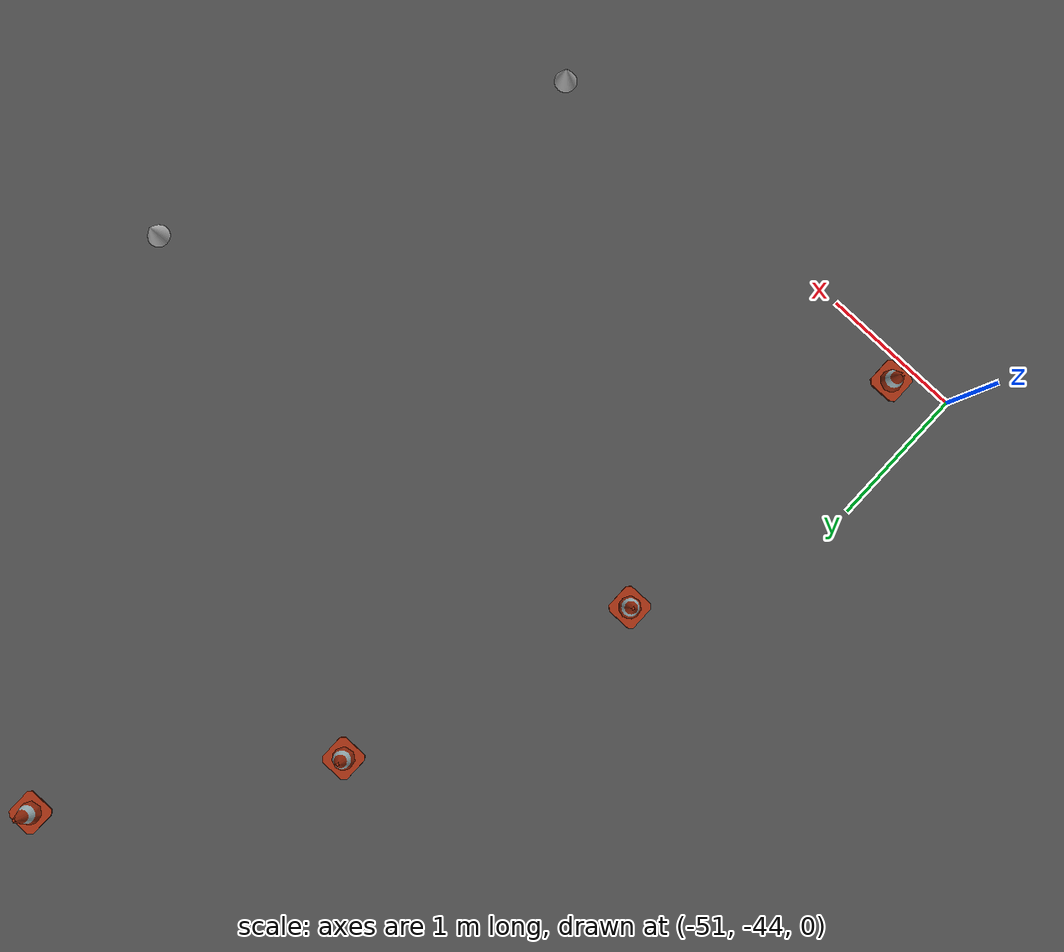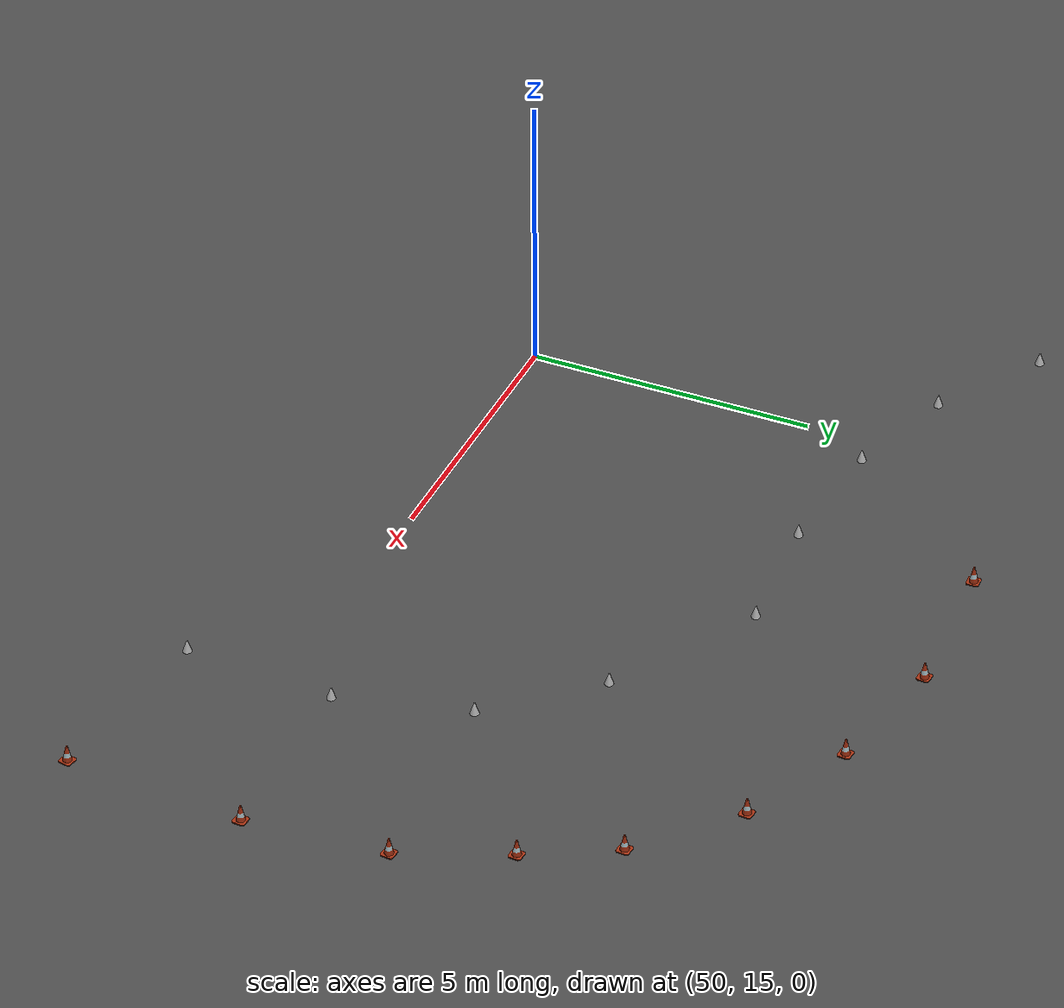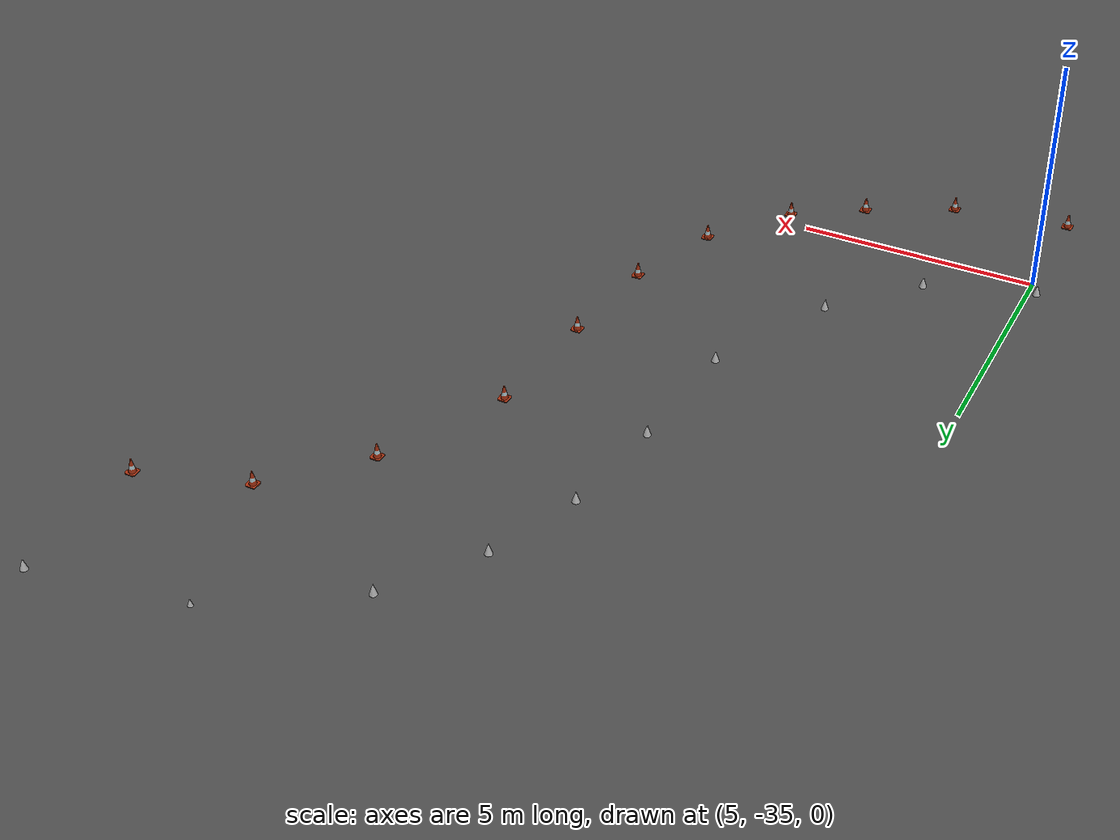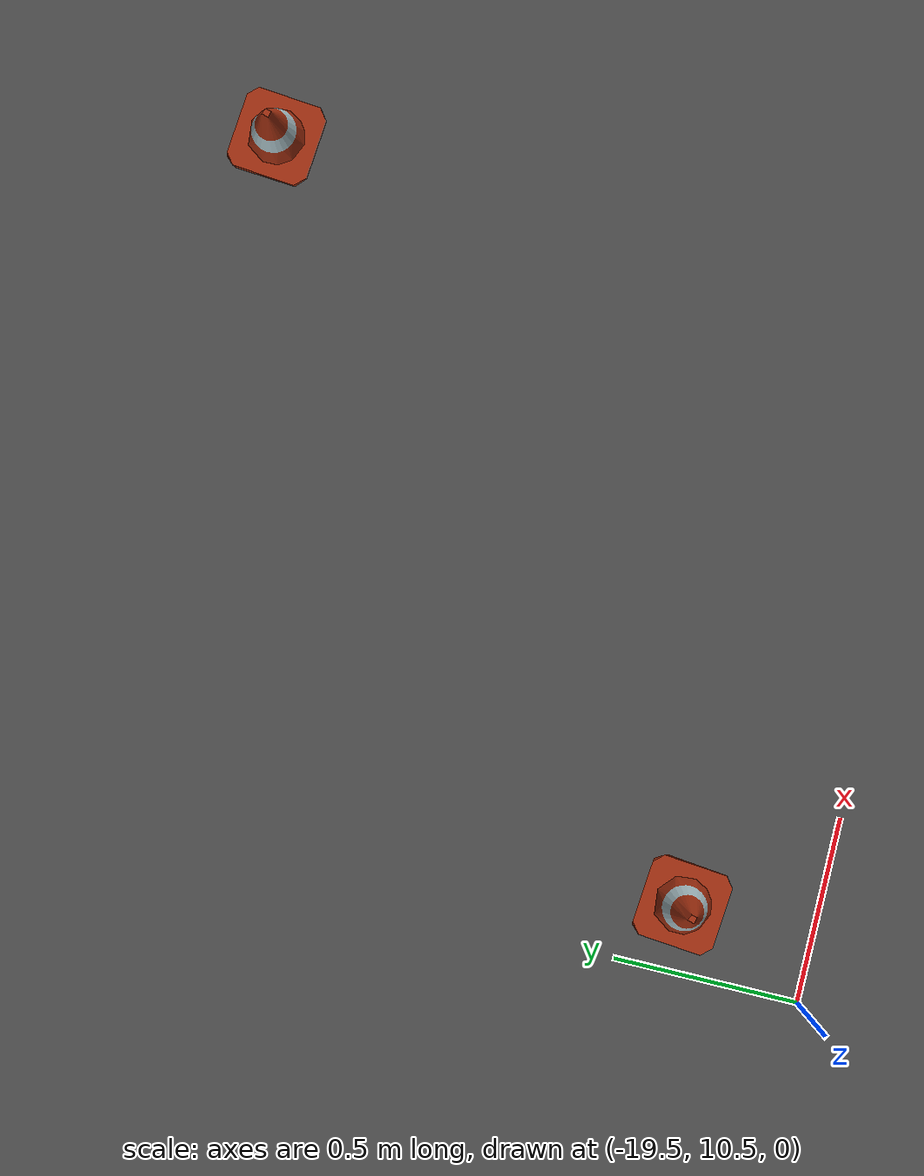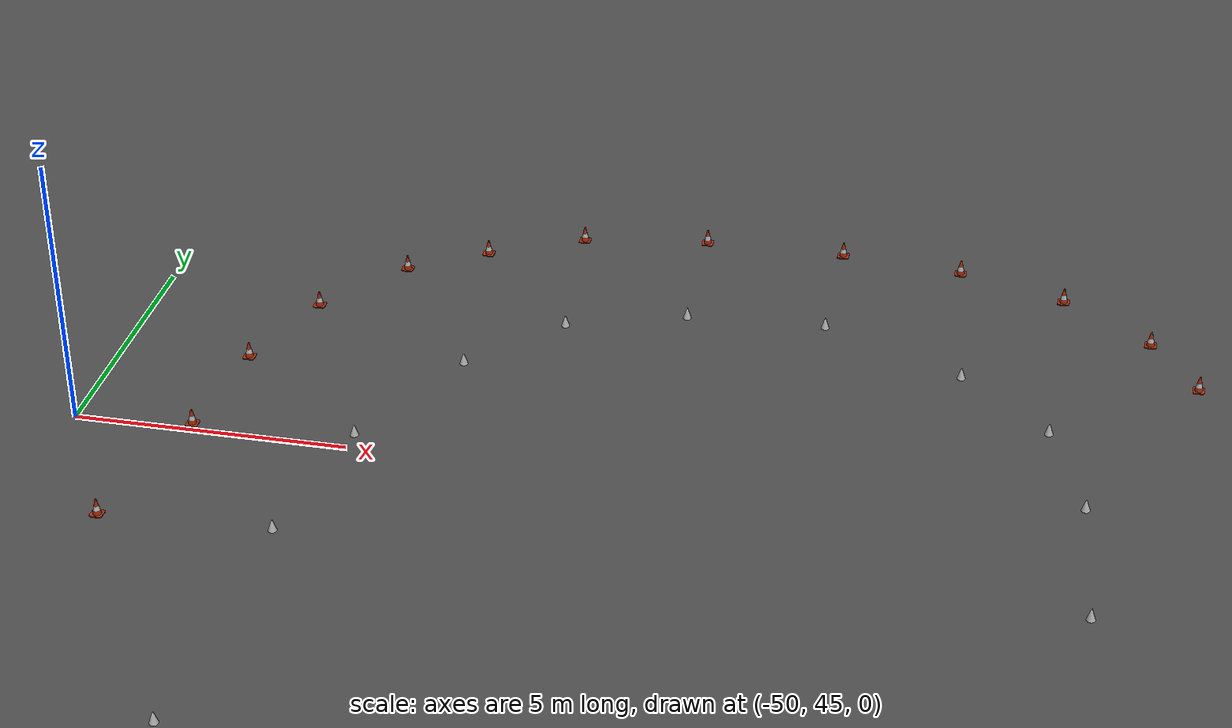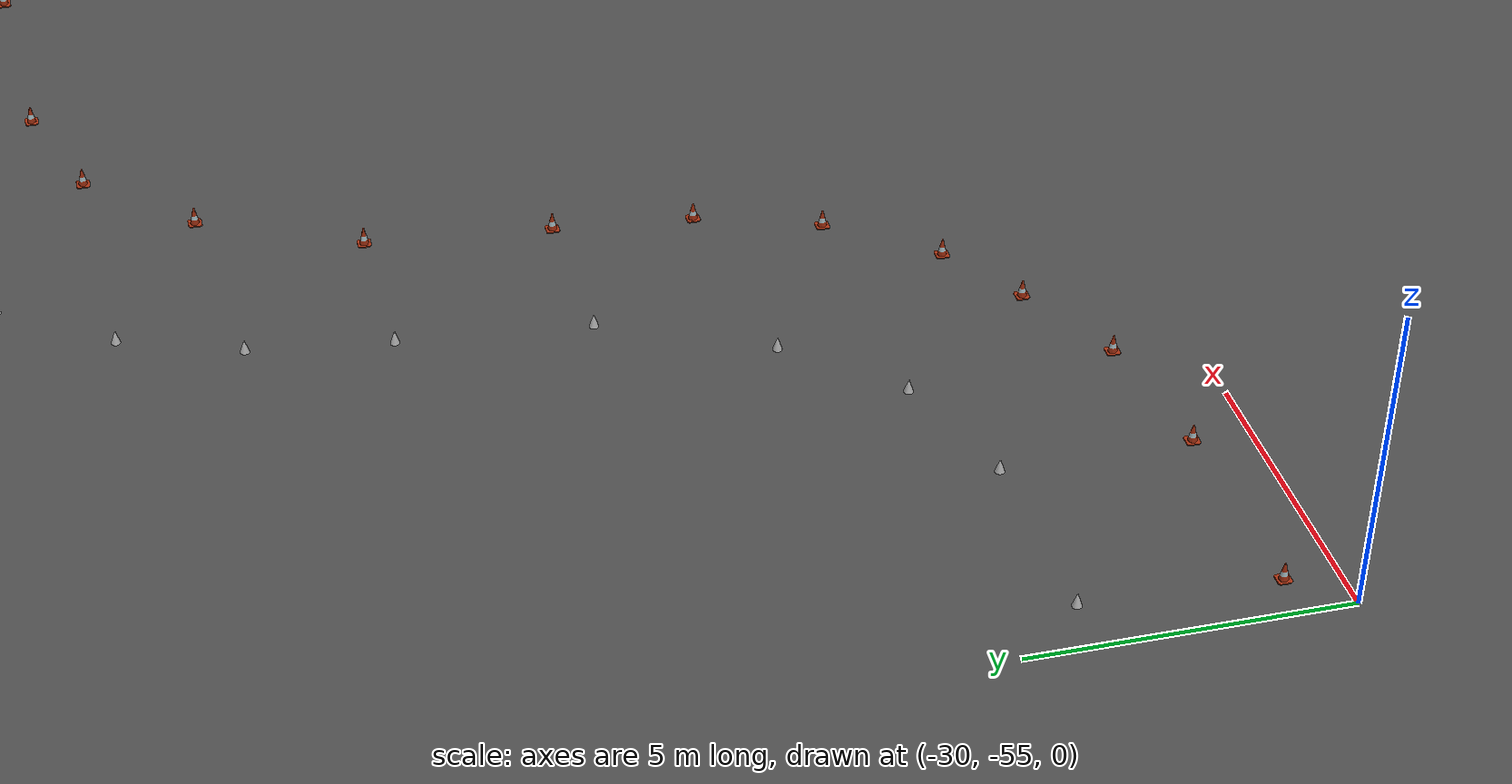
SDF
<sdf version="1.6">
 <world name="default">
  <scene>
   <sky><clouds><speed>3</speed></clouds></sky>
   <ambient>1.0 1.0 1.0 1.0</ambient>
   <shadows>true</shadows>
  </scene>
  <light name="sun" type="directional">
   <pose>0 0 10 0 -0 0</pose>
   <diffuse>0.8 0.8 0.8 1</diffuse>
   <specular>0.1 0.1 0.1 1</specular>
   <attenuation>
    <range>1000</range>
    <constant>0.9</constant>
    <linear>0.01</linear>
    <quadratic>0.001</quadratic>
   </attenuation>
   <direction>-0.5 0.5 -1</direction>
  </light>
  <model name="race_ground">
   <static>1</static>
   <link name="link">
    <collision name="collision">
     <geometry><plane><normal>0 0 1</normal><size>120 120</size></plane></geometry>
     <surface><friction><ode><mu>100</mu><mu2>50</mu2></ode></friction></surface>
    </collision>
    <visual name="visual">
     <cast_shadows>0</cast_shadows>
     <geometry><plane><normal>0 0 1</normal><size>120 120</size></plane></geometry>
     <material>
      <script><uri>model://race_ground/materials/gazebo.material</uri><name>Gazebo/Asphalt</name></script>
     </material>
    </visual>
   </link>
   <pose>5.48058 -4.5472 0 0 -0 0</pose>
  </model>
  <model name="straight_track">
   <model name="cone_blue">
    <link name="link">
     <collision name="collision">
      <geometry><mesh><uri>model://cone_blue/meshes/cone_blue.dae</uri></mesh></geometry>
     </collision>
     <visual name="visual">
      <geometry><mesh><uri>model://cone_blue/meshes/cone_blue.dae</uri></mesh></geometry>
     </visual>
     <inertial>
      <inertia><ixx>1</ixx><ixy>0</ixy><ixz>0</ixz><iyy>1</iyy><iyz>0</iyz><izz>1</izz></inertia>
      <mass>1</mass>
     </inertial>
    </link>
    <pose>5.00125 1.5533 0 0 -0 0</pose>
   </model>
   <model name="cone_blue_0">
    <link name="link">
     <collision name="collision">
      <geometry><mesh><uri>model://cone_blue/meshes/cone_blue.dae</uri></mesh></geometry>
     </collision>
     <visual name="visual">
      <geometry><mesh><uri>model://cone_blue/meshes/cone_blue.dae</uri></mesh></geometry>
     </visual>
     <inertial>
      <inertia><ixx>1</ixx><ixy>0</ixy><ixz>0</ixz><iyy>1</iyy><iyz>0</iyz><izz>1</izz></inertia>
      <mass>1</mass>
     </inertial>
    </link>
    <pose>0.001248 1.5533 0 0 -0 0</pose>
   </model>
   <model name="cone_blue_1">
    <link name="link">
     <collision name="collision">
      <geometry><mesh><uri>model://cone_blue/meshes/cone_blue.dae</uri></mesh></geometry>
     </collision>
     <visual name="visual">
      <geometry><mesh><uri>model://cone_blue/meshes/cone_blue.dae</uri></mesh></geometry>
     </visual>
     <inertial>
      <inertia><ixx>1</ixx><ixy>0</ixy><ixz>0</ixz><iyy>1</iyy><iyz>0</iyz><izz>1</izz></inertia>
      <mass>1</mass>
     </inertial>
    </link>
    <pose>-4.99875 1.5533 0 0 -0 0</pose>
   </model>
   <model name="cone_red">
    <link name="link">
     <collision name="collision">
      <geometry><mesh><uri>model://cone_red/meshes/cone_red.dae</uri></mesh></geometry>
     </collision>
     <visual name="visual">
      <geometry><mesh><uri>model://cone_red/meshes/cone_red.dae</uri></mesh></geometry>
     </visual>
     <inertial>
      <inertia><ixx>1</ixx><ixy>0</ixy><ixz>0</ixz><iyy>1</iyy><iyz>0</iyz><izz>1</izz></inertia>
      <mass>1</mass>
     </inertial>
    </link>
    <pose>5.00125 -1.57663 0 0 -0 0</pose>
   </model>
   <model name="cone_red_0">
    <link name="link">
     <collision name="collision">
      <geometry><mesh><uri>model://cone_red/meshes/cone_red.dae</uri></mesh></geometry>
     </collision>
     <visual name="visual">
      <geometry><mesh><uri>model://cone_red/meshes/cone_red.dae</uri></mesh></geometry>
     </visual>
     <inertial>
      <inertia><ixx>1</ixx><ixy>0</ixy><ixz>0</ixz><iyy>1</iyy><iyz>0</iyz><izz>1</izz></inertia>
      <mass>1</mass>
     </inertial>
    </link>
    <pose>-0.067192 -1.52376 0 0 -0 0</pose>
   </model>
   <model name="cone_red_1">
    <link name="link">
     <collision name="collision">
      <geometry><mesh><uri>model://cone_red/meshes/cone_red.dae</uri></mesh></geometry>
     </collision>
     <visual name="visual">
      <geometry><mesh><uri>model://cone_red/meshes/cone_red.dae</uri></mesh></geometry>
     </visual>
     <inertial>
      <inertia><ixx>1</ixx><ixy>0</ixy><ixz>0</ixz><iyy>1</iyy><iyz>0</iyz><izz>1</izz></inertia>
      <mass>1</mass>
     </inertial>
    </link>
    <pose>-4.9378 -1.55952 0 0 -0 0</pose>
   </model>
   <static>0</static>
   <pose>43.0327 -19.9795 0.151673 0 -0 0.000348</pose>
  </model>
  <model name="straight_track_clone">
   <model name="cone_blue">
    <link name="link">
     <collision name="collision">
      <geometry><mesh><uri>model://cone_blue/meshes/cone_blue.dae</uri></mesh></geometry>
     </collision>
     <visual name="visual">
      <geometry><mesh><uri>model://cone_blue/meshes/cone_blue.dae</uri></mesh></geometry>
     </visual>
     <inertial>
      <inertia><ixx>1</ixx><ixy>0</ixy><ixz>0</ixz><iyy>1</iyy><iyz>0</iyz><izz>1</izz></inertia>
      <mass>1</mass>
     </inertial>
    </link>
    <pose>5.00125 1.5533 0 0 -0 0</pose>
   </model>
   <model name="cone_blue_0">
    <link name="link">
     <collision name="collision">
      <geometry><mesh><uri>model://cone_blue/meshes/cone_blue.dae</uri></mesh></geometry>
     </collision>
     <visual name="visual">
      <geometry><mesh><uri>model://cone_blue/meshes/cone_blue.dae</uri></mesh></geometry>
     </visual>
     <inertial>
      <inertia><ixx>1</ixx><ixy>0</ixy><ixz>0</ixz><iyy>1</iyy><iyz>0</iyz><izz>1</izz></inertia>
      <mass>1</mass>
     </inertial>
    </link>
    <pose>0.001248 1.5533 0 0 -0 0</pose>
   </model>
   <model name="cone_blue_1">
    <link name="link">
     <collision name="collision">
      <geometry><mesh><uri>model://cone_blue/meshes/cone_blue.dae</uri></mesh></geometry>
     </collision>
     <visual name="visual">
      <geometry><mesh><uri>model://cone_blue/meshes/cone_blue.dae</uri></mesh></geometry>
     </visual>
     <inertial>
      <inertia><ixx>1</ixx><ixy>0</ixy><ixz>0</ixz><iyy>1</iyy><iyz>0</iyz><izz>1</izz></inertia>
      <mass>1</mass>
     </inertial>
    </link>
    <pose>-4.99875 1.5533 0 0 -0 0</pose>
   </model>
   <model name="cone_red">
    <link name="link">
     <collision name="collision">
      <geometry><mesh><uri>model://cone_red/meshes/cone_red.dae</uri></mesh></geometry>
     </collision>
     <visual name="visual">
      <geometry><mesh><uri>model://cone_red/meshes/cone_red.dae</uri></mesh></geometry>
     </visual>
     <inertial>
      <inertia><ixx>1</ixx><ixy>0</ixy><ixz>0</ixz><iyy>1</iyy><iyz>0</iyz><izz>1</izz></inertia>
      <mass>1</mass>
     </inertial>
    </link>
    <pose>5.00125 -1.57663 0 0 -0 0</pose>
   </model>
   <model name="cone_red_0">
    <link name="link">
     <collision name="collision">
      <geometry><mesh><uri>model://cone_red/meshes/cone_red.dae</uri></mesh></geometry>
     </collision>
     <visual name="visual">
      <geometry><mesh><uri>model://cone_red/meshes/cone_red.dae</uri></mesh></geometry>
     </visual>
     <inertial>
      <inertia><ixx>1</ixx><ixy>0</ixy><ixz>0</ixz><iyy>1</iyy><iyz>0</iyz><izz>1</izz></inertia>
      <mass>1</mass>
     </inertial>
    </link>
    <pose>-0.067192 -1.52376 0 0 -0 0</pose>
   </model>
   <model name="cone_red_1">
    <link name="link">
     <collision name="collision">
      <geometry><mesh><uri>model://cone_red/meshes/cone_red.dae</uri></mesh></geometry>
     </collision>
     <visual name="visual">
      <geometry><mesh><uri>model://cone_red/meshes/cone_red.dae</uri></mesh></geometry>
     </visual>
     <inertial>
      <inertia><ixx>1</ixx><ixy>0</ixy><ixz>0</ixz><iyy>1</iyy><iyz>0</iyz><izz>1</izz></inertia>
      <mass>1</mass>
     </inertial>
    </link>
    <pose>-4.9378 -1.55952 0 0 -0 0</pose>
   </model>
   <static>0</static>
   <pose>26.9435 -20.1133 0.151676 -1e-06 -0 0.000358</pose>
  </model>
  <model name="right_turn">
   <model name="cone_blue_10">
    <link name="link">
     <collision name="collision">
      <geometry><mesh><uri>model://cone_blue/meshes/cone_blue.dae</uri></mesh></geometry>
     </collision>
     <visual name="visual">
      <geometry><mesh><uri>model://cone_blue/meshes/cone_blue.dae</uri></mesh></geometry>
     </visual>
     <inertial>
      <inertia><ixx>1</ixx><ixy>0</ixy><ixz>0</ixz><iyy>1</iyy><iyz>0</iyz><izz>1</izz></inertia>
      <mass>1</mass>
     </inertial>
    </link>
    <pose>7.02182 -0.020955 -0.001706 0 -0 0</pose>
   </model>
   <model name="cone_blue_7">
    <link name="link">
     <collision name="collision">
      <geometry><mesh><uri>model://cone_blue/meshes/cone_blue.dae</uri></mesh></geometry>
     </collision>
     <visual name="visual">
      <geometry><mesh><uri>model://cone_blue/meshes/cone_blue.dae</uri></mesh></geometry>
     </visual>
     <inertial>
      <inertia><ixx>1</ixx><ixy>0</ixy><ixz>0</ixz><iyy>1</iyy><iyz>0</iyz><izz>1</izz></inertia>
      <mass>1</mass>
     </inertial>
    </link>
    <pose>2.01267 -5.02095 -0.001706 0 -0 0</pose>
   </model>
   <model name="cone_blue_8">
    <link name="link">
     <collision name="collision">
      <geometry><mesh><uri>model://cone_blue/meshes/cone_blue.dae</uri></mesh></geometry>
     </collision>
     <visual name="visual">
      <geometry><mesh><uri>model://cone_blue/meshes/cone_blue.dae</uri></mesh></geometry>
     </visual>
     <inertial>
      <inertia><ixx>1</ixx><ixy>0</ixy><ixz>0</ixz><iyy>1</iyy><iyz>0</iyz><izz>1</izz></inertia>
      <mass>1</mass>
     </inertial>
    </link>
    <pose>3.30371 -2.38642 -0.001706 0 -0 0</pose>
   </model>
   <model name="cone_blue_9">
    <link name="link">
     <collision name="collision">
      <geometry><mesh><uri>model://cone_blue/meshes/cone_blue.dae</uri></mesh></geometry>
     </collision>
     <visual name="visual">
      <geometry><mesh><uri>model://cone_blue/meshes/cone_blue.dae</uri></mesh></geometry>
     </visual>
     <inertial>
      <inertia><ixx>1</ixx><ixy>0</ixy><ixz>0</ixz><iyy>1</iyy><iyz>0</iyz><izz>1</izz></inertia>
      <mass>1</mass>
     </inertial>
    </link>
    <pose>4.83695 -0.737396 -0.001706 0 -0 0</pose>
   </model>
   <model name="cone_red">
    <link name="link">
     <collision name="collision">
      <geometry><mesh><uri>model://cone_red/meshes/cone_red.dae</uri></mesh></geometry>
     </collision>
     <visual name="visual">
      <geometry><mesh><uri>model://cone_red/meshes/cone_red.dae</uri></mesh></geometry>
     </visual>
     <inertial>
      <inertia><ixx>1</ixx><ixy>0</ixy><ixz>0</ixz><iyy>1</iyy><iyz>0</iyz><izz>1</izz></inertia>
      <mass>1</mass>
     </inertial>
    </link>
    <pose>6.86979 3.10588 -0.001706 0 -0 0</pose>
   </model>
   <model name="cone_red_0">
    <link name="link">
     <collision name="collision">
      <geometry><mesh><uri>model://cone_red/meshes/cone_red.dae</uri></mesh></geometry>
     </collision>
     <visual name="visual">
      <geometry><mesh><uri>model://cone_red/meshes/cone_red.dae</uri></mesh></geometry>
     </visual>
     <inertial>
      <inertia><ixx>1</ixx><ixy>0</ixy><ixz>0</ixz><iyy>1</iyy><iyz>0</iyz><izz>1</izz></inertia>
      <mass>1</mass>
     </inertial>
    </link>
    <pose>4.45799 2.73997 -0.001706 0 -0 0</pose>
   </model>
   <model name="cone_red_1">
    <link name="link">
     <collision name="collision">
      <geometry><mesh><uri>model://cone_red/meshes/cone_red.dae</uri></mesh></geometry>
     </collision>
     <visual name="visual">
      <geometry><mesh><uri>model://cone_red/meshes/cone_red.dae</uri></mesh></geometry>
     </visual>
     <inertial>
      <inertia><ixx>1</ixx><ixy>0</ixy><ixz>0</ixz><iyy>1</iyy><iyz>0</iyz><izz>1</izz></inertia>
      <mass>1</mass>
     </inertial>
    </link>
    <pose>2.70546 1.86013 -0.001706 0 -0 0</pose>
   </model>
   <model name="cone_red_2">
    <link name="link">
     <collision name="collision">
      <geometry><mesh><uri>model://cone_red/meshes/cone_red.dae</uri></mesh></geometry>
     </collision>
     <visual name="visual">
      <geometry><mesh><uri>model://cone_red/meshes/cone_red.dae</uri></mesh></geometry>
     </visual>
     <inertial>
      <inertia><ixx>1</ixx><ixy>0</ixy><ixz>0</ixz><iyy>1</iyy><iyz>0</iyz><izz>1</izz></inertia>
      <mass>1</mass>
     </inertial>
    </link>
    <pose>1.29777 0.979045 -0.001706 0 -0 0</pose>
   </model>
   <model name="cone_red_3">
    <link name="link">
     <collision name="collision">
      <geometry><mesh><uri>model://cone_red/meshes/cone_red.dae</uri></mesh></geometry>
     </collision>
     <visual name="visual">
      <geometry><mesh><uri>model://cone_red/meshes/cone_red.dae</uri></mesh></geometry>
     </visual>
     <inertial>
      <inertia><ixx>1</ixx><ixy>0</ixy><ixz>0</ixz><iyy>1</iyy><iyz>0</iyz><izz>1</izz></inertia>
      <mass>1</mass>
     </inertial>
    </link>
    <pose>0.020348 -0.677548 -0.001706 0 -0 0</pose>
   </model>
   <model name="cone_red_4">
    <link name="link">
     <collision name="collision">
      <geometry><mesh><uri>model://cone_red/meshes/cone_red.dae</uri></mesh></geometry>
     </collision>
     <visual name="visual">
      <geometry><mesh><uri>model://cone_red/meshes/cone_red.dae</uri></mesh></geometry>
     </visual>
     <inertial>
      <inertia><ixx>1</ixx><ixy>0</ixy><ixz>0</ixz><iyy>1</iyy><iyz>0</iyz><izz>1</izz></inertia>
      <mass>1</mass>
     </inertial>
    </link>
    <pose>-0.703674 -2.69605 -0.001706 0 -0 0</pose>
   </model>
   <model name="cone_red_5">
    <link name="link">
     <collision name="collision">
      <geometry><mesh><uri>model://cone_red/meshes/cone_red.dae</uri></mesh></geometry>
     </collision>
     <visual name="visual">
      <geometry><mesh><uri>model://cone_red/meshes/cone_red.dae</uri></mesh></geometry>
     </visual>
     <inertial>
      <inertia><ixx>1</ixx><ixy>0</ixy><ixz>0</ixz><iyy>1</iyy><iyz>0</iyz><izz>1</izz></inertia>
      <mass>1</mass>
     </inertial>
    </link>
    <pose>-0.979653 -5.02095 -0.001706 0 -0 0</pose>
   </model>
   <static>0</static>
   <pose>58.2566 -18.2909 0.153375 -1e-06 -1e-06 -3.13014</pose>
  </model>
  <model name="straight_track_0">
   <model name="cone_blue">
    <link name="link">
     <collision name="collision">
      <geometry><mesh><uri>model://cone_blue/meshes/cone_blue.dae</uri></mesh></geometry>
     </collision>
     <visual name="visual">
      <geometry><mesh><uri>model://cone_blue/meshes/cone_blue.dae</uri></mesh></geometry>
     </visual>
     <inertial>
      <inertia><ixx>1</ixx><ixy>0</ixy><ixz>0</ixz><iyy>1</iyy><iyz>0</iyz><izz>1</izz></inertia>
      <mass>1</mass>
     </inertial>
    </link>
    <pose>5.00125 1.5533 0 0 -0 0</pose>
   </model>
   <model name="cone_blue_0">
    <link name="link">
     <collision name="collision">
      <geometry><mesh><uri>model://cone_blue/meshes/cone_blue.dae</uri></mesh></geometry>
     </collision>
     <visual name="visual">
      <geometry><mesh><uri>model://cone_blue/meshes/cone_blue.dae</uri></mesh></geometry>
     </visual>
     <inertial>
      <inertia><ixx>1</ixx><ixy>0</ixy><ixz>0</ixz><iyy>1</iyy><iyz>0</iyz><izz>1</izz></inertia>
      <mass>1</mass>
     </inertial>
    </link>
    <pose>0.001248 1.5533 0 0 -0 0</pose>
   </model>
   <model name="cone_blue_1">
    <link name="link">
     <collision name="collision">
      <geometry><mesh><uri>model://cone_blue/meshes/cone_blue.dae</uri></mesh></geometry>
     </collision>
     <visual name="visual">
      <geometry><mesh><uri>model://cone_blue/meshes/cone_blue.dae</uri></mesh></geometry>
     </visual>
     <inertial>
      <inertia><ixx>1</ixx><ixy>0</ixy><ixz>0</ixz><iyy>1</iyy><iyz>0</iyz><izz>1</izz></inertia>
      <mass>1</mass>
     </inertial>
    </link>
    <pose>-4.99875 1.5533 0 0 -0 0</pose>
   </model>
   <model name="cone_red">
    <link name="link">
     <collision name="collision">
      <geometry><mesh><uri>model://cone_red/meshes/cone_red.dae</uri></mesh></geometry>
     </collision>
     <visual name="visual">
      <geometry><mesh><uri>model://cone_red/meshes/cone_red.dae</uri></mesh></geometry>
     </visual>
     <inertial>
      <inertia><ixx>1</ixx><ixy>0</ixy><ixz>0</ixz><iyy>1</iyy><iyz>0</iyz><izz>1</izz></inertia>
      <mass>1</mass>
     </inertial>
    </link>
    <pose>5.00125 -1.57663 0 0 -0 0</pose>
   </model>
   <model name="cone_red_0">
    <link name="link">
     <collision name="collision">
      <geometry><mesh><uri>model://cone_red/meshes/cone_red.dae</uri></mesh></geometry>
     </collision>
     <visual name="visual">
      <geometry><mesh><uri>model://cone_red/meshes/cone_red.dae</uri></mesh></geometry>
     </visual>
     <inertial>
      <inertia><ixx>1</ixx><ixy>0</ixy><ixz>0</ixz><iyy>1</iyy><iyz>0</iyz><izz>1</izz></inertia>
      <mass>1</mass>
     </inertial>
    </link>
    <pose>-0.067192 -1.52376 0 0 -0 0</pose>
   </model>
   <model name="cone_red_1">
    <link name="link">
     <collision name="collision">
      <geometry><mesh><uri>model://cone_red/meshes/cone_red.dae</uri></mesh></geometry>
     </collision>
     <visual name="visual">
      <geometry><mesh><uri>model://cone_red/meshes/cone_red.dae</uri></mesh></geometry>
     </visual>
     <inertial>
      <inertia><ixx>1</ixx><ixy>0</ixy><ixz>0</ixz><iyy>1</iyy><iyz>0</iyz><izz>1</izz></inertia>
      <mass>1</mass>
     </inertial>
    </link>
    <pose>-4.9378 -1.55952 0 0 -0 0</pose>
   </model>
   <static>0</static>
   <pose>58.5265 -4.8087 0.151667 1e-06 -1e-06 1.47661</pose>
  </model>
  <model name="left_turn">
   <model name="cone_blue">
    <link name="link">
     <collision name="collision">
      <geometry><mesh><uri>model://cone_blue/meshes/cone_blue.dae</uri></mesh></geometry>
     </collision>
     <visual name="visual">
      <geometry><mesh><uri>model://cone_blue/meshes/cone_blue.dae</uri></mesh></geometry>
     </visual>
     <inertial>
      <inertia><ixx>1</ixx><ixy>0</ixy><ixz>0</ixz><iyy>1</iyy><iyz>0</iyz><izz>1</izz></inertia>
      <mass>1</mass>
     </inertial>
    </link>
    <pose>4.01224 3.56439 0.020473 0 -0 0</pose>
   </model>
   <model name="cone_blue_0">
    <link name="link">
     <collision name="collision">
      <geometry><mesh><uri>model://cone_blue/meshes/cone_blue.dae</uri></mesh></geometry>
     </collision>
     <visual name="visual">
      <geometry><mesh><uri>model://cone_blue/meshes/cone_blue.dae</uri></mesh></geometry>
     </visual>
     <inertial>
      <inertia><ixx>1</ixx><ixy>0</ixy><ixz>0</ixz><iyy>1</iyy><iyz>0</iyz><izz>1</izz></inertia>
      <mass>1</mass>
     </inertial>
    </link>
    <pose>1.07158 2.90676 -0.225207 0 -0 0</pose>
   </model>
   <model name="cone_blue_3">
    <link name="link">
     <collision name="collision">
      <geometry><mesh><uri>model://cone_blue/meshes/cone_blue.dae</uri></mesh></geometry>
     </collision>
     <visual name="visual">
      <geometry><mesh><uri>model://cone_blue/meshes/cone_blue.dae</uri></mesh></geometry>
     </visual>
     <inertial>
      <inertia><ixx>1</ixx><ixy>0</ixy><ixz>0</ixz><iyy>1</iyy><iyz>0</iyz><izz>1</izz></inertia>
      <mass>1</mass>
     </inertial>
    </link>
    <pose>-1.63633 1.45358 0.020473 0 -0 0</pose>
   </model>
   <model name="cone_blue_4">
    <link name="link">
     <collision name="collision">
      <geometry><mesh><uri>model://cone_blue/meshes/cone_blue.dae</uri></mesh></geometry>
     </collision>
     <visual name="visual">
      <geometry><mesh><uri>model://cone_blue/meshes/cone_blue.dae</uri></mesh></geometry>
     </visual>
     <inertial>
      <inertia><ixx>1</ixx><ixy>0</ixy><ixz>0</ixz><iyy>1</iyy><iyz>0</iyz><izz>1</izz></inertia>
      <mass>1</mass>
     </inertial>
    </link>
    <pose>-2.87212 -0.307147 0.020473 0 -0 0</pose>
   </model>
   <model name="cone_blue_5">
    <link name="link">
     <collision name="collision">
      <geometry><mesh><uri>model://cone_blue/meshes/cone_blue.dae</uri></mesh></geometry>
     </collision>
     <visual name="visual">
      <geometry><mesh><uri>model://cone_blue/meshes/cone_blue.dae</uri></mesh></geometry>
     </visual>
     <inertial>
      <inertia><ixx>1</ixx><ixy>0</ixy><ixz>0</ixz><iyy>1</iyy><iyz>0</iyz><izz>1</izz></inertia>
      <mass>1</mass>
     </inertial>
    </link>
    <pose>-3.90319 -4.54641 0.020473 0 -0 0</pose>
   </model>
   <model name="cone_blue_6">
    <link name="link">
     <collision name="collision">
      <geometry><mesh><uri>model://cone_blue/meshes/cone_blue.dae</uri></mesh></geometry>
     </collision>
     <visual name="visual">
      <geometry><mesh><uri>model://cone_blue/meshes/cone_blue.dae</uri></mesh></geometry>
     </visual>
     <inertial>
      <inertia><ixx>1</ixx><ixy>0</ixy><ixz>0</ixz><iyy>1</iyy><iyz>0</iyz><izz>1</izz></inertia>
      <mass>1</mass>
     </inertial>
    </link>
    <pose>-3.58525 -2.23325 0.020473 0 -0 0</pose>
   </model>
   <model name="cone_red">
    <link name="link">
     <collision name="collision">
      <geometry><mesh><uri>model://cone_red/meshes/cone_red.dae</uri></mesh></geometry>
     </collision>
     <visual name="visual">
      <geometry><mesh><uri>model://cone_red/meshes/cone_red.dae</uri></mesh></geometry>
     </visual>
     <inertial>
      <inertia><ixx>1</ixx><ixy>0</ixy><ixz>0</ixz><iyy>1</iyy><iyz>0</iyz><izz>1</izz></inertia>
      <mass>1</mass>
     </inertial>
    </link>
    <pose>4.09681 0.453585 0.020473 0 -0 0</pose>
   </model>
   <model name="cone_red_0">
    <link name="link">
     <collision name="collision">
      <geometry><mesh><uri>model://cone_red/meshes/cone_red.dae</uri></mesh></geometry>
     </collision>
     <visual name="visual">
      <geometry><mesh><uri>model://cone_red/meshes/cone_red.dae</uri></mesh></geometry>
     </visual>
     <inertial>
      <inertia><ixx>1</ixx><ixy>0</ixy><ixz>0</ixz><iyy>1</iyy><iyz>0</iyz><izz>1</izz></inertia>
      <mass>1</mass>
     </inertial>
    </link>
    <pose>1.9348 -0.231588 0.020473 0 -0 0</pose>
   </model>
   <model name="cone_red_1">
    <link name="link">
     <collision name="collision">
      <geometry><mesh><uri>model://cone_red/meshes/cone_red.dae</uri></mesh></geometry>
     </collision>
     <visual name="visual">
      <geometry><mesh><uri>model://cone_red/meshes/cone_red.dae</uri></mesh></geometry>
     </visual>
     <inertial>
      <inertia><ixx>1</ixx><ixy>0</ixy><ixz>0</ixz><iyy>1</iyy><iyz>0</iyz><izz>1</izz></inertia>
      <mass>1</mass>
     </inertial>
    </link>
    <pose>-0.900464 -4.54641 0.020473 0 -0 0</pose>
   </model>
   <model name="cone_red_2">
    <link name="link">
     <collision name="collision">
      <geometry><mesh><uri>model://cone_red/meshes/cone_red.dae</uri></mesh></geometry>
     </collision>
     <visual name="visual">
      <geometry><mesh><uri>model://cone_red/meshes/cone_red.dae</uri></mesh></geometry>
     </visual>
     <inertial>
      <inertia><ixx>1</ixx><ixy>0</ixy><ixz>0</ixz><iyy>1</iyy><iyz>0</iyz><izz>1</izz></inertia>
      <mass>1</mass>
     </inertial>
    </link>
    <pose>0.33919 -1.92026 0.020473 0 -0 0</pose>
   </model>
   <static>0</static>
   <pose>13.8237 -22.094 0.131184 -1e-06 -2e-06 0.000788</pose>
  </model>
  <model name="right_turn_clone">
   <model name="cone_blue_10">
    <link name="link">
     <collision name="collision">
      <geometry><mesh><uri>model://cone_blue/meshes/cone_blue.dae</uri></mesh></geometry>
     </collision>
     <visual name="visual">
      <geometry><mesh><uri>model://cone_blue/meshes/cone_blue.dae</uri></mesh></geometry>
     </visual>
     <inertial>
      <inertia><ixx>1</ixx><ixy>0</ixy><ixz>0</ixz><iyy>1</iyy><iyz>0</iyz><izz>1</izz></inertia>
      <mass>1</mass>
     </inertial>
    </link>
    <pose>7.02182 -0.020955 -0.001706 0 -0 0</pose>
   </model>
   <model name="cone_blue_7">
    <link name="link">
     <collision name="collision">
      <geometry><mesh><uri>model://cone_blue/meshes/cone_blue.dae</uri></mesh></geometry>
     </collision>
     <visual name="visual">
      <geometry><mesh><uri>model://cone_blue/meshes/cone_blue.dae</uri></mesh></geometry>
     </visual>
     <inertial>
      <inertia><ixx>1</ixx><ixy>0</ixy><ixz>0</ixz><iyy>1</iyy><iyz>0</iyz><izz>1</izz></inertia>
      <mass>1</mass>
     </inertial>
    </link>
    <pose>2.01267 -5.02095 -0.001706 0 -0 0</pose>
   </model>
   <model name="cone_blue_8">
    <link name="link">
     <collision name="collision">
      <geometry><mesh><uri>model://cone_blue/meshes/cone_blue.dae</uri></mesh></geometry>
     </collision>
     <visual name="visual">
      <geometry><mesh><uri>model://cone_blue/meshes/cone_blue.dae</uri></mesh></geometry>
     </visual>
     <inertial>
      <inertia><ixx>1</ixx><ixy>0</ixy><ixz>0</ixz><iyy>1</iyy><iyz>0</iyz><izz>1</izz></inertia>
      <mass>1</mass>
     </inertial>
    </link>
    <pose>3.30371 -2.38642 -0.001706 0 -0 0</pose>
   </model>
   <model name="cone_blue_9">
    <link name="link">
     <collision name="collision">
      <geometry><mesh><uri>model://cone_blue/meshes/cone_blue.dae</uri></mesh></geometry>
     </collision>
     <visual name="visual">
      <geometry><mesh><uri>model://cone_blue/meshes/cone_blue.dae</uri></mesh></geometry>
     </visual>
     <inertial>
      <inertia><ixx>1</ixx><ixy>0</ixy><ixz>0</ixz><iyy>1</iyy><iyz>0</iyz><izz>1</izz></inertia>
      <mass>1</mass>
     </inertial>
    </link>
    <pose>4.83695 -0.737396 -0.001706 0 -0 0</pose>
   </model>
   <model name="cone_red">
    <link name="link">
     <collision name="collision">
      <geometry><mesh><uri>model://cone_red/meshes/cone_red.dae</uri></mesh></geometry>
     </collision>
     <visual name="visual">
      <geometry><mesh><uri>model://cone_red/meshes/cone_red.dae</uri></mesh></geometry>
     </visual>
     <inertial>
      <inertia><ixx>1</ixx><ixy>0</ixy><ixz>0</ixz><iyy>1</iyy><iyz>0</iyz><izz>1</izz></inertia>
      <mass>1</mass>
     </inertial>
    </link>
    <pose>6.86979 3.10588 -0.001706 0 -0 0</pose>
   </model>
   <model name="cone_red_0">
    <link name="link">
     <collision name="collision">
      <geometry><mesh><uri>model://cone_red/meshes/cone_red.dae</uri></mesh></geometry>
     </collision>
     <visual name="visual">
      <geometry><mesh><uri>model://cone_red/meshes/cone_red.dae</uri></mesh></geometry>
     </visual>
     <inertial>
      <inertia><ixx>1</ixx><ixy>0</ixy><ixz>0</ixz><iyy>1</iyy><iyz>0</iyz><izz>1</izz></inertia>
      <mass>1</mass>
     </inertial>
    </link>
    <pose>4.45799 2.73997 -0.001706 0 -0 0</pose>
   </model>
   <model name="cone_red_1">
    <link name="link">
     <collision name="collision">
      <geometry><mesh><uri>model://cone_red/meshes/cone_red.dae</uri></mesh></geometry>
     </collision>
     <visual name="visual">
      <geometry><mesh><uri>model://cone_red/meshes/cone_red.dae</uri></mesh></geometry>
     </visual>
     <inertial>
      <inertia><ixx>1</ixx><ixy>0</ixy><ixz>0</ixz><iyy>1</iyy><iyz>0</iyz><izz>1</izz></inertia>
      <mass>1</mass>
     </inertial>
    </link>
    <pose>2.70546 1.86013 -0.001706 0 -0 0</pose>
   </model>
   <model name="cone_red_2">
    <link name="link">
     <collision name="collision">
      <geometry><mesh><uri>model://cone_red/meshes/cone_red.dae</uri></mesh></geometry>
     </collision>
     <visual name="visual">
      <geometry><mesh><uri>model://cone_red/meshes/cone_red.dae</uri></mesh></geometry>
     </visual>
     <inertial>
      <inertia><ixx>1</ixx><ixy>0</ixy><ixz>0</ixz><iyy>1</iyy><iyz>0</iyz><izz>1</izz></inertia>
      <mass>1</mass>
     </inertial>
    </link>
    <pose>1.29777 0.979045 -0.001706 0 -0 0</pose>
   </model>
   <model name="cone_red_3">
    <link name="link">
     <collision name="collision">
      <geometry><mesh><uri>model://cone_red/meshes/cone_red.dae</uri></mesh></geometry>
     </collision>
     <visual name="visual">
      <geometry><mesh><uri>model://cone_red/meshes/cone_red.dae</uri></mesh></geometry>
     </visual>
     <inertial>
      <inertia><ixx>1</ixx><ixy>0</ixy><ixz>0</ixz><iyy>1</iyy><iyz>0</iyz><izz>1</izz></inertia>
      <mass>1</mass>
     </inertial>
    </link>
    <pose>0.020348 -0.677548 -0.001706 0 -0 0</pose>
   </model>
   <model name="cone_red_4">
    <link name="link">
     <collision name="collision">
      <geometry><mesh><uri>model://cone_red/meshes/cone_red.dae</uri></mesh></geometry>
     </collision>
     <visual name="visual">
      <geometry><mesh><uri>model://cone_red/meshes/cone_red.dae</uri></mesh></geometry>
     </visual>
     <inertial>
      <inertia><ixx>1</ixx><ixy>0</ixy><ixz>0</ixz><iyy>1</iyy><iyz>0</iyz><izz>1</izz></inertia>
      <mass>1</mass>
     </inertial>
    </link>
    <pose>-0.703674 -2.69605 -0.001706 0 -0 0</pose>
   </model>
   <model name="cone_red_5">
    <link name="link">
     <collision name="collision">
      <geometry><mesh><uri>model://cone_red/meshes/cone_red.dae</uri></mesh></geometry>
     </collision>
     <visual name="visual">
      <geometry><mesh><uri>model://cone_red/meshes/cone_red.dae</uri></mesh></geometry>
     </visual>
     <inertial>
      <inertia><ixx>1</ixx><ixy>0</ixy><ixz>0</ixz><iyy>1</iyy><iyz>0</iyz><izz>1</izz></inertia>
      <mass>1</mass>
     </inertial>
    </link>
    <pose>-0.979653 -5.02095 -0.001706 0 -0 0</pose>
   </model>
   <static>0</static>
   <pose>11.8008 -34.3785 0.153378 -1e-06 0 -3.13014</pose>
  </model>
  <model name="straight_track_clone_clone">
   <model name="cone_blue">
    <link name="link">
     <collision name="collision">
      <geometry><mesh><uri>model://cone_blue/meshes/cone_blue.dae</uri></mesh></geometry>
     </collision>
     <visual name="visual">
      <geometry><mesh><uri>model://cone_blue/meshes/cone_blue.dae</uri></mesh></geometry>
     </visual>
     <inertial>
      <inertia><ixx>1</ixx><ixy>0</ixy><ixz>0</ixz><iyy>1</iyy><iyz>0</iyz><izz>1</izz></inertia>
      <mass>1</mass>
     </inertial>
    </link>
    <pose>5.00125 1.5533 0 0 -0 0</pose>
   </model>
   <model name="cone_blue_0">
    <link name="link">
     <collision name="collision">
      <geometry><mesh><uri>model://cone_blue/meshes/cone_blue.dae</uri></mesh></geometry>
     </collision>
     <visual name="visual">
      <geometry><mesh><uri>model://cone_blue/meshes/cone_blue.dae</uri></mesh></geometry>
     </visual>
     <inertial>
      <inertia><ixx>1</ixx><ixy>0</ixy><ixz>0</ixz><iyy>1</iyy><iyz>0</iyz><izz>1</izz></inertia>
      <mass>1</mass>
     </inertial>
    </link>
    <pose>0.001248 1.5533 0 0 -0 0</pose>
   </model>
   <model name="cone_blue_1">
    <link name="link">
     <collision name="collision">
      <geometry><mesh><uri>model://cone_blue/meshes/cone_blue.dae</uri></mesh></geometry>
     </collision>
     <visual name="visual">
      <geometry><mesh><uri>model://cone_blue/meshes/cone_blue.dae</uri></mesh></geometry>
     </visual>
     <inertial>
      <inertia><ixx>1</ixx><ixy>0</ixy><ixz>0</ixz><iyy>1</iyy><iyz>0</iyz><izz>1</izz></inertia>
      <mass>1</mass>
     </inertial>
    </link>
    <pose>-4.99875 1.5533 0 0 -0 0</pose>
   </model>
   <model name="cone_red">
    <link name="link">
     <collision name="collision">
      <geometry><mesh><uri>model://cone_red/meshes/cone_red.dae</uri></mesh></geometry>
     </collision>
     <visual name="visual">
      <geometry><mesh><uri>model://cone_red/meshes/cone_red.dae</uri></mesh></geometry>
     </visual>
     <inertial>
      <inertia><ixx>1</ixx><ixy>0</ixy><ixz>0</ixz><iyy>1</iyy><iyz>0</iyz><izz>1</izz></inertia>
      <mass>1</mass>
     </inertial>
    </link>
    <pose>5.00125 -1.57663 0 0 -0 0</pose>
   </model>
   <model name="cone_red_0">
    <link name="link">
     <collision name="collision">
      <geometry><mesh><uri>model://cone_red/meshes/cone_red.dae</uri></mesh></geometry>
     </collision>
     <visual name="visual">
      <geometry><mesh><uri>model://cone_red/meshes/cone_red.dae</uri></mesh></geometry>
     </visual>
     <inertial>
      <inertia><ixx>1</ixx><ixy>0</ixy><ixz>0</ixz><iyy>1</iyy><iyz>0</iyz><izz>1</izz></inertia>
      <mass>1</mass>
     </inertial>
    </link>
    <pose>-0.067192 -1.52376 0 0 -0 0</pose>
   </model>
   <model name="cone_red_1">
    <link name="link">
     <collision name="collision">
      <geometry><mesh><uri>model://cone_red/meshes/cone_red.dae</uri></mesh></geometry>
     </collision>
     <visual name="visual">
      <geometry><mesh><uri>model://cone_red/meshes/cone_red.dae</uri></mesh></geometry>
     </visual>
     <inertial>
      <inertia><ixx>1</ixx><ixy>0</ixy><ixz>0</ixz><iyy>1</iyy><iyz>0</iyz><izz>1</izz></inertia>
      <mass>1</mass>
     </inertial>
    </link>
    <pose>-4.9378 -1.55952 0 0 -0 0</pose>
   </model>
   <static>0</static>
   <pose>-3.8496 -36.0284 0.151666 1e-06 -1e-06 0.000355</pose>
  </model>
  <model name="left_turn_clone">
   <model name="cone_blue">
    <link name="link">
     <collision name="collision">
      <geometry><mesh><uri>model://cone_blue/meshes/cone_blue.dae</uri></mesh></geometry>
     </collision>
     <visual name="visual">
      <geometry><mesh><uri>model://cone_blue/meshes/cone_blue.dae</uri></mesh></geometry>
     </visual>
     <inertial>
      <inertia><ixx>1</ixx><ixy>0</ixy><ixz>0</ixz><iyy>1</iyy><iyz>0</iyz><izz>1</izz></inertia>
      <mass>1</mass>
     </inertial>
    </link>
    <pose>4.01224 3.56439 0.020473 0 -0 0</pose>
   </model>
   <model name="cone_blue_0">
    <link name="link">
     <collision name="collision">
      <geometry><mesh><uri>model://cone_blue/meshes/cone_blue.dae</uri></mesh></geometry>
     </collision>
     <visual name="visual">
      <geometry><mesh><uri>model://cone_blue/meshes/cone_blue.dae</uri></mesh></geometry>
     </visual>
     <inertial>
      <inertia><ixx>1</ixx><ixy>0</ixy><ixz>0</ixz><iyy>1</iyy><iyz>0</iyz><izz>1</izz></inertia>
      <mass>1</mass>
     </inertial>
    </link>
    <pose>1.07158 2.90676 -0.225207 0 -0 0</pose>
   </model>
   <model name="cone_blue_3">
    <link name="link">
     <collision name="collision">
      <geometry><mesh><uri>model://cone_blue/meshes/cone_blue.dae</uri></mesh></geometry>
     </collision>
     <visual name="visual">
      <geometry><mesh><uri>model://cone_blue/meshes/cone_blue.dae</uri></mesh></geometry>
     </visual>
     <inertial>
      <inertia><ixx>1</ixx><ixy>0</ixy><ixz>0</ixz><iyy>1</iyy><iyz>0</iyz><izz>1</izz></inertia>
      <mass>1</mass>
     </inertial>
    </link>
    <pose>-1.63633 1.45358 0.020473 0 -0 0</pose>
   </model>
   <model name="cone_blue_4">
    <link name="link">
     <collision name="collision">
      <geometry><mesh><uri>model://cone_blue/meshes/cone_blue.dae</uri></mesh></geometry>
     </collision>
     <visual name="visual">
      <geometry><mesh><uri>model://cone_blue/meshes/cone_blue.dae</uri></mesh></geometry>
     </visual>
     <inertial>
      <inertia><ixx>1</ixx><ixy>0</ixy><ixz>0</ixz><iyy>1</iyy><iyz>0</iyz><izz>1</izz></inertia>
      <mass>1</mass>
     </inertial>
    </link>
    <pose>-2.87212 -0.307147 0.020473 0 -0 0</pose>
   </model>
   <model name="cone_blue_5">
    <link name="link">
     <collision name="collision">
      <geometry><mesh><uri>model://cone_blue/meshes/cone_blue.dae</uri></mesh></geometry>
     </collision>
     <visual name="visual">
      <geometry><mesh><uri>model://cone_blue/meshes/cone_blue.dae</uri></mesh></geometry>
     </visual>
     <inertial>
      <inertia><ixx>1</ixx><ixy>0</ixy><ixz>0</ixz><iyy>1</iyy><iyz>0</iyz><izz>1</izz></inertia>
      <mass>1</mass>
     </inertial>
    </link>
    <pose>-3.90319 -4.54641 0.020473 0 -0 0</pose>
   </model>
   <model name="cone_blue_6">
    <link name="link">
     <collision name="collision">
      <geometry><mesh><uri>model://cone_blue/meshes/cone_blue.dae</uri></mesh></geometry>
     </collision>
     <visual name="visual">
      <geometry><mesh><uri>model://cone_blue/meshes/cone_blue.dae</uri></mesh></geometry>
     </visual>
     <inertial>
      <inertia><ixx>1</ixx><ixy>0</ixy><ixz>0</ixz><iyy>1</iyy><iyz>0</iyz><izz>1</izz></inertia>
      <mass>1</mass>
     </inertial>
    </link>
    <pose>-3.58525 -2.23325 0.020473 0 -0 0</pose>
   </model>
   <model name="cone_red">
    <link name="link">
     <collision name="collision">
      <geometry><mesh><uri>model://cone_red/meshes/cone_red.dae</uri></mesh></geometry>
     </collision>
     <visual name="visual">
      <geometry><mesh><uri>model://cone_red/meshes/cone_red.dae</uri></mesh></geometry>
     </visual>
     <inertial>
      <inertia><ixx>1</ixx><ixy>0</ixy><ixz>0</ixz><iyy>1</iyy><iyz>0</iyz><izz>1</izz></inertia>
      <mass>1</mass>
     </inertial>
    </link>
    <pose>4.09681 0.453585 0.020473 0 -0 0</pose>
   </model>
   <model name="cone_red_0">
    <link name="link">
     <collision name="collision">
      <geometry><mesh><uri>model://cone_red/meshes/cone_red.dae</uri></mesh></geometry>
     </collision>
     <visual name="visual">
      <geometry><mesh><uri>model://cone_red/meshes/cone_red.dae</uri></mesh></geometry>
     </visual>
     <inertial>
      <inertia><ixx>1</ixx><ixy>0</ixy><ixz>0</ixz><iyy>1</iyy><iyz>0</iyz><izz>1</izz></inertia>
      <mass>1</mass>
     </inertial>
    </link>
    <pose>1.9348 -0.231588 0.020473 0 -0 0</pose>
   </model>
   <model name="cone_red_1">
    <link name="link">
     <collision name="collision">
      <geometry><mesh><uri>model://cone_red/meshes/cone_red.dae</uri></mesh></geometry>
     </collision>
     <visual name="visual">
      <geometry><mesh><uri>model://cone_red/meshes/cone_red.dae</uri></mesh></geometry>
     </visual>
     <inertial>
      <inertia><ixx>1</ixx><ixy>0</ixy><ixz>0</ixz><iyy>1</iyy><iyz>0</iyz><izz>1</izz></inertia>
      <mass>1</mass>
     </inertial>
    </link>
    <pose>-0.900464 -4.54641 0.020473 0 -0 0</pose>
   </model>
   <model name="cone_red_2">
    <link name="link">
     <collision name="collision">
      <geometry><mesh><uri>model://cone_red/meshes/cone_red.dae</uri></mesh></geometry>
     </collision>
     <visual name="visual">
      <geometry><mesh><uri>model://cone_red/meshes/cone_red.dae</uri></mesh></geometry>
     </visual>
     <inertial>
      <inertia><ixx>1</ixx><ixy>0</ixy><ixz>0</ixz><iyy>1</iyy><iyz>0</iyz><izz>1</izz></inertia>
      <mass>1</mass>
     </inertial>
    </link>
    <pose>0.33919 -1.92026 0.020473 0 -0 0</pose>
   </model>
   <static>0</static>
   <pose>-17.0131 -38.2117 0.131202 -2e-06 1e-06 0.000637</pose>
  </model>
  <model name="right_turn_clone_clone">
   <model name="cone_blue_10">
    <link name="link">
     <collision name="collision">
      <geometry><mesh><uri>model://cone_blue/meshes/cone_blue.dae</uri></mesh></geometry>
     </collision>
     <visual name="visual">
      <geometry><mesh><uri>model://cone_blue/meshes/cone_blue.dae</uri></mesh></geometry>
     </visual>
     <inertial>
      <inertia><ixx>1</ixx><ixy>0</ixy><ixz>0</ixz><iyy>1</iyy><iyz>0</iyz><izz>1</izz></inertia>
      <mass>1</mass>
     </inertial>
    </link>
    <pose>7.02182 -0.020955 -0.001706 0 -0 0</pose>
   </model>
   <model name="cone_blue_7">
    <link name="link">
     <collision name="collision">
      <geometry><mesh><uri>model://cone_blue/meshes/cone_blue.dae</uri></mesh></geometry>
     </collision>
     <visual name="visual">
      <geometry><mesh><uri>model://cone_blue/meshes/cone_blue.dae</uri></mesh></geometry>
     </visual>
     <inertial>
      <inertia><ixx>1</ixx><ixy>0</ixy><ixz>0</ixz><iyy>1</iyy><iyz>0</iyz><izz>1</izz></inertia>
      <mass>1</mass>
     </inertial>
    </link>
    <pose>2.01267 -5.02095 -0.001706 0 -0 0</pose>
   </model>
   <model name="cone_blue_8">
    <link name="link">
     <collision name="collision">
      <geometry><mesh><uri>model://cone_blue/meshes/cone_blue.dae</uri></mesh></geometry>
     </collision>
     <visual name="visual">
      <geometry><mesh><uri>model://cone_blue/meshes/cone_blue.dae</uri></mesh></geometry>
     </visual>
     <inertial>
      <inertia><ixx>1</ixx><ixy>0</ixy><ixz>0</ixz><iyy>1</iyy><iyz>0</iyz><izz>1</izz></inertia>
      <mass>1</mass>
     </inertial>
    </link>
    <pose>3.30371 -2.38642 -0.001706 0 -0 0</pose>
   </model>
   <model name="cone_blue_9">
    <link name="link">
     <collision name="collision">
      <geometry><mesh><uri>model://cone_blue/meshes/cone_blue.dae</uri></mesh></geometry>
     </collision>
     <visual name="visual">
      <geometry><mesh><uri>model://cone_blue/meshes/cone_blue.dae</uri></mesh></geometry>
     </visual>
     <inertial>
      <inertia><ixx>1</ixx><ixy>0</ixy><ixz>0</ixz><iyy>1</iyy><iyz>0</iyz><izz>1</izz></inertia>
      <mass>1</mass>
     </inertial>
    </link>
    <pose>4.83695 -0.737396 -0.001706 0 -0 0</pose>
   </model>
   <model name="cone_red">
    <link name="link">
     <collision name="collision">
      <geometry><mesh><uri>model://cone_red/meshes/cone_red.dae</uri></mesh></geometry>
     </collision>
     <visual name="visual">
      <geometry><mesh><uri>model://cone_red/meshes/cone_red.dae</uri></mesh></geometry>
     </visual>
     <inertial>
      <inertia><ixx>1</ixx><ixy>0</ixy><ixz>0</ixz><iyy>1</iyy><iyz>0</iyz><izz>1</izz></inertia>
      <mass>1</mass>
     </inertial>
    </link>
    <pose>6.86979 3.10588 -0.001706 0 -0 0</pose>
   </model>
   <model name="cone_red_0">
    <link name="link">
     <collision name="collision">
      <geometry><mesh><uri>model://cone_red/meshes/cone_red.dae</uri></mesh></geometry>
     </collision>
     <visual name="visual">
      <geometry><mesh><uri>model://cone_red/meshes/cone_red.dae</uri></mesh></geometry>
     </visual>
     <inertial>
      <inertia><ixx>1</ixx><ixy>0</ixy><ixz>0</ixz><iyy>1</iyy><iyz>0</iyz><izz>1</izz></inertia>
      <mass>1</mass>
     </inertial>
    </link>
    <pose>4.45799 2.73997 -0.001706 0 -0 0</pose>
   </model>
   <model name="cone_red_1">
    <link name="link">
     <collision name="collision">
      <geometry><mesh><uri>model://cone_red/meshes/cone_red.dae</uri></mesh></geometry>
     </collision>
     <visual name="visual">
      <geometry><mesh><uri>model://cone_red/meshes/cone_red.dae</uri></mesh></geometry>
     </visual>
     <inertial>
      <inertia><ixx>1</ixx><ixy>0</ixy><ixz>0</ixz><iyy>1</iyy><iyz>0</iyz><izz>1</izz></inertia>
      <mass>1</mass>
     </inertial>
    </link>
    <pose>2.70546 1.86013 -0.001706 0 -0 0</pose>
   </model>
   <model name="cone_red_2">
    <link name="link">
     <collision name="collision">
      <geometry><mesh><uri>model://cone_red/meshes/cone_red.dae</uri></mesh></geometry>
     </collision>
     <visual name="visual">
      <geometry><mesh><uri>model://cone_red/meshes/cone_red.dae</uri></mesh></geometry>
     </visual>
     <inertial>
      <inertia><ixx>1</ixx><ixy>0</ixy><ixz>0</ixz><iyy>1</iyy><iyz>0</iyz><izz>1</izz></inertia>
      <mass>1</mass>
     </inertial>
    </link>
    <pose>1.29777 0.979045 -0.001706 0 -0 0</pose>
   </model>
   <model name="cone_red_3">
    <link name="link">
     <collision name="collision">
      <geometry><mesh><uri>model://cone_red/meshes/cone_red.dae</uri></mesh></geometry>
     </collision>
     <visual name="visual">
      <geometry><mesh><uri>model://cone_red/meshes/cone_red.dae</uri></mesh></geometry>
     </visual>
     <inertial>
      <inertia><ixx>1</ixx><ixy>0</ixy><ixz>0</ixz><iyy>1</iyy><iyz>0</iyz><izz>1</izz></inertia>
      <mass>1</mass>
     </inertial>
    </link>
    <pose>0.020348 -0.677548 -0.001706 0 -0 0</pose>
   </model>
   <model name="cone_red_4">
    <link name="link">
     <collision name="collision">
      <geometry><mesh><uri>model://cone_red/meshes/cone_red.dae</uri></mesh></geometry>
     </collision>
     <visual name="visual">
      <geometry><mesh><uri>model://cone_red/meshes/cone_red.dae</uri></mesh></geometry>
     </visual>
     <inertial>
      <inertia><ixx>1</ixx><ixy>0</ixy><ixz>0</ixz><iyy>1</iyy><iyz>0</iyz><izz>1</izz></inertia>
      <mass>1</mass>
     </inertial>
    </link>
    <pose>-0.703674 -2.69605 -0.001706 0 -0 0</pose>
   </model>
   <model name="cone_red_5">
    <link name="link">
     <collision name="collision">
      <geometry><mesh><uri>model://cone_red/meshes/cone_red.dae</uri></mesh></geometry>
     </collision>
     <visual name="visual">
      <geometry><mesh><uri>model://cone_red/meshes/cone_red.dae</uri></mesh></geometry>
     </visual>
     <inertial>
      <inertia><ixx>1</ixx><ixy>0</ixy><ixz>0</ixz><iyy>1</iyy><iyz>0</iyz><izz>1</izz></inertia>
      <mass>1</mass>
     </inertial>
    </link>
    <pose>-0.979653 -5.02095 -0.001706 0 -0 0</pose>
   </model>
   <static>0</static>
   <pose>-19.1454 -50.8757 0.153358 0 -3e-06 -3.13014</pose>
  </model>
  <model name="straight_track_clone_clone_0">
   <model name="cone_blue">
    <link name="link">
     <collision name="collision">
      <geometry><mesh><uri>model://cone_blue/meshes/cone_blue.dae</uri></mesh></geometry>
     </collision>
     <visual name="visual">
      <geometry><mesh><uri>model://cone_blue/meshes/cone_blue.dae</uri></mesh></geometry>
     </visual>
     <inertial>
      <inertia><ixx>1</ixx><ixy>0</ixy><ixz>0</ixz><iyy>1</iyy><iyz>0</iyz><izz>1</izz></inertia>
      <mass>1</mass>
     </inertial>
    </link>
    <pose>5.00125 1.5533 0 0 -0 0</pose>
   </model>
   <model name="cone_blue_0">
    <link name="link">
     <collision name="collision">
      <geometry><mesh><uri>model://cone_blue/meshes/cone_blue.dae</uri></mesh></geometry>
     </collision>
     <visual name="visual">
      <geometry><mesh><uri>model://cone_blue/meshes/cone_blue.dae</uri></mesh></geometry>
     </visual>
     <inertial>
      <inertia><ixx>1</ixx><ixy>0</ixy><ixz>0</ixz><iyy>1</iyy><iyz>0</iyz><izz>1</izz></inertia>
      <mass>1</mass>
     </inertial>
    </link>
    <pose>0.001248 1.5533 0 0 -0 0</pose>
   </model>
   <model name="cone_blue_1">
    <link name="link">
     <collision name="collision">
      <geometry><mesh><uri>model://cone_blue/meshes/cone_blue.dae</uri></mesh></geometry>
     </collision>
     <visual name="visual">
      <geometry><mesh><uri>model://cone_blue/meshes/cone_blue.dae</uri></mesh></geometry>
     </visual>
     <inertial>
      <inertia><ixx>1</ixx><ixy>0</ixy><ixz>0</ixz><iyy>1</iyy><iyz>0</iyz><izz>1</izz></inertia>
      <mass>1</mass>
     </inertial>
    </link>
    <pose>-4.99875 1.5533 0 0 -0 0</pose>
   </model>
   <model name="cone_red">
    <link name="link">
     <collision name="collision">
      <geometry><mesh><uri>model://cone_red/meshes/cone_red.dae</uri></mesh></geometry>
     </collision>
     <visual name="visual">
      <geometry><mesh><uri>model://cone_red/meshes/cone_red.dae</uri></mesh></geometry>
     </visual>
     <inertial>
      <inertia><ixx>1</ixx><ixy>0</ixy><ixz>0</ixz><iyy>1</iyy><iyz>0</iyz><izz>1</izz></inertia>
      <mass>1</mass>
     </inertial>
    </link>
    <pose>5.00125 -1.57663 0 0 -0 0</pose>
   </model>
   <model name="cone_red_0">
    <link name="link">
     <collision name="collision">
      <geometry><mesh><uri>model://cone_red/meshes/cone_red.dae</uri></mesh></geometry>
     </collision>
     <visual name="visual">
      <geometry><mesh><uri>model://cone_red/meshes/cone_red.dae</uri></mesh></geometry>
     </visual>
     <inertial>
      <inertia><ixx>1</ixx><ixy>0</ixy><ixz>0</ixz><iyy>1</iyy><iyz>0</iyz><izz>1</izz></inertia>
      <mass>1</mass>
     </inertial>
    </link>
    <pose>-0.067192 -1.52376 0 0 -0 0</pose>
   </model>
   <model name="cone_red_1">
    <link name="link">
     <collision name="collision">
      <geometry><mesh><uri>model://cone_red/meshes/cone_red.dae</uri></mesh></geometry>
     </collision>
     <visual name="visual">
      <geometry><mesh><uri>model://cone_red/meshes/cone_red.dae</uri></mesh></geometry>
     </visual>
     <inertial>
      <inertia><ixx>1</ixx><ixy>0</ixy><ixz>0</ixz><iyy>1</iyy><iyz>0</iyz><izz>1</izz></inertia>
      <mass>1</mass>
     </inertial>
    </link>
    <pose>-4.9378 -1.55952 0 0 -0 0</pose>
   </model>
   <static>0</static>
   <pose>-34.2827 -52.5914 0.151659 2e-06 -2e-06 0.00036</pose>
  </model>
  <model name="right_turn_clone_clone_0">
   <model name="cone_blue_10">
    <link name="link">
     <collision name="collision">
      <geometry><mesh><uri>model://cone_blue/meshes/cone_blue.dae</uri></mesh></geometry>
     </collision>
     <visual name="visual">
      <geometry><mesh><uri>model://cone_blue/meshes/cone_blue.dae</uri></mesh></geometry>
     </visual>
     <inertial>
      <inertia><ixx>1</ixx><ixy>0</ixy><ixz>0</ixz><iyy>1</iyy><iyz>0</iyz><izz>1</izz></inertia>
      <mass>1</mass>
     </inertial>
    </link>
    <pose>7.02182 -0.020955 -0.001706 0 -0 0</pose>
   </model>
   <model name="cone_blue_7">
    <link name="link">
     <collision name="collision">
      <geometry><mesh><uri>model://cone_blue/meshes/cone_blue.dae</uri></mesh></geometry>
     </collision>
     <visual name="visual">
      <geometry><mesh><uri>model://cone_blue/meshes/cone_blue.dae</uri></mesh></geometry>
     </visual>
     <inertial>
      <inertia><ixx>1</ixx><ixy>0</ixy><ixz>0</ixz><iyy>1</iyy><iyz>0</iyz><izz>1</izz></inertia>
      <mass>1</mass>
     </inertial>
    </link>
    <pose>2.01267 -5.02095 -0.001706 0 -0 0</pose>
   </model>
   <model name="cone_blue_8">
    <link name="link">
     <collision name="collision">
      <geometry><mesh><uri>model://cone_blue/meshes/cone_blue.dae</uri></mesh></geometry>
     </collision>
     <visual name="visual">
      <geometry><mesh><uri>model://cone_blue/meshes/cone_blue.dae</uri></mesh></geometry>
     </visual>
     <inertial>
      <inertia><ixx>1</ixx><ixy>0</ixy><ixz>0</ixz><iyy>1</iyy><iyz>0</iyz><izz>1</izz></inertia>
      <mass>1</mass>
     </inertial>
    </link>
    <pose>3.30371 -2.38642 -0.001706 0 -0 0</pose>
   </model>
   <model name="cone_blue_9">
    <link name="link">
     <collision name="collision">
      <geometry><mesh><uri>model://cone_blue/meshes/cone_blue.dae</uri></mesh></geometry>
     </collision>
     <visual name="visual">
      <geometry><mesh><uri>model://cone_blue/meshes/cone_blue.dae</uri></mesh></geometry>
     </visual>
     <inertial>
      <inertia><ixx>1</ixx><ixy>0</ixy><ixz>0</ixz><iyy>1</iyy><iyz>0</iyz><izz>1</izz></inertia>
      <mass>1</mass>
     </inertial>
    </link>
    <pose>4.83695 -0.737396 -0.001706 0 -0 0</pose>
   </model>
   <model name="cone_red">
    <link name="link">
     <collision name="collision">
      <geometry><mesh><uri>model://cone_red/meshes/cone_red.dae</uri></mesh></geometry>
     </collision>
     <visual name="visual">
      <geometry><mesh><uri>model://cone_red/meshes/cone_red.dae</uri></mesh></geometry>
     </visual>
     <inertial>
      <inertia><ixx>1</ixx><ixy>0</ixy><ixz>0</ixz><iyy>1</iyy><iyz>0</iyz><izz>1</izz></inertia>
      <mass>1</mass>
     </inertial>
    </link>
    <pose>6.86979 3.10588 -0.001706 0 -0 0</pose>
   </model>
   <model name="cone_red_0">
    <link name="link">
     <collision name="collision">
      <geometry><mesh><uri>model://cone_red/meshes/cone_red.dae</uri></mesh></geometry>
     </collision>
     <visual name="visual">
      <geometry><mesh><uri>model://cone_red/meshes/cone_red.dae</uri></mesh></geometry>
     </visual>
     <inertial>
      <inertia><ixx>1</ixx><ixy>0</ixy><ixz>0</ixz><iyy>1</iyy><iyz>0</iyz><izz>1</izz></inertia>
      <mass>1</mass>
     </inertial>
    </link>
    <pose>4.45799 2.73997 -0.001706 0 -0 0</pose>
   </model>
   <model name="cone_red_1">
    <link name="link">
     <collision name="collision">
      <geometry><mesh><uri>model://cone_red/meshes/cone_red.dae</uri></mesh></geometry>
     </collision>
     <visual name="visual">
      <geometry><mesh><uri>model://cone_red/meshes/cone_red.dae</uri></mesh></geometry>
     </visual>
     <inertial>
      <inertia><ixx>1</ixx><ixy>0</ixy><ixz>0</ixz><iyy>1</iyy><iyz>0</iyz><izz>1</izz></inertia>
      <mass>1</mass>
     </inertial>
    </link>
    <pose>2.70546 1.86013 -0.001706 0 -0 0</pose>
   </model>
   <model name="cone_red_2">
    <link name="link">
     <collision name="collision">
      <geometry><mesh><uri>model://cone_red/meshes/cone_red.dae</uri></mesh></geometry>
     </collision>
     <visual name="visual">
      <geometry><mesh><uri>model://cone_red/meshes/cone_red.dae</uri></mesh></geometry>
     </visual>
     <inertial>
      <inertia><ixx>1</ixx><ixy>0</ixy><ixz>0</ixz><iyy>1</iyy><iyz>0</iyz><izz>1</izz></inertia>
      <mass>1</mass>
     </inertial>
    </link>
    <pose>1.29777 0.979045 -0.001706 0 -0 0</pose>
   </model>
   <model name="cone_red_3">
    <link name="link">
     <collision name="collision">
      <geometry><mesh><uri>model://cone_red/meshes/cone_red.dae</uri></mesh></geometry>
     </collision>
     <visual name="visual">
      <geometry><mesh><uri>model://cone_red/meshes/cone_red.dae</uri></mesh></geometry>
     </visual>
     <inertial>
      <inertia><ixx>1</ixx><ixy>0</ixy><ixz>0</ixz><iyy>1</iyy><iyz>0</iyz><izz>1</izz></inertia>
      <mass>1</mass>
     </inertial>
    </link>
    <pose>0.020348 -0.677548 -0.001706 0 -0 0</pose>
   </model>
   <model name="cone_red_4">
    <link name="link">
     <collision name="collision">
      <geometry><mesh><uri>model://cone_red/meshes/cone_red.dae</uri></mesh></geometry>
     </collision>
     <visual name="visual">
      <geometry><mesh><uri>model://cone_red/meshes/cone_red.dae</uri></mesh></geometry>
     </visual>
     <inertial>
      <inertia><ixx>1</ixx><ixy>0</ixy><ixz>0</ixz><iyy>1</iyy><iyz>0</iyz><izz>1</izz></inertia>
      <mass>1</mass>
     </inertial>
    </link>
    <pose>-0.703674 -2.69605 -0.001706 0 -0 0</pose>
   </model>
   <model name="cone_red_5">
    <link name="link">
     <collision name="collision">
      <geometry><mesh><uri>model://cone_red/meshes/cone_red.dae</uri></mesh></geometry>
     </collision>
     <visual name="visual">
      <geometry><mesh><uri>model://cone_red/meshes/cone_red.dae</uri></mesh></geometry>
     </visual>
     <inertial>
      <inertia><ixx>1</ixx><ixy>0</ixy><ixz>0</ixz><iyy>1</iyy><iyz>0</iyz><izz>1</izz></inertia>
      <mass>1</mass>
     </inertial>
    </link>
    <pose>-0.979653 -5.02095 -0.001706 0 -0 0</pose>
   </model>
   <static>0</static>
   <pose>-47.3042 -53.2295 0.153387 -3e-06 1e-06 1.59365</pose>
  </model>
  <model name="right_turn_clone_clone_1">
   <model name="cone_blue_10">
    <link name="link">
     <collision name="collision">
      <geometry><mesh><uri>model://cone_blue/meshes/cone_blue.dae</uri></mesh></geometry>
     </collision>
     <visual name="visual">
      <geometry><mesh><uri>model://cone_blue/meshes/cone_blue.dae</uri></mesh></geometry>
     </visual>
     <inertial>
      <inertia><ixx>1</ixx><ixy>0</ixy><ixz>0</ixz><iyy>1</iyy><iyz>0</iyz><izz>1</izz></inertia>
      <mass>1</mass>
     </inertial>
    </link>
    <pose>7.02182 -0.020955 -0.001706 0 -0 0</pose>
   </model>
   <model name="cone_blue_7">
    <link name="link">
     <collision name="collision">
      <geometry><mesh><uri>model://cone_blue/meshes/cone_blue.dae</uri></mesh></geometry>
     </collision>
     <visual name="visual">
      <geometry><mesh><uri>model://cone_blue/meshes/cone_blue.dae</uri></mesh></geometry>
     </visual>
     <inertial>
      <inertia><ixx>1</ixx><ixy>0</ixy><ixz>0</ixz><iyy>1</iyy><iyz>0</iyz><izz>1</izz></inertia>
      <mass>1</mass>
     </inertial>
    </link>
    <pose>2.01267 -5.02095 -0.001706 0 -0 0</pose>
   </model>
   <model name="cone_blue_8">
    <link name="link">
     <collision name="collision">
      <geometry><mesh><uri>model://cone_blue/meshes/cone_blue.dae</uri></mesh></geometry>
     </collision>
     <visual name="visual">
      <geometry><mesh><uri>model://cone_blue/meshes/cone_blue.dae</uri></mesh></geometry>
     </visual>
     <inertial>
      <inertia><ixx>1</ixx><ixy>0</ixy><ixz>0</ixz><iyy>1</iyy><iyz>0</iyz><izz>1</izz></inertia>
      <mass>1</mass>
     </inertial>
    </link>
    <pose>3.30371 -2.38642 -0.001706 0 -0 0</pose>
   </model>
   <model name="cone_blue_9">
    <link name="link">
     <collision name="collision">
      <geometry><mesh><uri>model://cone_blue/meshes/cone_blue.dae</uri></mesh></geometry>
     </collision>
     <visual name="visual">
      <geometry><mesh><uri>model://cone_blue/meshes/cone_blue.dae</uri></mesh></geometry>
     </visual>
     <inertial>
      <inertia><ixx>1</ixx><ixy>0</ixy><ixz>0</ixz><iyy>1</iyy><iyz>0</iyz><izz>1</izz></inertia>
      <mass>1</mass>
     </inertial>
    </link>
    <pose>4.83695 -0.737396 -0.001706 0 -0 0</pose>
   </model>
   <model name="cone_red">
    <link name="link">
     <collision name="collision">
      <geometry><mesh><uri>model://cone_red/meshes/cone_red.dae</uri></mesh></geometry>
     </collision>
     <visual name="visual">
      <geometry><mesh><uri>model://cone_red/meshes/cone_red.dae</uri></mesh></geometry>
     </visual>
     <inertial>
      <inertia><ixx>1</ixx><ixy>0</ixy><ixz>0</ixz><iyy>1</iyy><iyz>0</iyz><izz>1</izz></inertia>
      <mass>1</mass>
     </inertial>
    </link>
    <pose>6.86979 3.10588 -0.001706 0 -0 0</pose>
   </model>
   <model name="cone_red_0">
    <link name="link">
     <collision name="collision">
      <geometry><mesh><uri>model://cone_red/meshes/cone_red.dae</uri></mesh></geometry>
     </collision>
     <visual name="visual">
      <geometry><mesh><uri>model://cone_red/meshes/cone_red.dae</uri></mesh></geometry>
     </visual>
     <inertial>
      <inertia><ixx>1</ixx><ixy>0</ixy><ixz>0</ixz><iyy>1</iyy><iyz>0</iyz><izz>1</izz></inertia>
      <mass>1</mass>
     </inertial>
    </link>
    <pose>4.45799 2.73997 -0.001706 0 -0 0</pose>
   </model>
   <model name="cone_red_1">
    <link name="link">
     <collision name="collision">
      <geometry><mesh><uri>model://cone_red/meshes/cone_red.dae</uri></mesh></geometry>
     </collision>
     <visual name="visual">
      <geometry><mesh><uri>model://cone_red/meshes/cone_red.dae</uri></mesh></geometry>
     </visual>
     <inertial>
      <inertia><ixx>1</ixx><ixy>0</ixy><ixz>0</ixz><iyy>1</iyy><iyz>0</iyz><izz>1</izz></inertia>
      <mass>1</mass>
     </inertial>
    </link>
    <pose>2.70546 1.86013 -0.001706 0 -0 0</pose>
   </model>
   <model name="cone_red_2">
    <link name="link">
     <collision name="collision">
      <geometry><mesh><uri>model://cone_red/meshes/cone_red.dae</uri></mesh></geometry>
     </collision>
     <visual name="visual">
      <geometry><mesh><uri>model://cone_red/meshes/cone_red.dae</uri></mesh></geometry>
     </visual>
     <inertial>
      <inertia><ixx>1</ixx><ixy>0</ixy><ixz>0</ixz><iyy>1</iyy><iyz>0</iyz><izz>1</izz></inertia>
      <mass>1</mass>
     </inertial>
    </link>
    <pose>1.29777 0.979045 -0.001706 0 -0 0</pose>
   </model>
   <model name="cone_red_3">
    <link name="link">
     <collision name="collision">
      <geometry><mesh><uri>model://cone_red/meshes/cone_red.dae</uri></mesh></geometry>
     </collision>
     <visual name="visual">
      <geometry><mesh><uri>model://cone_red/meshes/cone_red.dae</uri></mesh></geometry>
     </visual>
     <inertial>
      <inertia><ixx>1</ixx><ixy>0</ixy><ixz>0</ixz><iyy>1</iyy><iyz>0</iyz><izz>1</izz></inertia>
      <mass>1</mass>
     </inertial>
    </link>
    <pose>0.020348 -0.677548 -0.001706 0 -0 0</pose>
   </model>
   <model name="cone_red_4">
    <link name="link">
     <collision name="collision">
      <geometry><mesh><uri>model://cone_red/meshes/cone_red.dae</uri></mesh></geometry>
     </collision>
     <visual name="visual">
      <geometry><mesh><uri>model://cone_red/meshes/cone_red.dae</uri></mesh></geometry>
     </visual>
     <inertial>
      <inertia><ixx>1</ixx><ixy>0</ixy><ixz>0</ixz><iyy>1</iyy><iyz>0</iyz><izz>1</izz></inertia>
      <mass>1</mass>
     </inertial>
    </link>
    <pose>-0.703674 -2.69605 -0.001706 0 -0 0</pose>
   </model>
   <model name="cone_red_5">
    <link name="link">
     <collision name="collision">
      <geometry><mesh><uri>model://cone_red/meshes/cone_red.dae</uri></mesh></geometry>
     </collision>
     <visual name="visual">
      <geometry><mesh><uri>model://cone_red/meshes/cone_red.dae</uri></mesh></geometry>
     </visual>
     <inertial>
      <inertia><ixx>1</ixx><ixy>0</ixy><ixz>0</ixz><iyy>1</iyy><iyz>0</iyz><izz>1</izz></inertia>
      <mass>1</mass>
     </inertial>
    </link>
    <pose>-0.979653 -5.02095 -0.001706 0 -0 0</pose>
   </model>
   <static>0</static>
   <pose>-49.6871 -38.8264 0.153373 -1e-06 -1e-06 0.008503</pose>
  </model>
  <model name="left_turn_clone_clone">
   <model name="cone_blue">
    <link name="link">
     <collision name="collision">
      <geometry><mesh><uri>model://cone_blue/meshes/cone_blue.dae</uri></mesh></geometry>
     </collision>
     <visual name="visual">
      <geometry><mesh><uri>model://cone_blue/meshes/cone_blue.dae</uri></mesh></geometry>
     </visual>
     <inertial>
      <inertia><ixx>1</ixx><ixy>0</ixy><ixz>0</ixz><iyy>1</iyy><iyz>0</iyz><izz>1</izz></inertia>
      <mass>1</mass>
     </inertial>
    </link>
    <pose>4.01224 3.56439 0.020473 0 -0 0</pose>
   </model>
   <model name="cone_blue_0">
    <link name="link">
     <collision name="collision">
      <geometry><mesh><uri>model://cone_blue/meshes/cone_blue.dae</uri></mesh></geometry>
     </collision>
     <visual name="visual">
      <geometry><mesh><uri>model://cone_blue/meshes/cone_blue.dae</uri></mesh></geometry>
     </visual>
     <inertial>
      <inertia><ixx>1</ixx><ixy>0</ixy><ixz>0</ixz><iyy>1</iyy><iyz>0</iyz><izz>1</izz></inertia>
      <mass>1</mass>
     </inertial>
    </link>
    <pose>1.07158 2.90676 -0.225207 0 -0 0</pose>
   </model>
   <model name="cone_blue_3">
    <link name="link">
     <collision name="collision">
      <geometry><mesh><uri>model://cone_blue/meshes/cone_blue.dae</uri></mesh></geometry>
     </collision>
     <visual name="visual">
      <geometry><mesh><uri>model://cone_blue/meshes/cone_blue.dae</uri></mesh></geometry>
     </visual>
     <inertial>
      <inertia><ixx>1</ixx><ixy>0</ixy><ixz>0</ixz><iyy>1</iyy><iyz>0</iyz><izz>1</izz></inertia>
      <mass>1</mass>
     </inertial>
    </link>
    <pose>-1.63633 1.45358 0.020473 0 -0 0</pose>
   </model>
   <model name="cone_blue_4">
    <link name="link">
     <collision name="collision">
      <geometry><mesh><uri>model://cone_blue/meshes/cone_blue.dae</uri></mesh></geometry>
     </collision>
     <visual name="visual">
      <geometry><mesh><uri>model://cone_blue/meshes/cone_blue.dae</uri></mesh></geometry>
     </visual>
     <inertial>
      <inertia><ixx>1</ixx><ixy>0</ixy><ixz>0</ixz><iyy>1</iyy><iyz>0</iyz><izz>1</izz></inertia>
      <mass>1</mass>
     </inertial>
    </link>
    <pose>-2.87212 -0.307147 0.020473 0 -0 0</pose>
   </model>
   <model name="cone_blue_5">
    <link name="link">
     <collision name="collision">
      <geometry><mesh><uri>model://cone_blue/meshes/cone_blue.dae</uri></mesh></geometry>
     </collision>
     <visual name="visual">
      <geometry><mesh><uri>model://cone_blue/meshes/cone_blue.dae</uri></mesh></geometry>
     </visual>
     <inertial>
      <inertia><ixx>1</ixx><ixy>0</ixy><ixz>0</ixz><iyy>1</iyy><iyz>0</iyz><izz>1</izz></inertia>
      <mass>1</mass>
     </inertial>
    </link>
    <pose>-3.90319 -4.54641 0.020473 0 -0 0</pose>
   </model>
   <model name="cone_blue_6">
    <link name="link">
     <collision name="collision">
      <geometry><mesh><uri>model://cone_blue/meshes/cone_blue.dae</uri></mesh></geometry>
     </collision>
     <visual name="visual">
      <geometry><mesh><uri>model://cone_blue/meshes/cone_blue.dae</uri></mesh></geometry>
     </visual>
     <inertial>
      <inertia><ixx>1</ixx><ixy>0</ixy><ixz>0</ixz><iyy>1</iyy><iyz>0</iyz><izz>1</izz></inertia>
      <mass>1</mass>
     </inertial>
    </link>
    <pose>-3.58525 -2.23325 0.020473 0 -0 0</pose>
   </model>
   <model name="cone_red">
    <link name="link">
     <collision name="collision">
      <geometry><mesh><uri>model://cone_red/meshes/cone_red.dae</uri></mesh></geometry>
     </collision>
     <visual name="visual">
      <geometry><mesh><uri>model://cone_red/meshes/cone_red.dae</uri></mesh></geometry>
     </visual>
     <inertial>
      <inertia><ixx>1</ixx><ixy>0</ixy><ixz>0</ixz><iyy>1</iyy><iyz>0</iyz><izz>1</izz></inertia>
      <mass>1</mass>
     </inertial>
    </link>
    <pose>4.09681 0.453585 0.020473 0 -0 0</pose>
   </model>
   <model name="cone_red_0">
    <link name="link">
     <collision name="collision">
      <geometry><mesh><uri>model://cone_red/meshes/cone_red.dae</uri></mesh></geometry>
     </collision>
     <visual name="visual">
      <geometry><mesh><uri>model://cone_red/meshes/cone_red.dae</uri></mesh></geometry>
     </visual>
     <inertial>
      <inertia><ixx>1</ixx><ixy>0</ixy><ixz>0</ixz><iyy>1</iyy><iyz>0</iyz><izz>1</izz></inertia>
      <mass>1</mass>
     </inertial>
    </link>
    <pose>1.9348 -0.231588 0.020473 0 -0 0</pose>
   </model>
   <model name="cone_red_1">
    <link name="link">
     <collision name="collision">
      <geometry><mesh><uri>model://cone_red/meshes/cone_red.dae</uri></mesh></geometry>
     </collision>
     <visual name="visual">
      <geometry><mesh><uri>model://cone_red/meshes/cone_red.dae</uri></mesh></geometry>
     </visual>
     <inertial>
      <inertia><ixx>1</ixx><ixy>0</ixy><ixz>0</ixz><iyy>1</iyy><iyz>0</iyz><izz>1</izz></inertia>
      <mass>1</mass>
     </inertial>
    </link>
    <pose>-0.900464 -4.54641 0.020473 0 -0 0</pose>
   </model>
   <model name="cone_red_2">
    <link name="link">
     <collision name="collision">
      <geometry><mesh><uri>model://cone_red/meshes/cone_red.dae</uri></mesh></geometry>
     </collision>
     <visual name="visual">
      <geometry><mesh><uri>model://cone_red/meshes/cone_red.dae</uri></mesh></geometry>
     </visual>
     <inertial>
      <inertia><ixx>1</ixx><ixy>0</ixy><ixz>0</ixz><iyy>1</iyy><iyz>0</iyz><izz>1</izz></inertia>
      <mass>1</mass>
     </inertial>
    </link>
    <pose>0.33919 -1.92026 0.020473 0 -0 0</pose>
   </model>
   <static>0</static>
   <pose>-35.9903 -34.6926 0.131175 1e-06 -5e-06 -3.09449</pose>
  </model>
  <model name="left_turn_clone_clone_0">
   <model name="cone_blue">
    <link name="link">
     <collision name="collision">
      <geometry><mesh><uri>model://cone_blue/meshes/cone_blue.dae</uri></mesh></geometry>
     </collision>
     <visual name="visual">
      <geometry><mesh><uri>model://cone_blue/meshes/cone_blue.dae</uri></mesh></geometry>
     </visual>
     <inertial>
      <inertia><ixx>1</ixx><ixy>0</ixy><ixz>0</ixz><iyy>1</iyy><iyz>0</iyz><izz>1</izz></inertia>
      <mass>1</mass>
     </inertial>
    </link>
    <pose>4.01224 3.56439 0.020473 0 -0 0</pose>
   </model>
   <model name="cone_blue_0">
    <link name="link">
     <collision name="collision">
      <geometry><mesh><uri>model://cone_blue/meshes/cone_blue.dae</uri></mesh></geometry>
     </collision>
     <visual name="visual">
      <geometry><mesh><uri>model://cone_blue/meshes/cone_blue.dae</uri></mesh></geometry>
     </visual>
     <inertial>
      <inertia><ixx>1</ixx><ixy>0</ixy><ixz>0</ixz><iyy>1</iyy><iyz>0</iyz><izz>1</izz></inertia>
      <mass>1</mass>
     </inertial>
    </link>
    <pose>1.07158 2.90676 -0.225207 0 -0 0</pose>
   </model>
   <model name="cone_blue_3">
    <link name="link">
     <collision name="collision">
      <geometry><mesh><uri>model://cone_blue/meshes/cone_blue.dae</uri></mesh></geometry>
     </collision>
     <visual name="visual">
      <geometry><mesh><uri>model://cone_blue/meshes/cone_blue.dae</uri></mesh></geometry>
     </visual>
     <inertial>
      <inertia><ixx>1</ixx><ixy>0</ixy><ixz>0</ixz><iyy>1</iyy><iyz>0</iyz><izz>1</izz></inertia>
      <mass>1</mass>
     </inertial>
    </link>
    <pose>-1.63633 1.45358 0.020473 0 -0 0</pose>
   </model>
   <model name="cone_blue_4">
    <link name="link">
     <collision name="collision">
      <geometry><mesh><uri>model://cone_blue/meshes/cone_blue.dae</uri></mesh></geometry>
     </collision>
     <visual name="visual">
      <geometry><mesh><uri>model://cone_blue/meshes/cone_blue.dae</uri></mesh></geometry>
     </visual>
     <inertial>
      <inertia><ixx>1</ixx><ixy>0</ixy><ixz>0</ixz><iyy>1</iyy><iyz>0</iyz><izz>1</izz></inertia>
      <mass>1</mass>
     </inertial>
    </link>
    <pose>-2.87212 -0.307147 0.020473 0 -0 0</pose>
   </model>
   <model name="cone_blue_5">
    <link name="link">
     <collision name="collision">
      <geometry><mesh><uri>model://cone_blue/meshes/cone_blue.dae</uri></mesh></geometry>
     </collision>
     <visual name="visual">
      <geometry><mesh><uri>model://cone_blue/meshes/cone_blue.dae</uri></mesh></geometry>
     </visual>
     <inertial>
      <inertia><ixx>1</ixx><ixy>0</ixy><ixz>0</ixz><iyy>1</iyy><iyz>0</iyz><izz>1</izz></inertia>
      <mass>1</mass>
     </inertial>
    </link>
    <pose>-3.90319 -4.54641 0.020473 0 -0 0</pose>
   </model>
   <model name="cone_blue_6">
    <link name="link">
     <collision name="collision">
      <geometry><mesh><uri>model://cone_blue/meshes/cone_blue.dae</uri></mesh></geometry>
     </collision>
     <visual name="visual">
      <geometry><mesh><uri>model://cone_blue/meshes/cone_blue.dae</uri></mesh></geometry>
     </visual>
     <inertial>
      <inertia><ixx>1</ixx><ixy>0</ixy><ixz>0</ixz><iyy>1</iyy><iyz>0</iyz><izz>1</izz></inertia>
      <mass>1</mass>
     </inertial>
    </link>
    <pose>-3.58525 -2.23325 0.020473 0 -0 0</pose>
   </model>
   <model name="cone_red">
    <link name="link">
     <collision name="collision">
      <geometry><mesh><uri>model://cone_red/meshes/cone_red.dae</uri></mesh></geometry>
     </collision>
     <visual name="visual">
      <geometry><mesh><uri>model://cone_red/meshes/cone_red.dae</uri></mesh></geometry>
     </visual>
     <inertial>
      <inertia><ixx>1</ixx><ixy>0</ixy><ixz>0</ixz><iyy>1</iyy><iyz>0</iyz><izz>1</izz></inertia>
      <mass>1</mass>
     </inertial>
    </link>
    <pose>4.09681 0.453585 0.020473 0 -0 0</pose>
   </model>
   <model name="cone_red_0">
    <link name="link">
     <collision name="collision">
      <geometry><mesh><uri>model://cone_red/meshes/cone_red.dae</uri></mesh></geometry>
     </collision>
     <visual name="visual">
      <geometry><mesh><uri>model://cone_red/meshes/cone_red.dae</uri></mesh></geometry>
     </visual>
     <inertial>
      <inertia><ixx>1</ixx><ixy>0</ixy><ixz>0</ixz><iyy>1</iyy><iyz>0</iyz><izz>1</izz></inertia>
      <mass>1</mass>
     </inertial>
    </link>
    <pose>1.9348 -0.231588 0.020473 0 -0 0</pose>
   </model>
   <model name="cone_red_1">
    <link name="link">
     <collision name="collision">
      <geometry><mesh><uri>model://cone_red/meshes/cone_red.dae</uri></mesh></geometry>
     </collision>
     <visual name="visual">
      <geometry><mesh><uri>model://cone_red/meshes/cone_red.dae</uri></mesh></geometry>
     </visual>
     <inertial>
      <inertia><ixx>1</ixx><ixy>0</ixy><ixz>0</ixz><iyy>1</iyy><iyz>0</iyz><izz>1</izz></inertia>
      <mass>1</mass>
     </inertial>
    </link>
    <pose>-0.900464 -4.54641 0.020473 0 -0 0</pose>
   </model>
   <model name="cone_red_2">
    <link name="link">
     <collision name="collision">
      <geometry><mesh><uri>model://cone_red/meshes/cone_red.dae</uri></mesh></geometry>
     </collision>
     <visual name="visual">
      <geometry><mesh><uri>model://cone_red/meshes/cone_red.dae</uri></mesh></geometry>
     </visual>
     <inertial>
      <inertia><ixx>1</ixx><ixy>0</ixy><ixz>0</ixz><iyy>1</iyy><iyz>0</iyz><izz>1</izz></inertia>
      <mass>1</mass>
     </inertial>
    </link>
    <pose>0.33919 -1.92026 0.020473 0 -0 0</pose>
   </model>
   <static>0</static>
   <pose>-35.5529 -23.1213 0.13116 0 -8e-06 -1.57919</pose>
  </model>
  <model name="right_turn_clone_clone_1_clone">
   <model name="cone_blue_10">
    <link name="link">
     <collision name="collision">
      <geometry><mesh><uri>model://cone_blue/meshes/cone_blue.dae</uri></mesh></geometry>
     </collision>
     <visual name="visual">
      <geometry><mesh><uri>model://cone_blue/meshes/cone_blue.dae</uri></mesh></geometry>
     </visual>
     <inertial>
      <inertia><ixx>1</ixx><ixy>0</ixy><ixz>0</ixz><iyy>1</iyy><iyz>0</iyz><izz>1</izz></inertia>
      <mass>1</mass>
     </inertial>
    </link>
    <pose>7.02182 -0.020955 -0.001706 0 -0 0</pose>
   </model>
   <model name="cone_blue_7">
    <link name="link">
     <collision name="collision">
      <geometry><mesh><uri>model://cone_blue/meshes/cone_blue.dae</uri></mesh></geometry>
     </collision>
     <visual name="visual">
      <geometry><mesh><uri>model://cone_blue/meshes/cone_blue.dae</uri></mesh></geometry>
     </visual>
     <inertial>
      <inertia><ixx>1</ixx><ixy>0</ixy><ixz>0</ixz><iyy>1</iyy><iyz>0</iyz><izz>1</izz></inertia>
      <mass>1</mass>
     </inertial>
    </link>
    <pose>2.01267 -5.02095 -0.001706 0 -0 0</pose>
   </model>
   <model name="cone_blue_8">
    <link name="link">
     <collision name="collision">
      <geometry><mesh><uri>model://cone_blue/meshes/cone_blue.dae</uri></mesh></geometry>
     </collision>
     <visual name="visual">
      <geometry><mesh><uri>model://cone_blue/meshes/cone_blue.dae</uri></mesh></geometry>
     </visual>
     <inertial>
      <inertia><ixx>1</ixx><ixy>0</ixy><ixz>0</ixz><iyy>1</iyy><iyz>0</iyz><izz>1</izz></inertia>
      <mass>1</mass>
     </inertial>
    </link>
    <pose>3.30371 -2.38642 -0.001706 0 -0 0</pose>
   </model>
   <model name="cone_blue_9">
    <link name="link">
     <collision name="collision">
      <geometry><mesh><uri>model://cone_blue/meshes/cone_blue.dae</uri></mesh></geometry>
     </collision>
     <visual name="visual">
      <geometry><mesh><uri>model://cone_blue/meshes/cone_blue.dae</uri></mesh></geometry>
     </visual>
     <inertial>
      <inertia><ixx>1</ixx><ixy>0</ixy><ixz>0</ixz><iyy>1</iyy><iyz>0</iyz><izz>1</izz></inertia>
      <mass>1</mass>
     </inertial>
    </link>
    <pose>4.83695 -0.737396 -0.001706 0 -0 0</pose>
   </model>
   <model name="cone_red">
    <link name="link">
     <collision name="collision">
      <geometry><mesh><uri>model://cone_red/meshes/cone_red.dae</uri></mesh></geometry>
     </collision>
     <visual name="visual">
      <geometry><mesh><uri>model://cone_red/meshes/cone_red.dae</uri></mesh></geometry>
     </visual>
     <inertial>
      <inertia><ixx>1</ixx><ixy>0</ixy><ixz>0</ixz><iyy>1</iyy><iyz>0</iyz><izz>1</izz></inertia>
      <mass>1</mass>
     </inertial>
    </link>
    <pose>6.86979 3.10588 -0.001706 0 -0 0</pose>
   </model>
   <model name="cone_red_0">
    <link name="link">
     <collision name="collision">
      <geometry><mesh><uri>model://cone_red/meshes/cone_red.dae</uri></mesh></geometry>
     </collision>
     <visual name="visual">
      <geometry><mesh><uri>model://cone_red/meshes/cone_red.dae</uri></mesh></geometry>
     </visual>
     <inertial>
      <inertia><ixx>1</ixx><ixy>0</ixy><ixz>0</ixz><iyy>1</iyy><iyz>0</iyz><izz>1</izz></inertia>
      <mass>1</mass>
     </inertial>
    </link>
    <pose>4.45799 2.73997 -0.001706 0 -0 0</pose>
   </model>
   <model name="cone_red_1">
    <link name="link">
     <collision name="collision">
      <geometry><mesh><uri>model://cone_red/meshes/cone_red.dae</uri></mesh></geometry>
     </collision>
     <visual name="visual">
      <geometry><mesh><uri>model://cone_red/meshes/cone_red.dae</uri></mesh></geometry>
     </visual>
     <inertial>
      <inertia><ixx>1</ixx><ixy>0</ixy><ixz>0</ixz><iyy>1</iyy><iyz>0</iyz><izz>1</izz></inertia>
      <mass>1</mass>
     </inertial>
    </link>
    <pose>2.70546 1.86013 -0.001706 0 -0 0</pose>
   </model>
   <model name="cone_red_2">
    <link name="link">
     <collision name="collision">
      <geometry><mesh><uri>model://cone_red/meshes/cone_red.dae</uri></mesh></geometry>
     </collision>
     <visual name="visual">
      <geometry><mesh><uri>model://cone_red/meshes/cone_red.dae</uri></mesh></geometry>
     </visual>
     <inertial>
      <inertia><ixx>1</ixx><ixy>0</ixy><ixz>0</ixz><iyy>1</iyy><iyz>0</iyz><izz>1</izz></inertia>
      <mass>1</mass>
     </inertial>
    </link>
    <pose>1.29777 0.979045 -0.001706 0 -0 0</pose>
   </model>
   <model name="cone_red_3">
    <link name="link">
     <collision name="collision">
      <geometry><mesh><uri>model://cone_red/meshes/cone_red.dae</uri></mesh></geometry>
     </collision>
     <visual name="visual">
      <geometry><mesh><uri>model://cone_red/meshes/cone_red.dae</uri></mesh></geometry>
     </visual>
     <inertial>
      <inertia><ixx>1</ixx><ixy>0</ixy><ixz>0</ixz><iyy>1</iyy><iyz>0</iyz><izz>1</izz></inertia>
      <mass>1</mass>
     </inertial>
    </link>
    <pose>0.020348 -0.677548 -0.001706 0 -0 0</pose>
   </model>
   <model name="cone_red_4">
    <link name="link">
     <collision name="collision">
      <geometry><mesh><uri>model://cone_red/meshes/cone_red.dae</uri></mesh></geometry>
     </collision>
     <visual name="visual">
      <geometry><mesh><uri>model://cone_red/meshes/cone_red.dae</uri></mesh></geometry>
     </visual>
     <inertial>
      <inertia><ixx>1</ixx><ixy>0</ixy><ixz>0</ixz><iyy>1</iyy><iyz>0</iyz><izz>1</izz></inertia>
      <mass>1</mass>
     </inertial>
    </link>
    <pose>-0.703674 -2.69605 -0.001706 0 -0 0</pose>
   </model>
   <model name="cone_red_5">
    <link name="link">
     <collision name="collision">
      <geometry><mesh><uri>model://cone_red/meshes/cone_red.dae</uri></mesh></geometry>
     </collision>
     <visual name="visual">
      <geometry><mesh><uri>model://cone_red/meshes/cone_red.dae</uri></mesh></geometry>
     </visual>
     <inertial>
      <inertia><ixx>1</ixx><ixy>0</ixy><ixz>0</ixz><iyy>1</iyy><iyz>0</iyz><izz>1</izz></inertia>
      <mass>1</mass>
     </inertial>
    </link>
    <pose>-0.979653 -5.02095 -0.001706 0 -0 0</pose>
   </model>
   <static>0</static>
   <pose>-47.662 -21.1725 0.153392 -1e-06 2e-06 1.51997</pose>
  </model>
  <model name="straight_track_1">
   <model name="cone_blue">
    <link name="link">
     <collision name="collision">
      <geometry><mesh><uri>model://cone_blue/meshes/cone_blue.dae</uri></mesh></geometry>
     </collision>
     <visual name="visual">
      <geometry><mesh><uri>model://cone_blue/meshes/cone_blue.dae</uri></mesh></geometry>
     </visual>
     <inertial>
      <inertia><ixx>1</ixx><ixy>0</ixy><ixz>0</ixz><iyy>1</iyy><iyz>0</iyz><izz>1</izz></inertia>
      <mass>1</mass>
     </inertial>
    </link>
    <pose>5.00125 1.5533 0 0 -0 0</pose>
   </model>
   <model name="cone_blue_0">
    <link name="link">
     <collision name="collision">
      <geometry><mesh><uri>model://cone_blue/meshes/cone_blue.dae</uri></mesh></geometry>
     </collision>
     <visual name="visual">
      <geometry><mesh><uri>model://cone_blue/meshes/cone_blue.dae</uri></mesh></geometry>
     </visual>
     <inertial>
      <inertia><ixx>1</ixx><ixy>0</ixy><ixz>0</ixz><iyy>1</iyy><iyz>0</iyz><izz>1</izz></inertia>
      <mass>1</mass>
     </inertial>
    </link>
    <pose>0.001248 1.5533 0 0 -0 0</pose>
   </model>
   <model name="cone_blue_1">
    <link name="link">
     <collision name="collision">
      <geometry><mesh><uri>model://cone_blue/meshes/cone_blue.dae</uri></mesh></geometry>
     </collision>
     <visual name="visual">
      <geometry><mesh><uri>model://cone_blue/meshes/cone_blue.dae</uri></mesh></geometry>
     </visual>
     <inertial>
      <inertia><ixx>1</ixx><ixy>0</ixy><ixz>0</ixz><iyy>1</iyy><iyz>0</iyz><izz>1</izz></inertia>
      <mass>1</mass>
     </inertial>
    </link>
    <pose>-4.99875 1.5533 0 0 -0 0</pose>
   </model>
   <model name="cone_red">
    <link name="link">
     <collision name="collision">
      <geometry><mesh><uri>model://cone_red/meshes/cone_red.dae</uri></mesh></geometry>
     </collision>
     <visual name="visual">
      <geometry><mesh><uri>model://cone_red/meshes/cone_red.dae</uri></mesh></geometry>
     </visual>
     <inertial>
      <inertia><ixx>1</ixx><ixy>0</ixy><ixz>0</ixz><iyy>1</iyy><iyz>0</iyz><izz>1</izz></inertia>
      <mass>1</mass>
     </inertial>
    </link>
    <pose>5.00125 -1.57663 0 0 -0 0</pose>
   </model>
   <model name="cone_red_0">
    <link name="link">
     <collision name="collision">
      <geometry><mesh><uri>model://cone_red/meshes/cone_red.dae</uri></mesh></geometry>
     </collision>
     <visual name="visual">
      <geometry><mesh><uri>model://cone_red/meshes/cone_red.dae</uri></mesh></geometry>
     </visual>
     <inertial>
      <inertia><ixx>1</ixx><ixy>0</ixy><ixz>0</ixz><iyy>1</iyy><iyz>0</iyz><izz>1</izz></inertia>
      <mass>1</mass>
     </inertial>
    </link>
    <pose>-0.067192 -1.52376 0 0 -0 0</pose>
   </model>
   <model name="cone_red_1">
    <link name="link">
     <collision name="collision">
      <geometry><mesh><uri>model://cone_red/meshes/cone_red.dae</uri></mesh></geometry>
     </collision>
     <visual name="visual">
      <geometry><mesh><uri>model://cone_red/meshes/cone_red.dae</uri></mesh></geometry>
     </visual>
     <inertial>
      <inertia><ixx>1</ixx><ixy>0</ixy><ixz>0</ixz><iyy>1</iyy><iyz>0</iyz><izz>1</izz></inertia>
      <mass>1</mass>
     </inertial>
    </link>
    <pose>-4.9378 -1.55952 0 0 -0 0</pose>
   </model>
   <static>0</static>
   <pose>-48.574 -5.43081 0.151672 -3e-06 1e-06 -1.61152</pose>
  </model>
  <model name="straight_track_1_clone">
   <model name="cone_blue">
    <link name="link">
     <collision name="collision">
      <geometry><mesh><uri>model://cone_blue/meshes/cone_blue.dae</uri></mesh></geometry>
     </collision>
     <visual name="visual">
      <geometry><mesh><uri>model://cone_blue/meshes/cone_blue.dae</uri></mesh></geometry>
     </visual>
     <inertial>
      <inertia><ixx>1</ixx><ixy>0</ixy><ixz>0</ixz><iyy>1</iyy><iyz>0</iyz><izz>1</izz></inertia>
      <mass>1</mass>
     </inertial>
    </link>
    <pose>5.00125 1.5533 0 0 -0 0</pose>
   </model>
   <model name="cone_blue_0">
    <link name="link">
     <collision name="collision">
      <geometry><mesh><uri>model://cone_blue/meshes/cone_blue.dae</uri></mesh></geometry>
     </collision>
     <visual name="visual">
      <geometry><mesh><uri>model://cone_blue/meshes/cone_blue.dae</uri></mesh></geometry>
     </visual>
     <inertial>
      <inertia><ixx>1</ixx><ixy>0</ixy><ixz>0</ixz><iyy>1</iyy><iyz>0</iyz><izz>1</izz></inertia>
      <mass>1</mass>
     </inertial>
    </link>
    <pose>0.001248 1.5533 0 0 -0 0</pose>
   </model>
   <model name="cone_blue_1">
    <link name="link">
     <collision name="collision">
      <geometry><mesh><uri>model://cone_blue/meshes/cone_blue.dae</uri></mesh></geometry>
     </collision>
     <visual name="visual">
      <geometry><mesh><uri>model://cone_blue/meshes/cone_blue.dae</uri></mesh></geometry>
     </visual>
     <inertial>
      <inertia><ixx>1</ixx><ixy>0</ixy><ixz>0</ixz><iyy>1</iyy><iyz>0</iyz><izz>1</izz></inertia>
      <mass>1</mass>
     </inertial>
    </link>
    <pose>-4.99875 1.5533 0 0 -0 0</pose>
   </model>
   <model name="cone_red">
    <link name="link">
     <collision name="collision">
      <geometry><mesh><uri>model://cone_red/meshes/cone_red.dae</uri></mesh></geometry>
     </collision>
     <visual name="visual">
      <geometry><mesh><uri>model://cone_red/meshes/cone_red.dae</uri></mesh></geometry>
     </visual>
     <inertial>
      <inertia><ixx>1</ixx><ixy>0</ixy><ixz>0</ixz><iyy>1</iyy><iyz>0</iyz><izz>1</izz></inertia>
      <mass>1</mass>
     </inertial>
    </link>
    <pose>5.00125 -1.57663 0 0 -0 0</pose>
   </model>
   <model name="cone_red_0">
    <link name="link">
     <collision name="collision">
      <geometry><mesh><uri>model://cone_red/meshes/cone_red.dae</uri></mesh></geometry>
     </collision>
     <visual name="visual">
      <geometry><mesh><uri>model://cone_red/meshes/cone_red.dae</uri></mesh></geometry>
     </visual>
     <inertial>
      <inertia><ixx>1</ixx><ixy>0</ixy><ixz>0</ixz><iyy>1</iyy><iyz>0</iyz><izz>1</izz></inertia>
      <mass>1</mass>
     </inertial>
    </link>
    <pose>-0.067192 -1.52376 0 0 -0 0</pose>
   </model>
   <model name="cone_red_1">
    <link name="link">
     <collision name="collision">
      <geometry><mesh><uri>model://cone_red/meshes/cone_red.dae</uri></mesh></geometry>
     </collision>
     <visual name="visual">
      <geometry><mesh><uri>model://cone_red/meshes/cone_red.dae</uri></mesh></geometry>
     </visual>
     <inertial>
      <inertia><ixx>1</ixx><ixy>0</ixy><ixz>0</ixz><iyy>1</iyy><iyz>0</iyz><izz>1</izz></inertia>
      <mass>1</mass>
     </inertial>
    </link>
    <pose>-4.9378 -1.55952 0 0 -0 0</pose>
   </model>
   <static>0</static>
   <pose>-48.2844 8.41942 0.151664 1e-06 -1e-06 -1.61152</pose>
  </model>
  <model name="straight_track_1_clone_0">
   <model name="cone_blue">
    <link name="link">
     <collision name="collision">
      <geometry><mesh><uri>model://cone_blue/meshes/cone_blue.dae</uri></mesh></geometry>
     </collision>
     <visual name="visual">
      <geometry><mesh><uri>model://cone_blue/meshes/cone_blue.dae</uri></mesh></geometry>
     </visual>
     <inertial>
      <inertia><ixx>1</ixx><ixy>0</ixy><ixz>0</ixz><iyy>1</iyy><iyz>0</iyz><izz>1</izz></inertia>
      <mass>1</mass>
     </inertial>
    </link>
    <pose>5.00125 1.5533 0 0 -0 0</pose>
   </model>
   <model name="cone_blue_0">
    <link name="link">
     <collision name="collision">
      <geometry><mesh><uri>model://cone_blue/meshes/cone_blue.dae</uri></mesh></geometry>
     </collision>
     <visual name="visual">
      <geometry><mesh><uri>model://cone_blue/meshes/cone_blue.dae</uri></mesh></geometry>
     </visual>
     <inertial>
      <inertia><ixx>1</ixx><ixy>0</ixy><ixz>0</ixz><iyy>1</iyy><iyz>0</iyz><izz>1</izz></inertia>
      <mass>1</mass>
     </inertial>
    </link>
    <pose>0.001248 1.5533 0 0 -0 0</pose>
   </model>
   <model name="cone_blue_1">
    <link name="link">
     <collision name="collision">
      <geometry><mesh><uri>model://cone_blue/meshes/cone_blue.dae</uri></mesh></geometry>
     </collision>
     <visual name="visual">
      <geometry><mesh><uri>model://cone_blue/meshes/cone_blue.dae</uri></mesh></geometry>
     </visual>
     <inertial>
      <inertia><ixx>1</ixx><ixy>0</ixy><ixz>0</ixz><iyy>1</iyy><iyz>0</iyz><izz>1</izz></inertia>
      <mass>1</mass>
     </inertial>
    </link>
    <pose>-4.99875 1.5533 0 0 -0 0</pose>
   </model>
   <model name="cone_red">
    <link name="link">
     <collision name="collision">
      <geometry><mesh><uri>model://cone_red/meshes/cone_red.dae</uri></mesh></geometry>
     </collision>
     <visual name="visual">
      <geometry><mesh><uri>model://cone_red/meshes/cone_red.dae</uri></mesh></geometry>
     </visual>
     <inertial>
      <inertia><ixx>1</ixx><ixy>0</ixy><ixz>0</ixz><iyy>1</iyy><iyz>0</iyz><izz>1</izz></inertia>
      <mass>1</mass>
     </inertial>
    </link>
    <pose>5.00125 -1.57663 0 0 -0 0</pose>
   </model>
   <model name="cone_red_0">
    <link name="link">
     <collision name="collision">
      <geometry><mesh><uri>model://cone_red/meshes/cone_red.dae</uri></mesh></geometry>
     </collision>
     <visual name="visual">
      <geometry><mesh><uri>model://cone_red/meshes/cone_red.dae</uri></mesh></geometry>
     </visual>
     <inertial>
      <inertia><ixx>1</ixx><ixy>0</ixy><ixz>0</ixz><iyy>1</iyy><iyz>0</iyz><izz>1</izz></inertia>
      <mass>1</mass>
     </inertial>
    </link>
    <pose>-0.067192 -1.52376 0 0 -0 0</pose>
   </model>
   <model name="cone_red_1">
    <link name="link">
     <collision name="collision">
      <geometry><mesh><uri>model://cone_red/meshes/cone_red.dae</uri></mesh></geometry>
     </collision>
     <visual name="visual">
      <geometry><mesh><uri>model://cone_red/meshes/cone_red.dae</uri></mesh></geometry>
     </visual>
     <inertial>
      <inertia><ixx>1</ixx><ixy>0</ixy><ixz>0</ixz><iyy>1</iyy><iyz>0</iyz><izz>1</izz></inertia>
      <mass>1</mass>
     </inertial>
    </link>
    <pose>-4.9378 -1.55952 0 0 -0 0</pose>
   </model>
   <static>0</static>
   <pose>-47.8043 23.7973 0.151683 -2e-06 2e-06 -1.61152</pose>
  </model>
  <model name="straight_track_1_clone_1">
   <model name="cone_blue">
    <link name="link">
     <collision name="collision">
      <geometry><mesh><uri>model://cone_blue/meshes/cone_blue.dae</uri></mesh></geometry>
     </collision>
     <visual name="visual">
      <geometry><mesh><uri>model://cone_blue/meshes/cone_blue.dae</uri></mesh></geometry>
     </visual>
     <inertial>
      <inertia><ixx>1</ixx><ixy>0</ixy><ixz>0</ixz><iyy>1</iyy><iyz>0</iyz><izz>1</izz></inertia>
      <mass>1</mass>
     </inertial>
    </link>
    <pose>5.00125 1.5533 0 0 -0 0</pose>
   </model>
   <model name="cone_blue_0">
    <link name="link">
     <collision name="collision">
      <geometry><mesh><uri>model://cone_blue/meshes/cone_blue.dae</uri></mesh></geometry>
     </collision>
     <visual name="visual">
      <geometry><mesh><uri>model://cone_blue/meshes/cone_blue.dae</uri></mesh></geometry>
     </visual>
     <inertial>
      <inertia><ixx>1</ixx><ixy>0</ixy><ixz>0</ixz><iyy>1</iyy><iyz>0</iyz><izz>1</izz></inertia>
      <mass>1</mass>
     </inertial>
    </link>
    <pose>0.001248 1.5533 0 0 -0 0</pose>
   </model>
   <model name="cone_blue_1">
    <link name="link">
     <collision name="collision">
      <geometry><mesh><uri>model://cone_blue/meshes/cone_blue.dae</uri></mesh></geometry>
     </collision>
     <visual name="visual">
      <geometry><mesh><uri>model://cone_blue/meshes/cone_blue.dae</uri></mesh></geometry>
     </visual>
     <inertial>
      <inertia><ixx>1</ixx><ixy>0</ixy><ixz>0</ixz><iyy>1</iyy><iyz>0</iyz><izz>1</izz></inertia>
      <mass>1</mass>
     </inertial>
    </link>
    <pose>-4.99875 1.5533 0 0 -0 0</pose>
   </model>
   <model name="cone_red">
    <link name="link">
     <collision name="collision">
      <geometry><mesh><uri>model://cone_red/meshes/cone_red.dae</uri></mesh></geometry>
     </collision>
     <visual name="visual">
      <geometry><mesh><uri>model://cone_red/meshes/cone_red.dae</uri></mesh></geometry>
     </visual>
     <inertial>
      <inertia><ixx>1</ixx><ixy>0</ixy><ixz>0</ixz><iyy>1</iyy><iyz>0</iyz><izz>1</izz></inertia>
      <mass>1</mass>
     </inertial>
    </link>
    <pose>5.00125 -1.57663 0 0 -0 0</pose>
   </model>
   <model name="cone_red_0">
    <link name="link">
     <collision name="collision">
      <geometry><mesh><uri>model://cone_red/meshes/cone_red.dae</uri></mesh></geometry>
     </collision>
     <visual name="visual">
      <geometry><mesh><uri>model://cone_red/meshes/cone_red.dae</uri></mesh></geometry>
     </visual>
     <inertial>
      <inertia><ixx>1</ixx><ixy>0</ixy><ixz>0</ixz><iyy>1</iyy><iyz>0</iyz><izz>1</izz></inertia>
      <mass>1</mass>
     </inertial>
    </link>
    <pose>-0.067192 -1.52376 0 0 -0 0</pose>
   </model>
   <model name="cone_red_1">
    <link name="link">
     <collision name="collision">
      <geometry><mesh><uri>model://cone_red/meshes/cone_red.dae</uri></mesh></geometry>
     </collision>
     <visual name="visual">
      <geometry><mesh><uri>model://cone_red/meshes/cone_red.dae</uri></mesh></geometry>
     </visual>
     <inertial>
      <inertia><ixx>1</ixx><ixy>0</ixy><ixz>0</ixz><iyy>1</iyy><iyz>0</iyz><izz>1</izz></inertia>
      <mass>1</mass>
     </inertial>
    </link>
    <pose>-4.9378 -1.55952 0 0 -0 0</pose>
   </model>
   <static>0</static>
   <pose>-47.1621 37.2925 0.151669 1e-06 0 -1.61152</pose>
  </model>
  <model name="right_turn_0">
   <model name="cone_blue_10">
    <link name="link">
     <collision name="collision">
      <geometry><mesh><uri>model://cone_blue/meshes/cone_blue.dae</uri></mesh></geometry>
     </collision>
     <visual name="visual">
      <geometry><mesh><uri>model://cone_blue/meshes/cone_blue.dae</uri></mesh></geometry>
     </visual>
     <inertial>
      <inertia><ixx>1</ixx><ixy>0</ixy><ixz>0</ixz><iyy>1</iyy><iyz>0</iyz><izz>1</izz></inertia>
      <mass>1</mass>
     </inertial>
    </link>
    <pose>7.02182 -0.020955 -0.001706 0 -0 0</pose>
   </model>
   <model name="cone_blue_7">
    <link name="link">
     <collision name="collision">
      <geometry><mesh><uri>model://cone_blue/meshes/cone_blue.dae</uri></mesh></geometry>
     </collision>
     <visual name="visual">
      <geometry><mesh><uri>model://cone_blue/meshes/cone_blue.dae</uri></mesh></geometry>
     </visual>
     <inertial>
      <inertia><ixx>1</ixx><ixy>0</ixy><ixz>0</ixz><iyy>1</iyy><iyz>0</iyz><izz>1</izz></inertia>
      <mass>1</mass>
     </inertial>
    </link>
    <pose>2.01267 -5.02095 -0.001706 0 -0 0</pose>
   </model>
   <model name="cone_blue_8">
    <link name="link">
     <collision name="collision">
      <geometry><mesh><uri>model://cone_blue/meshes/cone_blue.dae</uri></mesh></geometry>
     </collision>
     <visual name="visual">
      <geometry><mesh><uri>model://cone_blue/meshes/cone_blue.dae</uri></mesh></geometry>
     </visual>
     <inertial>
      <inertia><ixx>1</ixx><ixy>0</ixy><ixz>0</ixz><iyy>1</iyy><iyz>0</iyz><izz>1</izz></inertia>
      <mass>1</mass>
     </inertial>
    </link>
    <pose>3.30371 -2.38642 -0.001706 0 -0 0</pose>
   </model>
   <model name="cone_blue_9">
    <link name="link">
     <collision name="collision">
      <geometry><mesh><uri>model://cone_blue/meshes/cone_blue.dae</uri></mesh></geometry>
     </collision>
     <visual name="visual">
      <geometry><mesh><uri>model://cone_blue/meshes/cone_blue.dae</uri></mesh></geometry>
     </visual>
     <inertial>
      <inertia><ixx>1</ixx><ixy>0</ixy><ixz>0</ixz><iyy>1</iyy><iyz>0</iyz><izz>1</izz></inertia>
      <mass>1</mass>
     </inertial>
    </link>
    <pose>4.83695 -0.737396 -0.001706 0 -0 0</pose>
   </model>
   <model name="cone_red">
    <link name="link">
     <collision name="collision">
      <geometry><mesh><uri>model://cone_red/meshes/cone_red.dae</uri></mesh></geometry>
     </collision>
     <visual name="visual">
      <geometry><mesh><uri>model://cone_red/meshes/cone_red.dae</uri></mesh></geometry>
     </visual>
     <inertial>
      <inertia><ixx>1</ixx><ixy>0</ixy><ixz>0</ixz><iyy>1</iyy><iyz>0</iyz><izz>1</izz></inertia>
      <mass>1</mass>
     </inertial>
    </link>
    <pose>6.86979 3.10588 -0.001706 0 -0 0</pose>
   </model>
   <model name="cone_red_0">
    <link name="link">
     <collision name="collision">
      <geometry><mesh><uri>model://cone_red/meshes/cone_red.dae</uri></mesh></geometry>
     </collision>
     <visual name="visual">
      <geometry><mesh><uri>model://cone_red/meshes/cone_red.dae</uri></mesh></geometry>
     </visual>
     <inertial>
      <inertia><ixx>1</ixx><ixy>0</ixy><ixz>0</ixz><iyy>1</iyy><iyz>0</iyz><izz>1</izz></inertia>
      <mass>1</mass>
     </inertial>
    </link>
    <pose>4.45799 2.73997 -0.001706 0 -0 0</pose>
   </model>
   <model name="cone_red_1">
    <link name="link">
     <collision name="collision">
      <geometry><mesh><uri>model://cone_red/meshes/cone_red.dae</uri></mesh></geometry>
     </collision>
     <visual name="visual">
      <geometry><mesh><uri>model://cone_red/meshes/cone_red.dae</uri></mesh></geometry>
     </visual>
     <inertial>
      <inertia><ixx>1</ixx><ixy>0</ixy><ixz>0</ixz><iyy>1</iyy><iyz>0</iyz><izz>1</izz></inertia>
      <mass>1</mass>
     </inertial>
    </link>
    <pose>2.70546 1.86013 -0.001706 0 -0 0</pose>
   </model>
   <model name="cone_red_2">
    <link name="link">
     <collision name="collision">
      <geometry><mesh><uri>model://cone_red/meshes/cone_red.dae</uri></mesh></geometry>
     </collision>
     <visual name="visual">
      <geometry><mesh><uri>model://cone_red/meshes/cone_red.dae</uri></mesh></geometry>
     </visual>
     <inertial>
      <inertia><ixx>1</ixx><ixy>0</ixy><ixz>0</ixz><iyy>1</iyy><iyz>0</iyz><izz>1</izz></inertia>
      <mass>1</mass>
     </inertial>
    </link>
    <pose>1.29777 0.979045 -0.001706 0 -0 0</pose>
   </model>
   <model name="cone_red_3">
    <link name="link">
     <collision name="collision">
      <geometry><mesh><uri>model://cone_red/meshes/cone_red.dae</uri></mesh></geometry>
     </collision>
     <visual name="visual">
      <geometry><mesh><uri>model://cone_red/meshes/cone_red.dae</uri></mesh></geometry>
     </visual>
     <inertial>
      <inertia><ixx>1</ixx><ixy>0</ixy><ixz>0</ixz><iyy>1</iyy><iyz>0</iyz><izz>1</izz></inertia>
      <mass>1</mass>
     </inertial>
    </link>
    <pose>0.020348 -0.677548 -0.001706 0 -0 0</pose>
   </model>
   <model name="cone_red_4">
    <link name="link">
     <collision name="collision">
      <geometry><mesh><uri>model://cone_red/meshes/cone_red.dae</uri></mesh></geometry>
     </collision>
     <visual name="visual">
      <geometry><mesh><uri>model://cone_red/meshes/cone_red.dae</uri></mesh></geometry>
     </visual>
     <inertial>
      <inertia><ixx>1</ixx><ixy>0</ixy><ixz>0</ixz><iyy>1</iyy><iyz>0</iyz><izz>1</izz></inertia>
      <mass>1</mass>
     </inertial>
    </link>
    <pose>-0.703674 -2.69605 -0.001706 0 -0 0</pose>
   </model>
   <model name="cone_red_5">
    <link name="link">
     <collision name="collision">
      <geometry><mesh><uri>model://cone_red/meshes/cone_red.dae</uri></mesh></geometry>
     </collision>
     <visual name="visual">
      <geometry><mesh><uri>model://cone_red/meshes/cone_red.dae</uri></mesh></geometry>
     </visual>
     <inertial>
      <inertia><ixx>1</ixx><ixy>0</ixy><ixz>0</ixz><iyy>1</iyy><iyz>0</iyz><izz>1</izz></inertia>
      <mass>1</mass>
     </inertial>
    </link>
    <pose>-0.979653 -5.02095 -0.001706 0 -0 0</pose>
   </model>
   <static>0</static>
   <pose>-46.9086 50.2255 0.151949 1.1e-05 -0.000206 0.000906</pose>
  </model>
  <model name="right_turn_0_clone">
   <model name="cone_blue_10">
    <link name="link">
     <collision name="collision">
      <geometry><mesh><uri>model://cone_blue/meshes/cone_blue.dae</uri></mesh></geometry>
     </collision>
     <visual name="visual">
      <geometry><mesh><uri>model://cone_blue/meshes/cone_blue.dae</uri></mesh></geometry>
     </visual>
     <inertial>
      <inertia><ixx>1</ixx><ixy>0</ixy><ixz>0</ixz><iyy>1</iyy><iyz>0</iyz><izz>1</izz></inertia>
      <mass>1</mass>
     </inertial>
    </link>
    <pose>7.02182 -0.020955 -0.001706 0 -0 0</pose>
   </model>
   <model name="cone_blue_7">
    <link name="link">
     <collision name="collision">
      <geometry><mesh><uri>model://cone_blue/meshes/cone_blue.dae</uri></mesh></geometry>
     </collision>
     <visual name="visual">
      <geometry><mesh><uri>model://cone_blue/meshes/cone_blue.dae</uri></mesh></geometry>
     </visual>
     <inertial>
      <inertia><ixx>1</ixx><ixy>0</ixy><ixz>0</ixz><iyy>1</iyy><iyz>0</iyz><izz>1</izz></inertia>
      <mass>1</mass>
     </inertial>
    </link>
    <pose>2.01267 -5.02095 -0.001706 0 -0 0</pose>
   </model>
   <model name="cone_blue_8">
    <link name="link">
     <collision name="collision">
      <geometry><mesh><uri>model://cone_blue/meshes/cone_blue.dae</uri></mesh></geometry>
     </collision>
     <visual name="visual">
      <geometry><mesh><uri>model://cone_blue/meshes/cone_blue.dae</uri></mesh></geometry>
     </visual>
     <inertial>
      <inertia><ixx>1</ixx><ixy>0</ixy><ixz>0</ixz><iyy>1</iyy><iyz>0</iyz><izz>1</izz></inertia>
      <mass>1</mass>
     </inertial>
    </link>
    <pose>3.30371 -2.38642 -0.001706 0 -0 0</pose>
   </model>
   <model name="cone_blue_9">
    <link name="link">
     <collision name="collision">
      <geometry><mesh><uri>model://cone_blue/meshes/cone_blue.dae</uri></mesh></geometry>
     </collision>
     <visual name="visual">
      <geometry><mesh><uri>model://cone_blue/meshes/cone_blue.dae</uri></mesh></geometry>
     </visual>
     <inertial>
      <inertia><ixx>1</ixx><ixy>0</ixy><ixz>0</ixz><iyy>1</iyy><iyz>0</iyz><izz>1</izz></inertia>
      <mass>1</mass>
     </inertial>
    </link>
    <pose>4.83695 -0.737396 -0.001706 0 -0 0</pose>
   </model>
   <model name="cone_red">
    <link name="link">
     <collision name="collision">
      <geometry><mesh><uri>model://cone_red/meshes/cone_red.dae</uri></mesh></geometry>
     </collision>
     <visual name="visual">
      <geometry><mesh><uri>model://cone_red/meshes/cone_red.dae</uri></mesh></geometry>
     </visual>
     <inertial>
      <inertia><ixx>1</ixx><ixy>0</ixy><ixz>0</ixz><iyy>1</iyy><iyz>0</iyz><izz>1</izz></inertia>
      <mass>1</mass>
     </inertial>
    </link>
    <pose>6.86979 3.10588 -0.001706 0 -0 0</pose>
   </model>
   <model name="cone_red_0">
    <link name="link">
     <collision name="collision">
      <geometry><mesh><uri>model://cone_red/meshes/cone_red.dae</uri></mesh></geometry>
     </collision>
     <visual name="visual">
      <geometry><mesh><uri>model://cone_red/meshes/cone_red.dae</uri></mesh></geometry>
     </visual>
     <inertial>
      <inertia><ixx>1</ixx><ixy>0</ixy><ixz>0</ixz><iyy>1</iyy><iyz>0</iyz><izz>1</izz></inertia>
      <mass>1</mass>
     </inertial>
    </link>
    <pose>4.45799 2.73997 -0.001706 0 -0 0</pose>
   </model>
   <model name="cone_red_1">
    <link name="link">
     <collision name="collision">
      <geometry><mesh><uri>model://cone_red/meshes/cone_red.dae</uri></mesh></geometry>
     </collision>
     <visual name="visual">
      <geometry><mesh><uri>model://cone_red/meshes/cone_red.dae</uri></mesh></geometry>
     </visual>
     <inertial>
      <inertia><ixx>1</ixx><ixy>0</ixy><ixz>0</ixz><iyy>1</iyy><iyz>0</iyz><izz>1</izz></inertia>
      <mass>1</mass>
     </inertial>
    </link>
    <pose>2.70546 1.86013 -0.001706 0 -0 0</pose>
   </model>
   <model name="cone_red_2">
    <link name="link">
     <collision name="collision">
      <geometry><mesh><uri>model://cone_red/meshes/cone_red.dae</uri></mesh></geometry>
     </collision>
     <visual name="visual">
      <geometry><mesh><uri>model://cone_red/meshes/cone_red.dae</uri></mesh></geometry>
     </visual>
     <inertial>
      <inertia><ixx>1</ixx><ixy>0</ixy><ixz>0</ixz><iyy>1</iyy><iyz>0</iyz><izz>1</izz></inertia>
      <mass>1</mass>
     </inertial>
    </link>
    <pose>1.29777 0.979045 -0.001706 0 -0 0</pose>
   </model>
   <model name="cone_red_3">
    <link name="link">
     <collision name="collision">
      <geometry><mesh><uri>model://cone_red/meshes/cone_red.dae</uri></mesh></geometry>
     </collision>
     <visual name="visual">
      <geometry><mesh><uri>model://cone_red/meshes/cone_red.dae</uri></mesh></geometry>
     </visual>
     <inertial>
      <inertia><ixx>1</ixx><ixy>0</ixy><ixz>0</ixz><iyy>1</iyy><iyz>0</iyz><izz>1</izz></inertia>
      <mass>1</mass>
     </inertial>
    </link>
    <pose>0.020348 -0.677548 -0.001706 0 -0 0</pose>
   </model>
   <model name="cone_red_4">
    <link name="link">
     <collision name="collision">
      <geometry><mesh><uri>model://cone_red/meshes/cone_red.dae</uri></mesh></geometry>
     </collision>
     <visual name="visual">
      <geometry><mesh><uri>model://cone_red/meshes/cone_red.dae</uri></mesh></geometry>
     </visual>
     <inertial>
      <inertia><ixx>1</ixx><ixy>0</ixy><ixz>0</ixz><iyy>1</iyy><iyz>0</iyz><izz>1</izz></inertia>
      <mass>1</mass>
     </inertial>
    </link>
    <pose>-0.703674 -2.69605 -0.001706 0 -0 0</pose>
   </model>
   <model name="cone_red_5">
    <link name="link">
     <collision name="collision">
      <geometry><mesh><uri>model://cone_red/meshes/cone_red.dae</uri></mesh></geometry>
     </collision>
     <visual name="visual">
      <geometry><mesh><uri>model://cone_red/meshes/cone_red.dae</uri></mesh></geometry>
     </visual>
     <inertial>
      <inertia><ixx>1</ixx><ixy>0</ixy><ixz>0</ixz><iyy>1</iyy><iyz>0</iyz><izz>1</izz></inertia>
      <mass>1</mass>
     </inertial>
    </link>
    <pose>-0.979653 -5.02095 -0.001706 0 -0 0</pose>
   </model>
   <static>0</static>
   <pose>-32.3018 52.4375 0.153308 -0 -9e-06 -1.55774</pose>
  </model>
  <model name="straight_track_1_clone_1_clone">
   <model name="cone_blue">
    <link name="link">
     <collision name="collision">
      <geometry><mesh><uri>model://cone_blue/meshes/cone_blue.dae</uri></mesh></geometry>
     </collision>
     <visual name="visual">
      <geometry><mesh><uri>model://cone_blue/meshes/cone_blue.dae</uri></mesh></geometry>
     </visual>
     <inertial>
      <inertia><ixx>1</ixx><ixy>0</ixy><ixz>0</ixz><iyy>1</iyy><iyz>0</iyz><izz>1</izz></inertia>
      <mass>1</mass>
     </inertial>
    </link>
    <pose>5.00125 1.5533 0 0 -0 0</pose>
   </model>
   <model name="cone_blue_0">
    <link name="link">
     <collision name="collision">
      <geometry><mesh><uri>model://cone_blue/meshes/cone_blue.dae</uri></mesh></geometry>
     </collision>
     <visual name="visual">
      <geometry><mesh><uri>model://cone_blue/meshes/cone_blue.dae</uri></mesh></geometry>
     </visual>
     <inertial>
      <inertia><ixx>1</ixx><ixy>0</ixy><ixz>0</ixz><iyy>1</iyy><iyz>0</iyz><izz>1</izz></inertia>
      <mass>1</mass>
     </inertial>
    </link>
    <pose>0.001248 1.5533 0 0 -0 0</pose>
   </model>
   <model name="cone_blue_1">
    <link name="link">
     <collision name="collision">
      <geometry><mesh><uri>model://cone_blue/meshes/cone_blue.dae</uri></mesh></geometry>
     </collision>
     <visual name="visual">
      <geometry><mesh><uri>model://cone_blue/meshes/cone_blue.dae</uri></mesh></geometry>
     </visual>
     <inertial>
      <inertia><ixx>1</ixx><ixy>0</ixy><ixz>0</ixz><iyy>1</iyy><iyz>0</iyz><izz>1</izz></inertia>
      <mass>1</mass>
     </inertial>
    </link>
    <pose>-4.99875 1.5533 0 0 -0 0</pose>
   </model>
   <model name="cone_red">
    <link name="link">
     <collision name="collision">
      <geometry><mesh><uri>model://cone_red/meshes/cone_red.dae</uri></mesh></geometry>
     </collision>
     <visual name="visual">
      <geometry><mesh><uri>model://cone_red/meshes/cone_red.dae</uri></mesh></geometry>
     </visual>
     <inertial>
      <inertia><ixx>1</ixx><ixy>0</ixy><ixz>0</ixz><iyy>1</iyy><iyz>0</iyz><izz>1</izz></inertia>
      <mass>1</mass>
     </inertial>
    </link>
    <pose>5.00125 -1.57663 0 0 -0 0</pose>
   </model>
   <model name="cone_red_0">
    <link name="link">
     <collision name="collision">
      <geometry><mesh><uri>model://cone_red/meshes/cone_red.dae</uri></mesh></geometry>
     </collision>
     <visual name="visual">
      <geometry><mesh><uri>model://cone_red/meshes/cone_red.dae</uri></mesh></geometry>
     </visual>
     <inertial>
      <inertia><ixx>1</ixx><ixy>0</ixy><ixz>0</ixz><iyy>1</iyy><iyz>0</iyz><izz>1</izz></inertia>
      <mass>1</mass>
     </inertial>
    </link>
    <pose>-0.067192 -1.52376 0 0 -0 0</pose>
   </model>
   <model name="cone_red_1">
    <link name="link">
     <collision name="collision">
      <geometry><mesh><uri>model://cone_red/meshes/cone_red.dae</uri></mesh></geometry>
     </collision>
     <visual name="visual">
      <geometry><mesh><uri>model://cone_red/meshes/cone_red.dae</uri></mesh></geometry>
     </visual>
     <inertial>
      <inertia><ixx>1</ixx><ixy>0</ixy><ixz>0</ixz><iyy>1</iyy><iyz>0</iyz><izz>1</izz></inertia>
      <mass>1</mass>
     </inertial>
    </link>
    <pose>-4.9378 -1.55952 0 0 -0 0</pose>
   </model>
   <static>0</static>
   <pose>-30.5889 37.4155 0.151674 1e-06 1e-06 1.54374</pose>
  </model>
  <model name="straight_track_1_clone_1_clone_clone">
   <model name="cone_blue">
    <link name="link">
     <collision name="collision">
      <geometry><mesh><uri>model://cone_blue/meshes/cone_blue.dae</uri></mesh></geometry>
     </collision>
     <visual name="visual">
      <geometry><mesh><uri>model://cone_blue/meshes/cone_blue.dae</uri></mesh></geometry>
     </visual>
     <inertial>
      <inertia><ixx>1</ixx><ixy>0</ixy><ixz>0</ixz><iyy>1</iyy><iyz>0</iyz><izz>1</izz></inertia>
      <mass>1</mass>
     </inertial>
    </link>
    <pose>5.00125 1.5533 0 0 -0 0</pose>
   </model>
   <model name="cone_blue_0">
    <link name="link">
     <collision name="collision">
      <geometry><mesh><uri>model://cone_blue/meshes/cone_blue.dae</uri></mesh></geometry>
     </collision>
     <visual name="visual">
      <geometry><mesh><uri>model://cone_blue/meshes/cone_blue.dae</uri></mesh></geometry>
     </visual>
     <inertial>
      <inertia><ixx>1</ixx><ixy>0</ixy><ixz>0</ixz><iyy>1</iyy><iyz>0</iyz><izz>1</izz></inertia>
      <mass>1</mass>
     </inertial>
    </link>
    <pose>0.001248 1.5533 0 0 -0 0</pose>
   </model>
   <model name="cone_blue_1">
    <link name="link">
     <collision name="collision">
      <geometry><mesh><uri>model://cone_blue/meshes/cone_blue.dae</uri></mesh></geometry>
     </collision>
     <visual name="visual">
      <geometry><mesh><uri>model://cone_blue/meshes/cone_blue.dae</uri></mesh></geometry>
     </visual>
     <inertial>
      <inertia><ixx>1</ixx><ixy>0</ixy><ixz>0</ixz><iyy>1</iyy><iyz>0</iyz><izz>1</izz></inertia>
      <mass>1</mass>
     </inertial>
    </link>
    <pose>-4.99875 1.5533 0 0 -0 0</pose>
   </model>
   <model name="cone_red">
    <link name="link">
     <collision name="collision">
      <geometry><mesh><uri>model://cone_red/meshes/cone_red.dae</uri></mesh></geometry>
     </collision>
     <visual name="visual">
      <geometry><mesh><uri>model://cone_red/meshes/cone_red.dae</uri></mesh></geometry>
     </visual>
     <inertial>
      <inertia><ixx>1</ixx><ixy>0</ixy><ixz>0</ixz><iyy>1</iyy><iyz>0</iyz><izz>1</izz></inertia>
      <mass>1</mass>
     </inertial>
    </link>
    <pose>5.00125 -1.57663 0 0 -0 0</pose>
   </model>
   <model name="cone_red_0">
    <link name="link">
     <collision name="collision">
      <geometry><mesh><uri>model://cone_red/meshes/cone_red.dae</uri></mesh></geometry>
     </collision>
     <visual name="visual">
      <geometry><mesh><uri>model://cone_red/meshes/cone_red.dae</uri></mesh></geometry>
     </visual>
     <inertial>
      <inertia><ixx>1</ixx><ixy>0</ixy><ixz>0</ixz><iyy>1</iyy><iyz>0</iyz><izz>1</izz></inertia>
      <mass>1</mass>
     </inertial>
    </link>
    <pose>-0.067192 -1.52376 0 0 -0 0</pose>
   </model>
   <model name="cone_red_1">
    <link name="link">
     <collision name="collision">
      <geometry><mesh><uri>model://cone_red/meshes/cone_red.dae</uri></mesh></geometry>
     </collision>
     <visual name="visual">
      <geometry><mesh><uri>model://cone_red/meshes/cone_red.dae</uri></mesh></geometry>
     </visual>
     <inertial>
      <inertia><ixx>1</ixx><ixy>0</ixy><ixz>0</ixz><iyy>1</iyy><iyz>0</iyz><izz>1</izz></inertia>
      <mass>1</mass>
     </inertial>
    </link>
    <pose>-4.9378 -1.55952 0 0 -0 0</pose>
   </model>
   <static>0</static>
   <pose>-30.9019 23.4502 0.15167 -2e-06 -1e-06 1.54374</pose>
  </model>
  <model name="left_turn_0">
   <model name="cone_blue">
    <link name="link">
     <collision name="collision">
      <geometry><mesh><uri>model://cone_blue/meshes/cone_blue.dae</uri></mesh></geometry>
     </collision>
     <visual name="visual">
      <geometry><mesh><uri>model://cone_blue/meshes/cone_blue.dae</uri></mesh></geometry>
     </visual>
     <inertial>
      <inertia><ixx>1</ixx><ixy>0</ixy><ixz>0</ixz><iyy>1</iyy><iyz>0</iyz><izz>1</izz></inertia>
      <mass>1</mass>
     </inertial>
    </link>
    <pose>4.01224 3.56439 0.020473 0 -0 0</pose>
   </model>
   <model name="cone_blue_0">
    <link name="link">
     <collision name="collision">
      <geometry><mesh><uri>model://cone_blue/meshes/cone_blue.dae</uri></mesh></geometry>
     </collision>
     <visual name="visual">
      <geometry><mesh><uri>model://cone_blue/meshes/cone_blue.dae</uri></mesh></geometry>
     </visual>
     <inertial>
      <inertia><ixx>1</ixx><ixy>0</ixy><ixz>0</ixz><iyy>1</iyy><iyz>0</iyz><izz>1</izz></inertia>
      <mass>1</mass>
     </inertial>
    </link>
    <pose>1.07158 2.90676 -0.225207 0 -0 0</pose>
   </model>
   <model name="cone_blue_3">
    <link name="link">
     <collision name="collision">
      <geometry><mesh><uri>model://cone_blue/meshes/cone_blue.dae</uri></mesh></geometry>
     </collision>
     <visual name="visual">
      <geometry><mesh><uri>model://cone_blue/meshes/cone_blue.dae</uri></mesh></geometry>
     </visual>
     <inertial>
      <inertia><ixx>1</ixx><ixy>0</ixy><ixz>0</ixz><iyy>1</iyy><iyz>0</iyz><izz>1</izz></inertia>
      <mass>1</mass>
     </inertial>
    </link>
    <pose>-1.63633 1.45358 0.020473 0 -0 0</pose>
   </model>
   <model name="cone_blue_4">
    <link name="link">
     <collision name="collision">
      <geometry><mesh><uri>model://cone_blue/meshes/cone_blue.dae</uri></mesh></geometry>
     </collision>
     <visual name="visual">
      <geometry><mesh><uri>model://cone_blue/meshes/cone_blue.dae</uri></mesh></geometry>
     </visual>
     <inertial>
      <inertia><ixx>1</ixx><ixy>0</ixy><ixz>0</ixz><iyy>1</iyy><iyz>0</iyz><izz>1</izz></inertia>
      <mass>1</mass>
     </inertial>
    </link>
    <pose>-2.87212 -0.307147 0.020473 0 -0 0</pose>
   </model>
   <model name="cone_blue_5">
    <link name="link">
     <collision name="collision">
      <geometry><mesh><uri>model://cone_blue/meshes/cone_blue.dae</uri></mesh></geometry>
     </collision>
     <visual name="visual">
      <geometry><mesh><uri>model://cone_blue/meshes/cone_blue.dae</uri></mesh></geometry>
     </visual>
     <inertial>
      <inertia><ixx>1</ixx><ixy>0</ixy><ixz>0</ixz><iyy>1</iyy><iyz>0</iyz><izz>1</izz></inertia>
      <mass>1</mass>
     </inertial>
    </link>
    <pose>-3.90319 -4.54641 0.020473 0 -0 0</pose>
   </model>
   <model name="cone_blue_6">
    <link name="link">
     <collision name="collision">
      <geometry><mesh><uri>model://cone_blue/meshes/cone_blue.dae</uri></mesh></geometry>
     </collision>
     <visual name="visual">
      <geometry><mesh><uri>model://cone_blue/meshes/cone_blue.dae</uri></mesh></geometry>
     </visual>
     <inertial>
      <inertia><ixx>1</ixx><ixy>0</ixy><ixz>0</ixz><iyy>1</iyy><iyz>0</iyz><izz>1</izz></inertia>
      <mass>1</mass>
     </inertial>
    </link>
    <pose>-3.58525 -2.23325 0.020473 0 -0 0</pose>
   </model>
   <model name="cone_red">
    <link name="link">
     <collision name="collision">
      <geometry><mesh><uri>model://cone_red/meshes/cone_red.dae</uri></mesh></geometry>
     </collision>
     <visual name="visual">
      <geometry><mesh><uri>model://cone_red/meshes/cone_red.dae</uri></mesh></geometry>
     </visual>
     <inertial>
      <inertia><ixx>1</ixx><ixy>0</ixy><ixz>0</ixz><iyy>1</iyy><iyz>0</iyz><izz>1</izz></inertia>
      <mass>1</mass>
     </inertial>
    </link>
    <pose>4.09681 0.453585 0.020473 0 -0 0</pose>
   </model>
   <model name="cone_red_0">
    <link name="link">
     <collision name="collision">
      <geometry><mesh><uri>model://cone_red/meshes/cone_red.dae</uri></mesh></geometry>
     </collision>
     <visual name="visual">
      <geometry><mesh><uri>model://cone_red/meshes/cone_red.dae</uri></mesh></geometry>
     </visual>
     <inertial>
      <inertia><ixx>1</ixx><ixy>0</ixy><ixz>0</ixz><iyy>1</iyy><iyz>0</iyz><izz>1</izz></inertia>
      <mass>1</mass>
     </inertial>
    </link>
    <pose>1.9348 -0.231588 0.020473 0 -0 0</pose>
   </model>
   <model name="cone_red_1">
    <link name="link">
     <collision name="collision">
      <geometry><mesh><uri>model://cone_red/meshes/cone_red.dae</uri></mesh></geometry>
     </collision>
     <visual name="visual">
      <geometry><mesh><uri>model://cone_red/meshes/cone_red.dae</uri></mesh></geometry>
     </visual>
     <inertial>
      <inertia><ixx>1</ixx><ixy>0</ixy><ixz>0</ixz><iyy>1</iyy><iyz>0</iyz><izz>1</izz></inertia>
      <mass>1</mass>
     </inertial>
    </link>
    <pose>-0.900464 -4.54641 0.020473 0 -0 0</pose>
   </model>
   <model name="cone_red_2">
    <link name="link">
     <collision name="collision">
      <geometry><mesh><uri>model://cone_red/meshes/cone_red.dae</uri></mesh></geometry>
     </collision>
     <visual name="visual">
      <geometry><mesh><uri>model://cone_red/meshes/cone_red.dae</uri></mesh></geometry>
     </visual>
     <inertial>
      <inertia><ixx>1</ixx><ixy>0</ixy><ixz>0</ixz><iyy>1</iyy><iyz>0</iyz><izz>1</izz></inertia>
      <mass>1</mass>
     </inertial>
    </link>
    <pose>0.33919 -1.92026 0.020473 0 -0 0</pose>
   </model>
   <static>0</static>
   <pose>-28.6282 11.2897 0.131208 -3e-06 -1e-06 1.56848</pose>
  </model>
  <model name="left_turn_0_clone">
   <model name="cone_blue">
    <link name="link">
     <collision name="collision">
      <geometry><mesh><uri>model://cone_blue/meshes/cone_blue.dae</uri></mesh></geometry>
     </collision>
     <visual name="visual">
      <geometry><mesh><uri>model://cone_blue/meshes/cone_blue.dae</uri></mesh></geometry>
     </visual>
     <inertial>
      <inertia><ixx>1</ixx><ixy>0</ixy><ixz>0</ixz><iyy>1</iyy><iyz>0</iyz><izz>1</izz></inertia>
      <mass>1</mass>
     </inertial>
    </link>
    <pose>4.01224 3.56439 0.020473 0 -0 0</pose>
   </model>
   <model name="cone_blue_0">
    <link name="link">
     <collision name="collision">
      <geometry><mesh><uri>model://cone_blue/meshes/cone_blue.dae</uri></mesh></geometry>
     </collision>
     <visual name="visual">
      <geometry><mesh><uri>model://cone_blue/meshes/cone_blue.dae</uri></mesh></geometry>
     </visual>
     <inertial>
      <inertia><ixx>1</ixx><ixy>0</ixy><ixz>0</ixz><iyy>1</iyy><iyz>0</iyz><izz>1</izz></inertia>
      <mass>1</mass>
     </inertial>
    </link>
    <pose>1.07158 2.90676 -0.225207 0 -0 0</pose>
   </model>
   <model name="cone_blue_3">
    <link name="link">
     <collision name="collision">
      <geometry><mesh><uri>model://cone_blue/meshes/cone_blue.dae</uri></mesh></geometry>
     </collision>
     <visual name="visual">
      <geometry><mesh><uri>model://cone_blue/meshes/cone_blue.dae</uri></mesh></geometry>
     </visual>
     <inertial>
      <inertia><ixx>1</ixx><ixy>0</ixy><ixz>0</ixz><iyy>1</iyy><iyz>0</iyz><izz>1</izz></inertia>
      <mass>1</mass>
     </inertial>
    </link>
    <pose>-1.63633 1.45358 0.020473 0 -0 0</pose>
   </model>
   <model name="cone_blue_4">
    <link name="link">
     <collision name="collision">
      <geometry><mesh><uri>model://cone_blue/meshes/cone_blue.dae</uri></mesh></geometry>
     </collision>
     <visual name="visual">
      <geometry><mesh><uri>model://cone_blue/meshes/cone_blue.dae</uri></mesh></geometry>
     </visual>
     <inertial>
      <inertia><ixx>1</ixx><ixy>0</ixy><ixz>0</ixz><iyy>1</iyy><iyz>0</iyz><izz>1</izz></inertia>
      <mass>1</mass>
     </inertial>
    </link>
    <pose>-2.87212 -0.307147 0.020473 0 -0 0</pose>
   </model>
   <model name="cone_blue_5">
    <link name="link">
     <collision name="collision">
      <geometry><mesh><uri>model://cone_blue/meshes/cone_blue.dae</uri></mesh></geometry>
     </collision>
     <visual name="visual">
      <geometry><mesh><uri>model://cone_blue/meshes/cone_blue.dae</uri></mesh></geometry>
     </visual>
     <inertial>
      <inertia><ixx>1</ixx><ixy>0</ixy><ixz>0</ixz><iyy>1</iyy><iyz>0</iyz><izz>1</izz></inertia>
      <mass>1</mass>
     </inertial>
    </link>
    <pose>-3.90319 -4.54641 0.020473 0 -0 0</pose>
   </model>
   <model name="cone_blue_6">
    <link name="link">
     <collision name="collision">
      <geometry><mesh><uri>model://cone_blue/meshes/cone_blue.dae</uri></mesh></geometry>
     </collision>
     <visual name="visual">
      <geometry><mesh><uri>model://cone_blue/meshes/cone_blue.dae</uri></mesh></geometry>
     </visual>
     <inertial>
      <inertia><ixx>1</ixx><ixy>0</ixy><ixz>0</ixz><iyy>1</iyy><iyz>0</iyz><izz>1</izz></inertia>
      <mass>1</mass>
     </inertial>
    </link>
    <pose>-3.58525 -2.23325 0.020473 0 -0 0</pose>
   </model>
   <model name="cone_red">
    <link name="link">
     <collision name="collision">
      <geometry><mesh><uri>model://cone_red/meshes/cone_red.dae</uri></mesh></geometry>
     </collision>
     <visual name="visual">
      <geometry><mesh><uri>model://cone_red/meshes/cone_red.dae</uri></mesh></geometry>
     </visual>
     <inertial>
      <inertia><ixx>1</ixx><ixy>0</ixy><ixz>0</ixz><iyy>1</iyy><iyz>0</iyz><izz>1</izz></inertia>
      <mass>1</mass>
     </inertial>
    </link>
    <pose>4.09681 0.453585 0.020473 0 -0 0</pose>
   </model>
   <model name="cone_red_0">
    <link name="link">
     <collision name="collision">
      <geometry><mesh><uri>model://cone_red/meshes/cone_red.dae</uri></mesh></geometry>
     </collision>
     <visual name="visual">
      <geometry><mesh><uri>model://cone_red/meshes/cone_red.dae</uri></mesh></geometry>
     </visual>
     <inertial>
      <inertia><ixx>1</ixx><ixy>0</ixy><ixz>0</ixz><iyy>1</iyy><iyz>0</iyz><izz>1</izz></inertia>
      <mass>1</mass>
     </inertial>
    </link>
    <pose>1.9348 -0.231588 0.020473 0 -0 0</pose>
   </model>
   <model name="cone_red_1">
    <link name="link">
     <collision name="collision">
      <geometry><mesh><uri>model://cone_red/meshes/cone_red.dae</uri></mesh></geometry>
     </collision>
     <visual name="visual">
      <geometry><mesh><uri>model://cone_red/meshes/cone_red.dae</uri></mesh></geometry>
     </visual>
     <inertial>
      <inertia><ixx>1</ixx><ixy>0</ixy><ixz>0</ixz><iyy>1</iyy><iyz>0</iyz><izz>1</izz></inertia>
      <mass>1</mass>
     </inertial>
    </link>
    <pose>-0.900464 -4.54641 0.020473 0 -0 0</pose>
   </model>
   <model name="cone_red_2">
    <link name="link">
     <collision name="collision">
      <geometry><mesh><uri>model://cone_red/meshes/cone_red.dae</uri></mesh></geometry>
     </collision>
     <visual name="visual">
      <geometry><mesh><uri>model://cone_red/meshes/cone_red.dae</uri></mesh></geometry>
     </visual>
     <inertial>
      <inertia><ixx>1</ixx><ixy>0</ixy><ixz>0</ixz><iyy>1</iyy><iyz>0</iyz><izz>1</izz></inertia>
      <mass>1</mass>
     </inertial>
    </link>
    <pose>0.33919 -1.92026 0.020473 0 -0 0</pose>
   </model>
   <static>0</static>
   <pose>-17.4134 10.45 0.131177 1e-06 -3e-06 3.04971</pose>
  </model>
  <model name="right_turn_1">
   <model name="cone_blue_10">
    <link name="link">
     <collision name="collision">
      <geometry><mesh><uri>model://cone_blue/meshes/cone_blue.dae</uri></mesh></geometry>
     </collision>
     <visual name="visual">
      <geometry><mesh><uri>model://cone_blue/meshes/cone_blue.dae</uri></mesh></geometry>
     </visual>
     <inertial>
      <inertia><ixx>1</ixx><ixy>0</ixy><ixz>0</ixz><iyy>1</iyy><iyz>0</iyz><izz>1</izz></inertia>
      <mass>1</mass>
     </inertial>
    </link>
    <pose>7.02182 -0.020955 -0.001706 0 -0 0</pose>
   </model>
   <model name="cone_blue_7">
    <link name="link">
     <collision name="collision">
      <geometry><mesh><uri>model://cone_blue/meshes/cone_blue.dae</uri></mesh></geometry>
     </collision>
     <visual name="visual">
      <geometry><mesh><uri>model://cone_blue/meshes/cone_blue.dae</uri></mesh></geometry>
     </visual>
     <inertial>
      <inertia><ixx>1</ixx><ixy>0</ixy><ixz>0</ixz><iyy>1</iyy><iyz>0</iyz><izz>1</izz></inertia>
      <mass>1</mass>
     </inertial>
    </link>
    <pose>2.01267 -5.02095 -0.001706 0 -0 0</pose>
   </model>
   <model name="cone_blue_8">
    <link name="link">
     <collision name="collision">
      <geometry><mesh><uri>model://cone_blue/meshes/cone_blue.dae</uri></mesh></geometry>
     </collision>
     <visual name="visual">
      <geometry><mesh><uri>model://cone_blue/meshes/cone_blue.dae</uri></mesh></geometry>
     </visual>
     <inertial>
      <inertia><ixx>1</ixx><ixy>0</ixy><ixz>0</ixz><iyy>1</iyy><iyz>0</iyz><izz>1</izz></inertia>
      <mass>1</mass>
     </inertial>
    </link>
    <pose>3.30371 -2.38642 -0.001706 0 -0 0</pose>
   </model>
   <model name="cone_blue_9">
    <link name="link">
     <collision name="collision">
      <geometry><mesh><uri>model://cone_blue/meshes/cone_blue.dae</uri></mesh></geometry>
     </collision>
     <visual name="visual">
      <geometry><mesh><uri>model://cone_blue/meshes/cone_blue.dae</uri></mesh></geometry>
     </visual>
     <inertial>
      <inertia><ixx>1</ixx><ixy>0</ixy><ixz>0</ixz><iyy>1</iyy><iyz>0</iyz><izz>1</izz></inertia>
      <mass>1</mass>
     </inertial>
    </link>
    <pose>4.83695 -0.737396 -0.001706 0 -0 0</pose>
   </model>
   <model name="cone_red">
    <link name="link">
     <collision name="collision">
      <geometry><mesh><uri>model://cone_red/meshes/cone_red.dae</uri></mesh></geometry>
     </collision>
     <visual name="visual">
      <geometry><mesh><uri>model://cone_red/meshes/cone_red.dae</uri></mesh></geometry>
     </visual>
     <inertial>
      <inertia><ixx>1</ixx><ixy>0</ixy><ixz>0</ixz><iyy>1</iyy><iyz>0</iyz><izz>1</izz></inertia>
      <mass>1</mass>
     </inertial>
    </link>
    <pose>6.86979 3.10588 -0.001706 0 -0 0</pose>
   </model>
   <model name="cone_red_0">
    <link name="link">
     <collision name="collision">
      <geometry><mesh><uri>model://cone_red/meshes/cone_red.dae</uri></mesh></geometry>
     </collision>
     <visual name="visual">
      <geometry><mesh><uri>model://cone_red/meshes/cone_red.dae</uri></mesh></geometry>
     </visual>
     <inertial>
      <inertia><ixx>1</ixx><ixy>0</ixy><ixz>0</ixz><iyy>1</iyy><iyz>0</iyz><izz>1</izz></inertia>
      <mass>1</mass>
     </inertial>
    </link>
    <pose>4.45799 2.73997 -0.001706 0 -0 0</pose>
   </model>
   <model name="cone_red_1">
    <link name="link">
     <collision name="collision">
      <geometry><mesh><uri>model://cone_red/meshes/cone_red.dae</uri></mesh></geometry>
     </collision>
     <visual name="visual">
      <geometry><mesh><uri>model://cone_red/meshes/cone_red.dae</uri></mesh></geometry>
     </visual>
     <inertial>
      <inertia><ixx>1</ixx><ixy>0</ixy><ixz>0</ixz><iyy>1</iyy><iyz>0</iyz><izz>1</izz></inertia>
      <mass>1</mass>
     </inertial>
    </link>
    <pose>2.70546 1.86013 -0.001706 0 -0 0</pose>
   </model>
   <model name="cone_red_2">
    <link name="link">
     <collision name="collision">
      <geometry><mesh><uri>model://cone_red/meshes/cone_red.dae</uri></mesh></geometry>
     </collision>
     <visual name="visual">
      <geometry><mesh><uri>model://cone_red/meshes/cone_red.dae</uri></mesh></geometry>
     </visual>
     <inertial>
      <inertia><ixx>1</ixx><ixy>0</ixy><ixz>0</ixz><iyy>1</iyy><iyz>0</iyz><izz>1</izz></inertia>
      <mass>1</mass>
     </inertial>
    </link>
    <pose>1.29777 0.979045 -0.001706 0 -0 0</pose>
   </model>
   <model name="cone_red_3">
    <link name="link">
     <collision name="collision">
      <geometry><mesh><uri>model://cone_red/meshes/cone_red.dae</uri></mesh></geometry>
     </collision>
     <visual name="visual">
      <geometry><mesh><uri>model://cone_red/meshes/cone_red.dae</uri></mesh></geometry>
     </visual>
     <inertial>
      <inertia><ixx>1</ixx><ixy>0</ixy><ixz>0</ixz><iyy>1</iyy><iyz>0</iyz><izz>1</izz></inertia>
      <mass>1</mass>
     </inertial>
    </link>
    <pose>0.020348 -0.677548 -0.001706 0 -0 0</pose>
   </model>
   <model name="cone_red_4">
    <link name="link">
     <collision name="collision">
      <geometry><mesh><uri>model://cone_red/meshes/cone_red.dae</uri></mesh></geometry>
     </collision>
     <visual name="visual">
      <geometry><mesh><uri>model://cone_red/meshes/cone_red.dae</uri></mesh></geometry>
     </visual>
     <inertial>
      <inertia><ixx>1</ixx><ixy>0</ixy><ixz>0</ixz><iyy>1</iyy><iyz>0</iyz><izz>1</izz></inertia>
      <mass>1</mass>
     </inertial>
    </link>
    <pose>-0.703674 -2.69605 -0.001706 0 -0 0</pose>
   </model>
   <model name="cone_red_5">
    <link name="link">
     <collision name="collision">
      <geometry><mesh><uri>model://cone_red/meshes/cone_red.dae</uri></mesh></geometry>
     </collision>
     <visual name="visual">
      <geometry><mesh><uri>model://cone_red/meshes/cone_red.dae</uri></mesh></geometry>
     </visual>
     <inertial>
      <inertia><ixx>1</ixx><ixy>0</ixy><ixz>0</ixz><iyy>1</iyy><iyz>0</iyz><izz>1</izz></inertia>
      <mass>1</mass>
     </inertial>
    </link>
    <pose>-0.979653 -5.02095 -0.001706 0 -0 0</pose>
   </model>
   <static>0</static>
   <pose>-14.687 22.3221 0.157228 0.000844 0.000526 0.001097</pose>
  </model>
  <model name="straight_track_2">
   <model name="cone_blue">
    <link name="link">
     <collision name="collision">
      <geometry><mesh><uri>model://cone_blue/meshes/cone_blue.dae</uri></mesh></geometry>
     </collision>
     <visual name="visual">
      <geometry><mesh><uri>model://cone_blue/meshes/cone_blue.dae</uri></mesh></geometry>
     </visual>
     <inertial>
      <inertia><ixx>1</ixx><ixy>0</ixy><ixz>0</ixz><iyy>1</iyy><iyz>0</iyz><izz>1</izz></inertia>
      <mass>1</mass>
     </inertial>
    </link>
    <pose>5.00125 1.5533 0 0 -0 0</pose>
   </model>
   <model name="cone_blue_0">
    <link name="link">
     <collision name="collision">
      <geometry><mesh><uri>model://cone_blue/meshes/cone_blue.dae</uri></mesh></geometry>
     </collision>
     <visual name="visual">
      <geometry><mesh><uri>model://cone_blue/meshes/cone_blue.dae</uri></mesh></geometry>
     </visual>
     <inertial>
      <inertia><ixx>1</ixx><ixy>0</ixy><ixz>0</ixz><iyy>1</iyy><iyz>0</iyz><izz>1</izz></inertia>
      <mass>1</mass>
     </inertial>
    </link>
    <pose>0.001248 1.5533 0 0 -0 0</pose>
   </model>
   <model name="cone_blue_1">
    <link name="link">
     <collision name="collision">
      <geometry><mesh><uri>model://cone_blue/meshes/cone_blue.dae</uri></mesh></geometry>
     </collision>
     <visual name="visual">
      <geometry><mesh><uri>model://cone_blue/meshes/cone_blue.dae</uri></mesh></geometry>
     </visual>
     <inertial>
      <inertia><ixx>1</ixx><ixy>0</ixy><ixz>0</ixz><iyy>1</iyy><iyz>0</iyz><izz>1</izz></inertia>
      <mass>1</mass>
     </inertial>
    </link>
    <pose>-4.99875 1.5533 0 0 -0 0</pose>
   </model>
   <model name="cone_red">
    <link name="link">
     <collision name="collision">
      <geometry><mesh><uri>model://cone_red/meshes/cone_red.dae</uri></mesh></geometry>
     </collision>
     <visual name="visual">
      <geometry><mesh><uri>model://cone_red/meshes/cone_red.dae</uri></mesh></geometry>
     </visual>
     <inertial>
      <inertia><ixx>1</ixx><ixy>0</ixy><ixz>0</ixz><iyy>1</iyy><iyz>0</iyz><izz>1</izz></inertia>
      <mass>1</mass>
     </inertial>
    </link>
    <pose>5.00125 -1.57663 0 0 -0 0</pose>
   </model>
   <model name="cone_red_0">
    <link name="link">
     <collision name="collision">
      <geometry><mesh><uri>model://cone_red/meshes/cone_red.dae</uri></mesh></geometry>
     </collision>
     <visual name="visual">
      <geometry><mesh><uri>model://cone_red/meshes/cone_red.dae</uri></mesh></geometry>
     </visual>
     <inertial>
      <inertia><ixx>1</ixx><ixy>0</ixy><ixz>0</ixz><iyy>1</iyy><iyz>0</iyz><izz>1</izz></inertia>
      <mass>1</mass>
     </inertial>
    </link>
    <pose>-0.067192 -1.52376 0 0 -0 0</pose>
   </model>
   <model name="cone_red_1">
    <link name="link">
     <collision name="collision">
      <geometry><mesh><uri>model://cone_red/meshes/cone_red.dae</uri></mesh></geometry>
     </collision>
     <visual name="visual">
      <geometry><mesh><uri>model://cone_red/meshes/cone_red.dae</uri></mesh></geometry>
     </visual>
     <inertial>
      <inertia><ixx>1</ixx><ixy>0</ixy><ixz>0</ixz><iyy>1</iyy><iyz>0</iyz><izz>1</izz></inertia>
      <mass>1</mass>
     </inertial>
    </link>
    <pose>-4.9378 -1.55952 0 0 -0 0</pose>
   </model>
   <static>0</static>
   <pose>0.321335 23.7533 0.15167 -3e-06 -2e-06 3.12005</pose>
  </model>
  <model name="left_turn_0_clone_clone">
   <model name="cone_blue">
    <link name="link">
     <collision name="collision">
      <geometry><mesh><uri>model://cone_blue/meshes/cone_blue.dae</uri></mesh></geometry>
     </collision>
     <visual name="visual">
      <geometry><mesh><uri>model://cone_blue/meshes/cone_blue.dae</uri></mesh></geometry>
     </visual>
     <inertial>
      <inertia><ixx>1</ixx><ixy>0</ixy><ixz>0</ixz><iyy>1</iyy><iyz>0</iyz><izz>1</izz></inertia>
      <mass>1</mass>
     </inertial>
    </link>
    <pose>4.01224 3.56439 0.020473 0 -0 0</pose>
   </model>
   <model name="cone_blue_0">
    <link name="link">
     <collision name="collision">
      <geometry><mesh><uri>model://cone_blue/meshes/cone_blue.dae</uri></mesh></geometry>
     </collision>
     <visual name="visual">
      <geometry><mesh><uri>model://cone_blue/meshes/cone_blue.dae</uri></mesh></geometry>
     </visual>
     <inertial>
      <inertia><ixx>1</ixx><ixy>0</ixy><ixz>0</ixz><iyy>1</iyy><iyz>0</iyz><izz>1</izz></inertia>
      <mass>1</mass>
     </inertial>
    </link>
    <pose>1.07158 2.90676 -0.225207 0 -0 0</pose>
   </model>
   <model name="cone_blue_3">
    <link name="link">
     <collision name="collision">
      <geometry><mesh><uri>model://cone_blue/meshes/cone_blue.dae</uri></mesh></geometry>
     </collision>
     <visual name="visual">
      <geometry><mesh><uri>model://cone_blue/meshes/cone_blue.dae</uri></mesh></geometry>
     </visual>
     <inertial>
      <inertia><ixx>1</ixx><ixy>0</ixy><ixz>0</ixz><iyy>1</iyy><iyz>0</iyz><izz>1</izz></inertia>
      <mass>1</mass>
     </inertial>
    </link>
    <pose>-1.63633 1.45358 0.020473 0 -0 0</pose>
   </model>
   <model name="cone_blue_4">
    <link name="link">
     <collision name="collision">
      <geometry><mesh><uri>model://cone_blue/meshes/cone_blue.dae</uri></mesh></geometry>
     </collision>
     <visual name="visual">
      <geometry><mesh><uri>model://cone_blue/meshes/cone_blue.dae</uri></mesh></geometry>
     </visual>
     <inertial>
      <inertia><ixx>1</ixx><ixy>0</ixy><ixz>0</ixz><iyy>1</iyy><iyz>0</iyz><izz>1</izz></inertia>
      <mass>1</mass>
     </inertial>
    </link>
    <pose>-2.87212 -0.307147 0.020473 0 -0 0</pose>
   </model>
   <model name="cone_blue_5">
    <link name="link">
     <collision name="collision">
      <geometry><mesh><uri>model://cone_blue/meshes/cone_blue.dae</uri></mesh></geometry>
     </collision>
     <visual name="visual">
      <geometry><mesh><uri>model://cone_blue/meshes/cone_blue.dae</uri></mesh></geometry>
     </visual>
     <inertial>
      <inertia><ixx>1</ixx><ixy>0</ixy><ixz>0</ixz><iyy>1</iyy><iyz>0</iyz><izz>1</izz></inertia>
      <mass>1</mass>
     </inertial>
    </link>
    <pose>-3.90319 -4.54641 0.020473 0 -0 0</pose>
   </model>
   <model name="cone_blue_6">
    <link name="link">
     <collision name="collision">
      <geometry><mesh><uri>model://cone_blue/meshes/cone_blue.dae</uri></mesh></geometry>
     </collision>
     <visual name="visual">
      <geometry><mesh><uri>model://cone_blue/meshes/cone_blue.dae</uri></mesh></geometry>
     </visual>
     <inertial>
      <inertia><ixx>1</ixx><ixy>0</ixy><ixz>0</ixz><iyy>1</iyy><iyz>0</iyz><izz>1</izz></inertia>
      <mass>1</mass>
     </inertial>
    </link>
    <pose>-3.58525 -2.23325 0.020473 0 -0 0</pose>
   </model>
   <model name="cone_red">
    <link name="link">
     <collision name="collision">
      <geometry><mesh><uri>model://cone_red/meshes/cone_red.dae</uri></mesh></geometry>
     </collision>
     <visual name="visual">
      <geometry><mesh><uri>model://cone_red/meshes/cone_red.dae</uri></mesh></geometry>
     </visual>
     <inertial>
      <inertia><ixx>1</ixx><ixy>0</ixy><ixz>0</ixz><iyy>1</iyy><iyz>0</iyz><izz>1</izz></inertia>
      <mass>1</mass>
     </inertial>
    </link>
    <pose>4.09681 0.453585 0.020473 0 -0 0</pose>
   </model>
   <model name="cone_red_0">
    <link name="link">
     <collision name="collision">
      <geometry><mesh><uri>model://cone_red/meshes/cone_red.dae</uri></mesh></geometry>
     </collision>
     <visual name="visual">
      <geometry><mesh><uri>model://cone_red/meshes/cone_red.dae</uri></mesh></geometry>
     </visual>
     <inertial>
      <inertia><ixx>1</ixx><ixy>0</ixy><ixz>0</ixz><iyy>1</iyy><iyz>0</iyz><izz>1</izz></inertia>
      <mass>1</mass>
     </inertial>
    </link>
    <pose>1.9348 -0.231588 0.020473 0 -0 0</pose>
   </model>
   <model name="cone_red_1">
    <link name="link">
     <collision name="collision">
      <geometry><mesh><uri>model://cone_red/meshes/cone_red.dae</uri></mesh></geometry>
     </collision>
     <visual name="visual">
      <geometry><mesh><uri>model://cone_red/meshes/cone_red.dae</uri></mesh></geometry>
     </visual>
     <inertial>
      <inertia><ixx>1</ixx><ixy>0</ixy><ixz>0</ixz><iyy>1</iyy><iyz>0</iyz><izz>1</izz></inertia>
      <mass>1</mass>
     </inertial>
    </link>
    <pose>-0.900464 -4.54641 0.020473 0 -0 0</pose>
   </model>
   <model name="cone_red_2">
    <link name="link">
     <collision name="collision">
      <geometry><mesh><uri>model://cone_red/meshes/cone_red.dae</uri></mesh></geometry>
     </collision>
     <visual name="visual">
      <geometry><mesh><uri>model://cone_red/meshes/cone_red.dae</uri></mesh></geometry>
     </visual>
     <inertial>
      <inertia><ixx>1</ixx><ixy>0</ixy><ixz>0</ixz><iyy>1</iyy><iyz>0</iyz><izz>1</izz></inertia>
      <mass>1</mass>
     </inertial>
    </link>
    <pose>0.33919 -1.92026 0.020473 0 -0 0</pose>
   </model>
   <static>0</static>
   <pose>12.6219 24.9464 0.131179 2e-06 -3e-06 3.04971</pose>
  </model>
  <model name="straight_track_1_clone_1_clone_0">
   <model name="cone_blue">
    <link name="link">
     <collision name="collision">
      <geometry><mesh><uri>model://cone_blue/meshes/cone_blue.dae</uri></mesh></geometry>
     </collision>
     <visual name="visual">
      <geometry><mesh><uri>model://cone_blue/meshes/cone_blue.dae</uri></mesh></geometry>
     </visual>
     <inertial>
      <inertia><ixx>1</ixx><ixy>0</ixy><ixz>0</ixz><iyy>1</iyy><iyz>0</iyz><izz>1</izz></inertia>
      <mass>1</mass>
     </inertial>
    </link>
    <pose>5.00125 1.5533 0 0 -0 0</pose>
   </model>
   <model name="cone_blue_0">
    <link name="link">
     <collision name="collision">
      <geometry><mesh><uri>model://cone_blue/meshes/cone_blue.dae</uri></mesh></geometry>
     </collision>
     <visual name="visual">
      <geometry><mesh><uri>model://cone_blue/meshes/cone_blue.dae</uri></mesh></geometry>
     </visual>
     <inertial>
      <inertia><ixx>1</ixx><ixy>0</ixy><ixz>0</ixz><iyy>1</iyy><iyz>0</iyz><izz>1</izz></inertia>
      <mass>1</mass>
     </inertial>
    </link>
    <pose>0.001248 1.5533 0 0 -0 0</pose>
   </model>
   <model name="cone_blue_1">
    <link name="link">
     <collision name="collision">
      <geometry><mesh><uri>model://cone_blue/meshes/cone_blue.dae</uri></mesh></geometry>
     </collision>
     <visual name="visual">
      <geometry><mesh><uri>model://cone_blue/meshes/cone_blue.dae</uri></mesh></geometry>
     </visual>
     <inertial>
      <inertia><ixx>1</ixx><ixy>0</ixy><ixz>0</ixz><iyy>1</iyy><iyz>0</iyz><izz>1</izz></inertia>
      <mass>1</mass>
     </inertial>
    </link>
    <pose>-4.99875 1.5533 0 0 -0 0</pose>
   </model>
   <model name="cone_red">
    <link name="link">
     <collision name="collision">
      <geometry><mesh><uri>model://cone_red/meshes/cone_red.dae</uri></mesh></geometry>
     </collision>
     <visual name="visual">
      <geometry><mesh><uri>model://cone_red/meshes/cone_red.dae</uri></mesh></geometry>
     </visual>
     <inertial>
      <inertia><ixx>1</ixx><ixy>0</ixy><ixz>0</ixz><iyy>1</iyy><iyz>0</iyz><izz>1</izz></inertia>
      <mass>1</mass>
     </inertial>
    </link>
    <pose>5.00125 -1.57663 0 0 -0 0</pose>
   </model>
   <model name="cone_red_0">
    <link name="link">
     <collision name="collision">
      <geometry><mesh><uri>model://cone_red/meshes/cone_red.dae</uri></mesh></geometry>
     </collision>
     <visual name="visual">
      <geometry><mesh><uri>model://cone_red/meshes/cone_red.dae</uri></mesh></geometry>
     </visual>
     <inertial>
      <inertia><ixx>1</ixx><ixy>0</ixy><ixz>0</ixz><iyy>1</iyy><iyz>0</iyz><izz>1</izz></inertia>
      <mass>1</mass>
     </inertial>
    </link>
    <pose>-0.067192 -1.52376 0 0 -0 0</pose>
   </model>
   <model name="cone_red_1">
    <link name="link">
     <collision name="collision">
      <geometry><mesh><uri>model://cone_red/meshes/cone_red.dae</uri></mesh></geometry>
     </collision>
     <visual name="visual">
      <geometry><mesh><uri>model://cone_red/meshes/cone_red.dae</uri></mesh></geometry>
     </visual>
     <inertial>
      <inertia><ixx>1</ixx><ixy>0</ixy><ixz>0</ixz><iyy>1</iyy><iyz>0</iyz><izz>1</izz></inertia>
      <mass>1</mass>
     </inertial>
    </link>
    <pose>-4.9378 -1.55952 0 0 -0 0</pose>
   </model>
   <static>0</static>
   <pose>15.5819 38.2176 0.151634 -5e-06 -8e-06 -1.61152</pose>
  </model>
  <model name="right_turn_1_clone">
   <model name="cone_blue_10">
    <link name="link">
     <collision name="collision">
      <geometry><mesh><uri>model://cone_blue/meshes/cone_blue.dae</uri></mesh></geometry>
     </collision>
     <visual name="visual">
      <geometry><mesh><uri>model://cone_blue/meshes/cone_blue.dae</uri></mesh></geometry>
     </visual>
     <inertial>
      <inertia><ixx>1</ixx><ixy>0</ixy><ixz>0</ixz><iyy>1</iyy><iyz>0</iyz><izz>1</izz></inertia>
      <mass>1</mass>
     </inertial>
    </link>
    <pose>7.02182 -0.020955 -0.001706 0 -0 0</pose>
   </model>
   <model name="cone_blue_7">
    <link name="link">
     <collision name="collision">
      <geometry><mesh><uri>model://cone_blue/meshes/cone_blue.dae</uri></mesh></geometry>
     </collision>
     <visual name="visual">
      <geometry><mesh><uri>model://cone_blue/meshes/cone_blue.dae</uri></mesh></geometry>
     </visual>
     <inertial>
      <inertia><ixx>1</ixx><ixy>0</ixy><ixz>0</ixz><iyy>1</iyy><iyz>0</iyz><izz>1</izz></inertia>
      <mass>1</mass>
     </inertial>
    </link>
    <pose>2.01267 -5.02095 -0.001706 0 -0 0</pose>
   </model>
   <model name="cone_blue_8">
    <link name="link">
     <collision name="collision">
      <geometry><mesh><uri>model://cone_blue/meshes/cone_blue.dae</uri></mesh></geometry>
     </collision>
     <visual name="visual">
      <geometry><mesh><uri>model://cone_blue/meshes/cone_blue.dae</uri></mesh></geometry>
     </visual>
     <inertial>
      <inertia><ixx>1</ixx><ixy>0</ixy><ixz>0</ixz><iyy>1</iyy><iyz>0</iyz><izz>1</izz></inertia>
      <mass>1</mass>
     </inertial>
    </link>
    <pose>3.30371 -2.38642 -0.001706 0 -0 0</pose>
   </model>
   <model name="cone_blue_9">
    <link name="link">
     <collision name="collision">
      <geometry><mesh><uri>model://cone_blue/meshes/cone_blue.dae</uri></mesh></geometry>
     </collision>
     <visual name="visual">
      <geometry><mesh><uri>model://cone_blue/meshes/cone_blue.dae</uri></mesh></geometry>
     </visual>
     <inertial>
      <inertia><ixx>1</ixx><ixy>0</ixy><ixz>0</ixz><iyy>1</iyy><iyz>0</iyz><izz>1</izz></inertia>
      <mass>1</mass>
     </inertial>
    </link>
    <pose>4.83695 -0.737396 -0.001706 0 -0 0</pose>
   </model>
   <model name="cone_red">
    <link name="link">
     <collision name="collision">
      <geometry><mesh><uri>model://cone_red/meshes/cone_red.dae</uri></mesh></geometry>
     </collision>
     <visual name="visual">
      <geometry><mesh><uri>model://cone_red/meshes/cone_red.dae</uri></mesh></geometry>
     </visual>
     <inertial>
      <inertia><ixx>1</ixx><ixy>0</ixy><ixz>0</ixz><iyy>1</iyy><iyz>0</iyz><izz>1</izz></inertia>
      <mass>1</mass>
     </inertial>
    </link>
    <pose>6.86979 3.10588 -0.001706 0 -0 0</pose>
   </model>
   <model name="cone_red_0">
    <link name="link">
     <collision name="collision">
      <geometry><mesh><uri>model://cone_red/meshes/cone_red.dae</uri></mesh></geometry>
     </collision>
     <visual name="visual">
      <geometry><mesh><uri>model://cone_red/meshes/cone_red.dae</uri></mesh></geometry>
     </visual>
     <inertial>
      <inertia><ixx>1</ixx><ixy>0</ixy><ixz>0</ixz><iyy>1</iyy><iyz>0</iyz><izz>1</izz></inertia>
      <mass>1</mass>
     </inertial>
    </link>
    <pose>4.45799 2.73997 -0.001706 0 -0 0</pose>
   </model>
   <model name="cone_red_1">
    <link name="link">
     <collision name="collision">
      <geometry><mesh><uri>model://cone_red/meshes/cone_red.dae</uri></mesh></geometry>
     </collision>
     <visual name="visual">
      <geometry><mesh><uri>model://cone_red/meshes/cone_red.dae</uri></mesh></geometry>
     </visual>
     <inertial>
      <inertia><ixx>1</ixx><ixy>0</ixy><ixz>0</ixz><iyy>1</iyy><iyz>0</iyz><izz>1</izz></inertia>
      <mass>1</mass>
     </inertial>
    </link>
    <pose>2.70546 1.86013 -0.001706 0 -0 0</pose>
   </model>
   <model name="cone_red_2">
    <link name="link">
     <collision name="collision">
      <geometry><mesh><uri>model://cone_red/meshes/cone_red.dae</uri></mesh></geometry>
     </collision>
     <visual name="visual">
      <geometry><mesh><uri>model://cone_red/meshes/cone_red.dae</uri></mesh></geometry>
     </visual>
     <inertial>
      <inertia><ixx>1</ixx><ixy>0</ixy><ixz>0</ixz><iyy>1</iyy><iyz>0</iyz><izz>1</izz></inertia>
      <mass>1</mass>
     </inertial>
    </link>
    <pose>1.29777 0.979045 -0.001706 0 -0 0</pose>
   </model>
   <model name="cone_red_3">
    <link name="link">
     <collision name="collision">
      <geometry><mesh><uri>model://cone_red/meshes/cone_red.dae</uri></mesh></geometry>
     </collision>
     <visual name="visual">
      <geometry><mesh><uri>model://cone_red/meshes/cone_red.dae</uri></mesh></geometry>
     </visual>
     <inertial>
      <inertia><ixx>1</ixx><ixy>0</ixy><ixz>0</ixz><iyy>1</iyy><iyz>0</iyz><izz>1</izz></inertia>
      <mass>1</mass>
     </inertial>
    </link>
    <pose>0.020348 -0.677548 -0.001706 0 -0 0</pose>
   </model>
   <model name="cone_red_4">
    <link name="link">
     <collision name="collision">
      <geometry><mesh><uri>model://cone_red/meshes/cone_red.dae</uri></mesh></geometry>
     </collision>
     <visual name="visual">
      <geometry><mesh><uri>model://cone_red/meshes/cone_red.dae</uri></mesh></geometry>
     </visual>
     <inertial>
      <inertia><ixx>1</ixx><ixy>0</ixy><ixz>0</ixz><iyy>1</iyy><iyz>0</iyz><izz>1</izz></inertia>
      <mass>1</mass>
     </inertial>
    </link>
    <pose>-0.703674 -2.69605 -0.001706 0 -0 0</pose>
   </model>
   <model name="cone_red_5">
    <link name="link">
     <collision name="collision">
      <geometry><mesh><uri>model://cone_red/meshes/cone_red.dae</uri></mesh></geometry>
     </collision>
     <visual name="visual">
      <geometry><mesh><uri>model://cone_red/meshes/cone_red.dae</uri></mesh></geometry>
     </visual>
     <inertial>
      <inertia><ixx>1</ixx><ixy>0</ixy><ixz>0</ixz><iyy>1</iyy><iyz>0</iyz><izz>1</izz></inertia>
      <mass>1</mass>
     </inertial>
    </link>
    <pose>-0.979653 -5.02095 -0.001706 0 -0 0</pose>
   </model>
   <static>0</static>
   <pose>15.4105 50.7869 0.153365 -1e-06 -1e-06 0.001095</pose>
  </model>
  <model name="straight_track_3">
   <model name="cone_blue">
    <link name="link">
     <collision name="collision">
      <geometry><mesh><uri>model://cone_blue/meshes/cone_blue.dae</uri></mesh></geometry>
     </collision>
     <visual name="visual">
      <geometry><mesh><uri>model://cone_blue/meshes/cone_blue.dae</uri></mesh></geometry>
     </visual>
     <inertial>
      <inertia><ixx>1</ixx><ixy>0</ixy><ixz>0</ixz><iyy>1</iyy><iyz>0</iyz><izz>1</izz></inertia>
      <mass>1</mass>
     </inertial>
    </link>
    <pose>5.00125 1.5533 0 0 -0 0</pose>
   </model>
   <model name="cone_blue_0">
    <link name="link">
     <collision name="collision">
      <geometry><mesh><uri>model://cone_blue/meshes/cone_blue.dae</uri></mesh></geometry>
     </collision>
     <visual name="visual">
      <geometry><mesh><uri>model://cone_blue/meshes/cone_blue.dae</uri></mesh></geometry>
     </visual>
     <inertial>
      <inertia><ixx>1</ixx><ixy>0</ixy><ixz>0</ixz><iyy>1</iyy><iyz>0</iyz><izz>1</izz></inertia>
      <mass>1</mass>
     </inertial>
    </link>
    <pose>0.001248 1.5533 0 0 -0 0</pose>
   </model>
   <model name="cone_blue_1">
    <link name="link">
     <collision name="collision">
      <geometry><mesh><uri>model://cone_blue/meshes/cone_blue.dae</uri></mesh></geometry>
     </collision>
     <visual name="visual">
      <geometry><mesh><uri>model://cone_blue/meshes/cone_blue.dae</uri></mesh></geometry>
     </visual>
     <inertial>
      <inertia><ixx>1</ixx><ixy>0</ixy><ixz>0</ixz><iyy>1</iyy><iyz>0</iyz><izz>1</izz></inertia>
      <mass>1</mass>
     </inertial>
    </link>
    <pose>-4.99875 1.5533 0 0 -0 0</pose>
   </model>
   <model name="cone_red">
    <link name="link">
     <collision name="collision">
      <geometry><mesh><uri>model://cone_red/meshes/cone_red.dae</uri></mesh></geometry>
     </collision>
     <visual name="visual">
      <geometry><mesh><uri>model://cone_red/meshes/cone_red.dae</uri></mesh></geometry>
     </visual>
     <inertial>
      <inertia><ixx>1</ixx><ixy>0</ixy><ixz>0</ixz><iyy>1</iyy><iyz>0</iyz><izz>1</izz></inertia>
      <mass>1</mass>
     </inertial>
    </link>
    <pose>5.00125 -1.57663 0 0 -0 0</pose>
   </model>
   <model name="cone_red_0">
    <link name="link">
     <collision name="collision">
      <geometry><mesh><uri>model://cone_red/meshes/cone_red.dae</uri></mesh></geometry>
     </collision>
     <visual name="visual">
      <geometry><mesh><uri>model://cone_red/meshes/cone_red.dae</uri></mesh></geometry>
     </visual>
     <inertial>
      <inertia><ixx>1</ixx><ixy>0</ixy><ixz>0</ixz><iyy>1</iyy><iyz>0</iyz><izz>1</izz></inertia>
      <mass>1</mass>
     </inertial>
    </link>
    <pose>-0.067192 -1.52376 0 0 -0 0</pose>
   </model>
   <model name="cone_red_1">
    <link name="link">
     <collision name="collision">
      <geometry><mesh><uri>model://cone_red/meshes/cone_red.dae</uri></mesh></geometry>
     </collision>
     <visual name="visual">
      <geometry><mesh><uri>model://cone_red/meshes/cone_red.dae</uri></mesh></geometry>
     </visual>
     <inertial>
      <inertia><ixx>1</ixx><ixy>0</ixy><ixz>0</ixz><iyy>1</iyy><iyz>0</iyz><izz>1</izz></inertia>
      <mass>1</mass>
     </inertial>
    </link>
    <pose>-4.9378 -1.55952 0 0 -0 0</pose>
   </model>
   <static>0</static>
   <pose>30.5462 52.0429 0.14938 0.001585 0 3.0883</pose>
  </model>
  <model name="right_turn_1_clone_0">
   <model name="cone_blue_10">
    <link name="link">
     <collision name="collision">
      <geometry><mesh><uri>model://cone_blue/meshes/cone_blue.dae</uri></mesh></geometry>
     </collision>
     <visual name="visual">
      <geometry><mesh><uri>model://cone_blue/meshes/cone_blue.dae</uri></mesh></geometry>
     </visual>
     <inertial>
      <inertia><ixx>1</ixx><ixy>0</ixy><ixz>0</ixz><iyy>1</iyy><iyz>0</iyz><izz>1</izz></inertia>
      <mass>1</mass>
     </inertial>
    </link>
    <pose>7.02182 -0.020955 -0.001706 0 -0 0</pose>
   </model>
   <model name="cone_blue_7">
    <link name="link">
     <collision name="collision">
      <geometry><mesh><uri>model://cone_blue/meshes/cone_blue.dae</uri></mesh></geometry>
     </collision>
     <visual name="visual">
      <geometry><mesh><uri>model://cone_blue/meshes/cone_blue.dae</uri></mesh></geometry>
     </visual>
     <inertial>
      <inertia><ixx>1</ixx><ixy>0</ixy><ixz>0</ixz><iyy>1</iyy><iyz>0</iyz><izz>1</izz></inertia>
      <mass>1</mass>
     </inertial>
    </link>
    <pose>2.01267 -5.02095 -0.001706 0 -0 0</pose>
   </model>
   <model name="cone_blue_8">
    <link name="link">
     <collision name="collision">
      <geometry><mesh><uri>model://cone_blue/meshes/cone_blue.dae</uri></mesh></geometry>
     </collision>
     <visual name="visual">
      <geometry><mesh><uri>model://cone_blue/meshes/cone_blue.dae</uri></mesh></geometry>
     </visual>
     <inertial>
      <inertia><ixx>1</ixx><ixy>0</ixy><ixz>0</ixz><iyy>1</iyy><iyz>0</iyz><izz>1</izz></inertia>
      <mass>1</mass>
     </inertial>
    </link>
    <pose>3.30371 -2.38642 -0.001706 0 -0 0</pose>
   </model>
   <model name="cone_blue_9">
    <link name="link">
     <collision name="collision">
      <geometry><mesh><uri>model://cone_blue/meshes/cone_blue.dae</uri></mesh></geometry>
     </collision>
     <visual name="visual">
      <geometry><mesh><uri>model://cone_blue/meshes/cone_blue.dae</uri></mesh></geometry>
     </visual>
     <inertial>
      <inertia><ixx>1</ixx><ixy>0</ixy><ixz>0</ixz><iyy>1</iyy><iyz>0</iyz><izz>1</izz></inertia>
      <mass>1</mass>
     </inertial>
    </link>
    <pose>4.83695 -0.737396 -0.001706 0 -0 0</pose>
   </model>
   <model name="cone_red">
    <link name="link">
     <collision name="collision">
      <geometry><mesh><uri>model://cone_red/meshes/cone_red.dae</uri></mesh></geometry>
     </collision>
     <visual name="visual">
      <geometry><mesh><uri>model://cone_red/meshes/cone_red.dae</uri></mesh></geometry>
     </visual>
     <inertial>
      <inertia><ixx>1</ixx><ixy>0</ixy><ixz>0</ixz><iyy>1</iyy><iyz>0</iyz><izz>1</izz></inertia>
      <mass>1</mass>
     </inertial>
    </link>
    <pose>6.86979 3.10588 -0.001706 0 -0 0</pose>
   </model>
   <model name="cone_red_0">
    <link name="link">
     <collision name="collision">
      <geometry><mesh><uri>model://cone_red/meshes/cone_red.dae</uri></mesh></geometry>
     </collision>
     <visual name="visual">
      <geometry><mesh><uri>model://cone_red/meshes/cone_red.dae</uri></mesh></geometry>
     </visual>
     <inertial>
      <inertia><ixx>1</ixx><ixy>0</ixy><ixz>0</ixz><iyy>1</iyy><iyz>0</iyz><izz>1</izz></inertia>
      <mass>1</mass>
     </inertial>
    </link>
    <pose>4.45799 2.73997 -0.001706 0 -0 0</pose>
   </model>
   <model name="cone_red_1">
    <link name="link">
     <collision name="collision">
      <geometry><mesh><uri>model://cone_red/meshes/cone_red.dae</uri></mesh></geometry>
     </collision>
     <visual name="visual">
      <geometry><mesh><uri>model://cone_red/meshes/cone_red.dae</uri></mesh></geometry>
     </visual>
     <inertial>
      <inertia><ixx>1</ixx><ixy>0</ixy><ixz>0</ixz><iyy>1</iyy><iyz>0</iyz><izz>1</izz></inertia>
      <mass>1</mass>
     </inertial>
    </link>
    <pose>2.70546 1.86013 -0.001706 0 -0 0</pose>
   </model>
   <model name="cone_red_2">
    <link name="link">
     <collision name="collision">
      <geometry><mesh><uri>model://cone_red/meshes/cone_red.dae</uri></mesh></geometry>
     </collision>
     <visual name="visual">
      <geometry><mesh><uri>model://cone_red/meshes/cone_red.dae</uri></mesh></geometry>
     </visual>
     <inertial>
      <inertia><ixx>1</ixx><ixy>0</ixy><ixz>0</ixz><iyy>1</iyy><iyz>0</iyz><izz>1</izz></inertia>
      <mass>1</mass>
     </inertial>
    </link>
    <pose>1.29777 0.979045 -0.001706 0 -0 0</pose>
   </model>
   <model name="cone_red_3">
    <link name="link">
     <collision name="collision">
      <geometry><mesh><uri>model://cone_red/meshes/cone_red.dae</uri></mesh></geometry>
     </collision>
     <visual name="visual">
      <geometry><mesh><uri>model://cone_red/meshes/cone_red.dae</uri></mesh></geometry>
     </visual>
     <inertial>
      <inertia><ixx>1</ixx><ixy>0</ixy><ixz>0</ixz><iyy>1</iyy><iyz>0</iyz><izz>1</izz></inertia>
      <mass>1</mass>
     </inertial>
    </link>
    <pose>0.020348 -0.677548 -0.001706 0 -0 0</pose>
   </model>
   <model name="cone_red_4">
    <link name="link">
     <collision name="collision">
      <geometry><mesh><uri>model://cone_red/meshes/cone_red.dae</uri></mesh></geometry>
     </collision>
     <visual name="visual">
      <geometry><mesh><uri>model://cone_red/meshes/cone_red.dae</uri></mesh></geometry>
     </visual>
     <inertial>
      <inertia><ixx>1</ixx><ixy>0</ixy><ixz>0</ixz><iyy>1</iyy><iyz>0</iyz><izz>1</izz></inertia>
      <mass>1</mass>
     </inertial>
    </link>
    <pose>-0.703674 -2.69605 -0.001706 0 -0 0</pose>
   </model>
   <model name="cone_red_5">
    <link name="link">
     <collision name="collision">
      <geometry><mesh><uri>model://cone_red/meshes/cone_red.dae</uri></mesh></geometry>
     </collision>
     <visual name="visual">
      <geometry><mesh><uri>model://cone_red/meshes/cone_red.dae</uri></mesh></geometry>
     </visual>
     <inertial>
      <inertia><ixx>1</ixx><ixy>0</ixy><ixz>0</ixz><iyy>1</iyy><iyz>0</iyz><izz>1</izz></inertia>
      <mass>1</mass>
     </inertial>
    </link>
    <pose>-0.979653 -5.02095 -0.001706 0 -0 0</pose>
   </model>
   <static>0</static>
   <pose>44.0671 51.3933 0.153338 -1e-06 -5e-06 -1.63939</pose>
  </model>
  <model name="straight_track_4">
   <model name="cone_blue">
    <link name="link">
     <collision name="collision">
      <geometry><mesh><uri>model://cone_blue/meshes/cone_blue.dae</uri></mesh></geometry>
     </collision>
     <visual name="visual">
      <geometry><mesh><uri>model://cone_blue/meshes/cone_blue.dae</uri></mesh></geometry>
     </visual>
     <inertial>
      <inertia><ixx>1</ixx><ixy>0</ixy><ixz>0</ixz><iyy>1</iyy><iyz>0</iyz><izz>1</izz></inertia>
      <mass>1</mass>
     </inertial>
    </link>
    <pose>5.00125 1.5533 0 0 -0 0</pose>
   </model>
   <model name="cone_blue_0">
    <link name="link">
     <collision name="collision">
      <geometry><mesh><uri>model://cone_blue/meshes/cone_blue.dae</uri></mesh></geometry>
     </collision>
     <visual name="visual">
      <geometry><mesh><uri>model://cone_blue/meshes/cone_blue.dae</uri></mesh></geometry>
     </visual>
     <inertial>
      <inertia><ixx>1</ixx><ixy>0</ixy><ixz>0</ixz><iyy>1</iyy><iyz>0</iyz><izz>1</izz></inertia>
      <mass>1</mass>
     </inertial>
    </link>
    <pose>0.001248 1.5533 0 0 -0 0</pose>
   </model>
   <model name="cone_blue_1">
    <link name="link">
     <collision name="collision">
      <geometry><mesh><uri>model://cone_blue/meshes/cone_blue.dae</uri></mesh></geometry>
     </collision>
     <visual name="visual">
      <geometry><mesh><uri>model://cone_blue/meshes/cone_blue.dae</uri></mesh></geometry>
     </visual>
     <inertial>
      <inertia><ixx>1</ixx><ixy>0</ixy><ixz>0</ixz><iyy>1</iyy><iyz>0</iyz><izz>1</izz></inertia>
      <mass>1</mass>
     </inertial>
    </link>
    <pose>-4.99875 1.5533 0 0 -0 0</pose>
   </model>
   <model name="cone_red">
    <link name="link">
     <collision name="collision">
      <geometry><mesh><uri>model://cone_red/meshes/cone_red.dae</uri></mesh></geometry>
     </collision>
     <visual name="visual">
      <geometry><mesh><uri>model://cone_red/meshes/cone_red.dae</uri></mesh></geometry>
     </visual>
     <inertial>
      <inertia><ixx>1</ixx><ixy>0</ixy><ixz>0</ixz><iyy>1</iyy><iyz>0</iyz><izz>1</izz></inertia>
      <mass>1</mass>
     </inertial>
    </link>
    <pose>5.00125 -1.57663 0 0 -0 0</pose>
   </model>
   <model name="cone_red_0">
    <link name="link">
     <collision name="collision">
      <geometry><mesh><uri>model://cone_red/meshes/cone_red.dae</uri></mesh></geometry>
     </collision>
     <visual name="visual">
      <geometry><mesh><uri>model://cone_red/meshes/cone_red.dae</uri></mesh></geometry>
     </visual>
     <inertial>
      <inertia><ixx>1</ixx><ixy>0</ixy><ixz>0</ixz><iyy>1</iyy><iyz>0</iyz><izz>1</izz></inertia>
      <mass>1</mass>
     </inertial>
    </link>
    <pose>-0.067192 -1.52376 0 0 -0 0</pose>
   </model>
   <model name="cone_red_1">
    <link name="link">
     <collision name="collision">
      <geometry><mesh><uri>model://cone_red/meshes/cone_red.dae</uri></mesh></geometry>
     </collision>
     <visual name="visual">
      <geometry><mesh><uri>model://cone_red/meshes/cone_red.dae</uri></mesh></geometry>
     </visual>
     <inertial>
      <inertia><ixx>1</ixx><ixy>0</ixy><ixz>0</ixz><iyy>1</iyy><iyz>0</iyz><izz>1</izz></inertia>
      <mass>1</mass>
     </inertial>
    </link>
    <pose>-4.9378 -1.55952 0 0 -0 0</pose>
   </model>
   <static>0</static>
   <pose>45.5021 36.8517 0.151677 0 1e-06 1.60712</pose>
  </model>
  <model name="left_turn_0_clone_clone_0">
   <model name="cone_blue">
    <link name="link">
     <collision name="collision">
      <geometry><mesh><uri>model://cone_blue/meshes/cone_blue.dae</uri></mesh></geometry>
     </collision>
     <visual name="visual">
      <geometry><mesh><uri>model://cone_blue/meshes/cone_blue.dae</uri></mesh></geometry>
     </visual>
     <inertial>
      <inertia><ixx>1</ixx><ixy>0</ixy><ixz>0</ixz><iyy>1</iyy><iyz>0</iyz><izz>1</izz></inertia>
      <mass>1</mass>
     </inertial>
    </link>
    <pose>4.01224 3.56439 0.020473 0 -0 0</pose>
   </model>
   <model name="cone_blue_0">
    <link name="link">
     <collision name="collision">
      <geometry><mesh><uri>model://cone_blue/meshes/cone_blue.dae</uri></mesh></geometry>
     </collision>
     <visual name="visual">
      <geometry><mesh><uri>model://cone_blue/meshes/cone_blue.dae</uri></mesh></geometry>
     </visual>
     <inertial>
      <inertia><ixx>1</ixx><ixy>0</ixy><ixz>0</ixz><iyy>1</iyy><iyz>0</iyz><izz>1</izz></inertia>
      <mass>1</mass>
     </inertial>
    </link>
    <pose>1.07158 2.90676 -0.225207 0 -0 0</pose>
   </model>
   <model name="cone_blue_3">
    <link name="link">
     <collision name="collision">
      <geometry><mesh><uri>model://cone_blue/meshes/cone_blue.dae</uri></mesh></geometry>
     </collision>
     <visual name="visual">
      <geometry><mesh><uri>model://cone_blue/meshes/cone_blue.dae</uri></mesh></geometry>
     </visual>
     <inertial>
      <inertia><ixx>1</ixx><ixy>0</ixy><ixz>0</ixz><iyy>1</iyy><iyz>0</iyz><izz>1</izz></inertia>
      <mass>1</mass>
     </inertial>
    </link>
    <pose>-1.63633 1.45358 0.020473 0 -0 0</pose>
   </model>
   <model name="cone_blue_4">
    <link name="link">
     <collision name="collision">
      <geometry><mesh><uri>model://cone_blue/meshes/cone_blue.dae</uri></mesh></geometry>
     </collision>
     <visual name="visual">
      <geometry><mesh><uri>model://cone_blue/meshes/cone_blue.dae</uri></mesh></geometry>
     </visual>
     <inertial>
      <inertia><ixx>1</ixx><ixy>0</ixy><ixz>0</ixz><iyy>1</iyy><iyz>0</iyz><izz>1</izz></inertia>
      <mass>1</mass>
     </inertial>
    </link>
    <pose>-2.87212 -0.307147 0.020473 0 -0 0</pose>
   </model>
   <model name="cone_blue_5">
    <link name="link">
     <collision name="collision">
      <geometry><mesh><uri>model://cone_blue/meshes/cone_blue.dae</uri></mesh></geometry>
     </collision>
     <visual name="visual">
      <geometry><mesh><uri>model://cone_blue/meshes/cone_blue.dae</uri></mesh></geometry>
     </visual>
     <inertial>
      <inertia><ixx>1</ixx><ixy>0</ixy><ixz>0</ixz><iyy>1</iyy><iyz>0</iyz><izz>1</izz></inertia>
      <mass>1</mass>
     </inertial>
    </link>
    <pose>-3.90319 -4.54641 0.020473 0 -0 0</pose>
   </model>
   <model name="cone_blue_6">
    <link name="link">
     <collision name="collision">
      <geometry><mesh><uri>model://cone_blue/meshes/cone_blue.dae</uri></mesh></geometry>
     </collision>
     <visual name="visual">
      <geometry><mesh><uri>model://cone_blue/meshes/cone_blue.dae</uri></mesh></geometry>
     </visual>
     <inertial>
      <inertia><ixx>1</ixx><ixy>0</ixy><ixz>0</ixz><iyy>1</iyy><iyz>0</iyz><izz>1</izz></inertia>
      <mass>1</mass>
     </inertial>
    </link>
    <pose>-3.58525 -2.23325 0.020473 0 -0 0</pose>
   </model>
   <model name="cone_red">
    <link name="link">
     <collision name="collision">
      <geometry><mesh><uri>model://cone_red/meshes/cone_red.dae</uri></mesh></geometry>
     </collision>
     <visual name="visual">
      <geometry><mesh><uri>model://cone_red/meshes/cone_red.dae</uri></mesh></geometry>
     </visual>
     <inertial>
      <inertia><ixx>1</ixx><ixy>0</ixy><ixz>0</ixz><iyy>1</iyy><iyz>0</iyz><izz>1</izz></inertia>
      <mass>1</mass>
     </inertial>
    </link>
    <pose>4.09681 0.453585 0.020473 0 -0 0</pose>
   </model>
   <model name="cone_red_0">
    <link name="link">
     <collision name="collision">
      <geometry><mesh><uri>model://cone_red/meshes/cone_red.dae</uri></mesh></geometry>
     </collision>
     <visual name="visual">
      <geometry><mesh><uri>model://cone_red/meshes/cone_red.dae</uri></mesh></geometry>
     </visual>
     <inertial>
      <inertia><ixx>1</ixx><ixy>0</ixy><ixz>0</ixz><iyy>1</iyy><iyz>0</iyz><izz>1</izz></inertia>
      <mass>1</mass>
     </inertial>
    </link>
    <pose>1.9348 -0.231588 0.020473 0 -0 0</pose>
   </model>
   <model name="cone_red_1">
    <link name="link">
     <collision name="collision">
      <geometry><mesh><uri>model://cone_red/meshes/cone_red.dae</uri></mesh></geometry>
     </collision>
     <visual name="visual">
      <geometry><mesh><uri>model://cone_red/meshes/cone_red.dae</uri></mesh></geometry>
     </visual>
     <inertial>
      <inertia><ixx>1</ixx><ixy>0</ixy><ixz>0</ixz><iyy>1</iyy><iyz>0</iyz><izz>1</izz></inertia>
      <mass>1</mass>
     </inertial>
    </link>
    <pose>-0.900464 -4.54641 0.020473 0 -0 0</pose>
   </model>
   <model name="cone_red_2">
    <link name="link">
     <collision name="collision">
      <geometry><mesh><uri>model://cone_red/meshes/cone_red.dae</uri></mesh></geometry>
     </collision>
     <visual name="visual">
      <geometry><mesh><uri>model://cone_red/meshes/cone_red.dae</uri></mesh></geometry>
     </visual>
     <inertial>
      <inertia><ixx>1</ixx><ixy>0</ixy><ixz>0</ixz><iyy>1</iyy><iyz>0</iyz><izz>1</izz></inertia>
      <mass>1</mass>
     </inertial>
    </link>
    <pose>0.33919 -1.92026 0.020473 0 -0 0</pose>
   </model>
   <static>0</static>
   <pose>48.2941 24.7083 0.131219 -3e-06 4e-06 1.62562</pose>
  </model>
  <model name="right_turn_1_clone_0_clone">
   <model name="cone_blue_10">
    <link name="link">
     <collision name="collision">
      <geometry><mesh><uri>model://cone_blue/meshes/cone_blue.dae</uri></mesh></geometry>
     </collision>
     <visual name="visual">
      <geometry><mesh><uri>model://cone_blue/meshes/cone_blue.dae</uri></mesh></geometry>
     </visual>
     <inertial>
      <inertia><ixx>1</ixx><ixy>0</ixy><ixz>0</ixz><iyy>1</iyy><iyz>0</iyz><izz>1</izz></inertia>
      <mass>1</mass>
     </inertial>
    </link>
    <pose>7.02182 -0.020955 -0.001706 0 -0 0</pose>
   </model>
   <model name="cone_blue_7">
    <link name="link">
     <collision name="collision">
      <geometry><mesh><uri>model://cone_blue/meshes/cone_blue.dae</uri></mesh></geometry>
     </collision>
     <visual name="visual">
      <geometry><mesh><uri>model://cone_blue/meshes/cone_blue.dae</uri></mesh></geometry>
     </visual>
     <inertial>
      <inertia><ixx>1</ixx><ixy>0</ixy><ixz>0</ixz><iyy>1</iyy><iyz>0</iyz><izz>1</izz></inertia>
      <mass>1</mass>
     </inertial>
    </link>
    <pose>2.01267 -5.02095 -0.001706 0 -0 0</pose>
   </model>
   <model name="cone_blue_8">
    <link name="link">
     <collision name="collision">
      <geometry><mesh><uri>model://cone_blue/meshes/cone_blue.dae</uri></mesh></geometry>
     </collision>
     <visual name="visual">
      <geometry><mesh><uri>model://cone_blue/meshes/cone_blue.dae</uri></mesh></geometry>
     </visual>
     <inertial>
      <inertia><ixx>1</ixx><ixy>0</ixy><ixz>0</ixz><iyy>1</iyy><iyz>0</iyz><izz>1</izz></inertia>
      <mass>1</mass>
     </inertial>
    </link>
    <pose>3.30371 -2.38642 -0.001706 0 -0 0</pose>
   </model>
   <model name="cone_blue_9">
    <link name="link">
     <collision name="collision">
      <geometry><mesh><uri>model://cone_blue/meshes/cone_blue.dae</uri></mesh></geometry>
     </collision>
     <visual name="visual">
      <geometry><mesh><uri>model://cone_blue/meshes/cone_blue.dae</uri></mesh></geometry>
     </visual>
     <inertial>
      <inertia><ixx>1</ixx><ixy>0</ixy><ixz>0</ixz><iyy>1</iyy><iyz>0</iyz><izz>1</izz></inertia>
      <mass>1</mass>
     </inertial>
    </link>
    <pose>4.83695 -0.737396 -0.001706 0 -0 0</pose>
   </model>
   <model name="cone_red">
    <link name="link">
     <collision name="collision">
      <geometry><mesh><uri>model://cone_red/meshes/cone_red.dae</uri></mesh></geometry>
     </collision>
     <visual name="visual">
      <geometry><mesh><uri>model://cone_red/meshes/cone_red.dae</uri></mesh></geometry>
     </visual>
     <inertial>
      <inertia><ixx>1</ixx><ixy>0</ixy><ixz>0</ixz><iyy>1</iyy><iyz>0</iyz><izz>1</izz></inertia>
      <mass>1</mass>
     </inertial>
    </link>
    <pose>6.86979 3.10588 -0.001706 0 -0 0</pose>
   </model>
   <model name="cone_red_0">
    <link name="link">
     <collision name="collision">
      <geometry><mesh><uri>model://cone_red/meshes/cone_red.dae</uri></mesh></geometry>
     </collision>
     <visual name="visual">
      <geometry><mesh><uri>model://cone_red/meshes/cone_red.dae</uri></mesh></geometry>
     </visual>
     <inertial>
      <inertia><ixx>1</ixx><ixy>0</ixy><ixz>0</ixz><iyy>1</iyy><iyz>0</iyz><izz>1</izz></inertia>
      <mass>1</mass>
     </inertial>
    </link>
    <pose>4.45799 2.73997 -0.001706 0 -0 0</pose>
   </model>
   <model name="cone_red_1">
    <link name="link">
     <collision name="collision">
      <geometry><mesh><uri>model://cone_red/meshes/cone_red.dae</uri></mesh></geometry>
     </collision>
     <visual name="visual">
      <geometry><mesh><uri>model://cone_red/meshes/cone_red.dae</uri></mesh></geometry>
     </visual>
     <inertial>
      <inertia><ixx>1</ixx><ixy>0</ixy><ixz>0</ixz><iyy>1</iyy><iyz>0</iyz><izz>1</izz></inertia>
      <mass>1</mass>
     </inertial>
    </link>
    <pose>2.70546 1.86013 -0.001706 0 -0 0</pose>
   </model>
   <model name="cone_red_2">
    <link name="link">
     <collision name="collision">
      <geometry><mesh><uri>model://cone_red/meshes/cone_red.dae</uri></mesh></geometry>
     </collision>
     <visual name="visual">
      <geometry><mesh><uri>model://cone_red/meshes/cone_red.dae</uri></mesh></geometry>
     </visual>
     <inertial>
      <inertia><ixx>1</ixx><ixy>0</ixy><ixz>0</ixz><iyy>1</iyy><iyz>0</iyz><izz>1</izz></inertia>
      <mass>1</mass>
     </inertial>
    </link>
    <pose>1.29777 0.979045 -0.001706 0 -0 0</pose>
   </model>
   <model name="cone_red_3">
    <link name="link">
     <collision name="collision">
      <geometry><mesh><uri>model://cone_red/meshes/cone_red.dae</uri></mesh></geometry>
     </collision>
     <visual name="visual">
      <geometry><mesh><uri>model://cone_red/meshes/cone_red.dae</uri></mesh></geometry>
     </visual>
     <inertial>
      <inertia><ixx>1</ixx><ixy>0</ixy><ixz>0</ixz><iyy>1</iyy><iyz>0</iyz><izz>1</izz></inertia>
      <mass>1</mass>
     </inertial>
    </link>
    <pose>0.020348 -0.677548 -0.001706 0 -0 0</pose>
   </model>
   <model name="cone_red_4">
    <link name="link">
     <collision name="collision">
      <geometry><mesh><uri>model://cone_red/meshes/cone_red.dae</uri></mesh></geometry>
     </collision>
     <visual name="visual">
      <geometry><mesh><uri>model://cone_red/meshes/cone_red.dae</uri></mesh></geometry>
     </visual>
     <inertial>
      <inertia><ixx>1</ixx><ixy>0</ixy><ixz>0</ixz><iyy>1</iyy><iyz>0</iyz><izz>1</izz></inertia>
      <mass>1</mass>
     </inertial>
    </link>
    <pose>-0.703674 -2.69605 -0.001706 0 -0 0</pose>
   </model>
   <model name="cone_red_5">
    <link name="link">
     <collision name="collision">
      <geometry><mesh><uri>model://cone_red/meshes/cone_red.dae</uri></mesh></geometry>
     </collision>
     <visual name="visual">
      <geometry><mesh><uri>model://cone_red/meshes/cone_red.dae</uri></mesh></geometry>
     </visual>
     <inertial>
      <inertia><ixx>1</ixx><ixy>0</ixy><ixz>0</ixz><iyy>1</iyy><iyz>0</iyz><izz>1</izz></inertia>
      <mass>1</mass>
     </inertial>
    </link>
    <pose>-0.979653 -5.02095 -0.001706 0 -0 0</pose>
   </model>
   <static>0</static>
   <pose>60.4751 22.9067 0.153376 0 0 -1.63939</pose>
  </model>
  <model name="straight_track_4_clone">
   <model name="cone_blue">
    <link name="link">
     <collision name="collision">
      <geometry><mesh><uri>model://cone_blue/meshes/cone_blue.dae</uri></mesh></geometry>
     </collision>
     <visual name="visual">
      <geometry><mesh><uri>model://cone_blue/meshes/cone_blue.dae</uri></mesh></geometry>
     </visual>
     <inertial>
      <inertia><ixx>1</ixx><ixy>0</ixy><ixz>0</ixz><iyy>1</iyy><iyz>0</iyz><izz>1</izz></inertia>
      <mass>1</mass>
     </inertial>
    </link>
    <pose>5.00125 1.5533 0 0 -0 0</pose>
   </model>
   <model name="cone_blue_0">
    <link name="link">
     <collision name="collision">
      <geometry><mesh><uri>model://cone_blue/meshes/cone_blue.dae</uri></mesh></geometry>
     </collision>
     <visual name="visual">
      <geometry><mesh><uri>model://cone_blue/meshes/cone_blue.dae</uri></mesh></geometry>
     </visual>
     <inertial>
      <inertia><ixx>1</ixx><ixy>0</ixy><ixz>0</ixz><iyy>1</iyy><iyz>0</iyz><izz>1</izz></inertia>
      <mass>1</mass>
     </inertial>
    </link>
    <pose>0.001248 1.5533 0 0 -0 0</pose>
   </model>
   <model name="cone_blue_1">
    <link name="link">
     <collision name="collision">
      <geometry><mesh><uri>model://cone_blue/meshes/cone_blue.dae</uri></mesh></geometry>
     </collision>
     <visual name="visual">
      <geometry><mesh><uri>model://cone_blue/meshes/cone_blue.dae</uri></mesh></geometry>
     </visual>
     <inertial>
      <inertia><ixx>1</ixx><ixy>0</ixy><ixz>0</ixz><iyy>1</iyy><iyz>0</iyz><izz>1</izz></inertia>
      <mass>1</mass>
     </inertial>
    </link>
    <pose>-4.99875 1.5533 0 0 -0 0</pose>
   </model>
   <model name="cone_red">
    <link name="link">
     <collision name="collision">
      <geometry><mesh><uri>model://cone_red/meshes/cone_red.dae</uri></mesh></geometry>
     </collision>
     <visual name="visual">
      <geometry><mesh><uri>model://cone_red/meshes/cone_red.dae</uri></mesh></geometry>
     </visual>
     <inertial>
      <inertia><ixx>1</ixx><ixy>0</ixy><ixz>0</ixz><iyy>1</iyy><iyz>0</iyz><izz>1</izz></inertia>
      <mass>1</mass>
     </inertial>
    </link>
    <pose>5.00125 -1.57663 0 0 -0 0</pose>
   </model>
   <model name="cone_red_0">
    <link name="link">
     <collision name="collision">
      <geometry><mesh><uri>model://cone_red/meshes/cone_red.dae</uri></mesh></geometry>
     </collision>
     <visual name="visual">
      <geometry><mesh><uri>model://cone_red/meshes/cone_red.dae</uri></mesh></geometry>
     </visual>
     <inertial>
      <inertia><ixx>1</ixx><ixy>0</ixy><ixz>0</ixz><iyy>1</iyy><iyz>0</iyz><izz>1</izz></inertia>
      <mass>1</mass>
     </inertial>
    </link>
    <pose>-0.067192 -1.52376 0 0 -0 0</pose>
   </model>
   <model name="cone_red_1">
    <link name="link">
     <collision name="collision">
      <geometry><mesh><uri>model://cone_red/meshes/cone_red.dae</uri></mesh></geometry>
     </collision>
     <visual name="visual">
      <geometry><mesh><uri>model://cone_red/meshes/cone_red.dae</uri></mesh></geometry>
     </visual>
     <inertial>
      <inertia><ixx>1</ixx><ixy>0</ixy><ixz>0</ixz><iyy>1</iyy><iyz>0</iyz><izz>1</izz></inertia>
      <mass>1</mass>
     </inertial>
    </link>
    <pose>-4.9378 -1.55952 0 0 -0 0</pose>
   </model>
   <static>0</static>
   <pose>60.4236 8.08528 0.151644 0 -6e-06 1.38833</pose>
  </model>
 </world>
</sdf>
